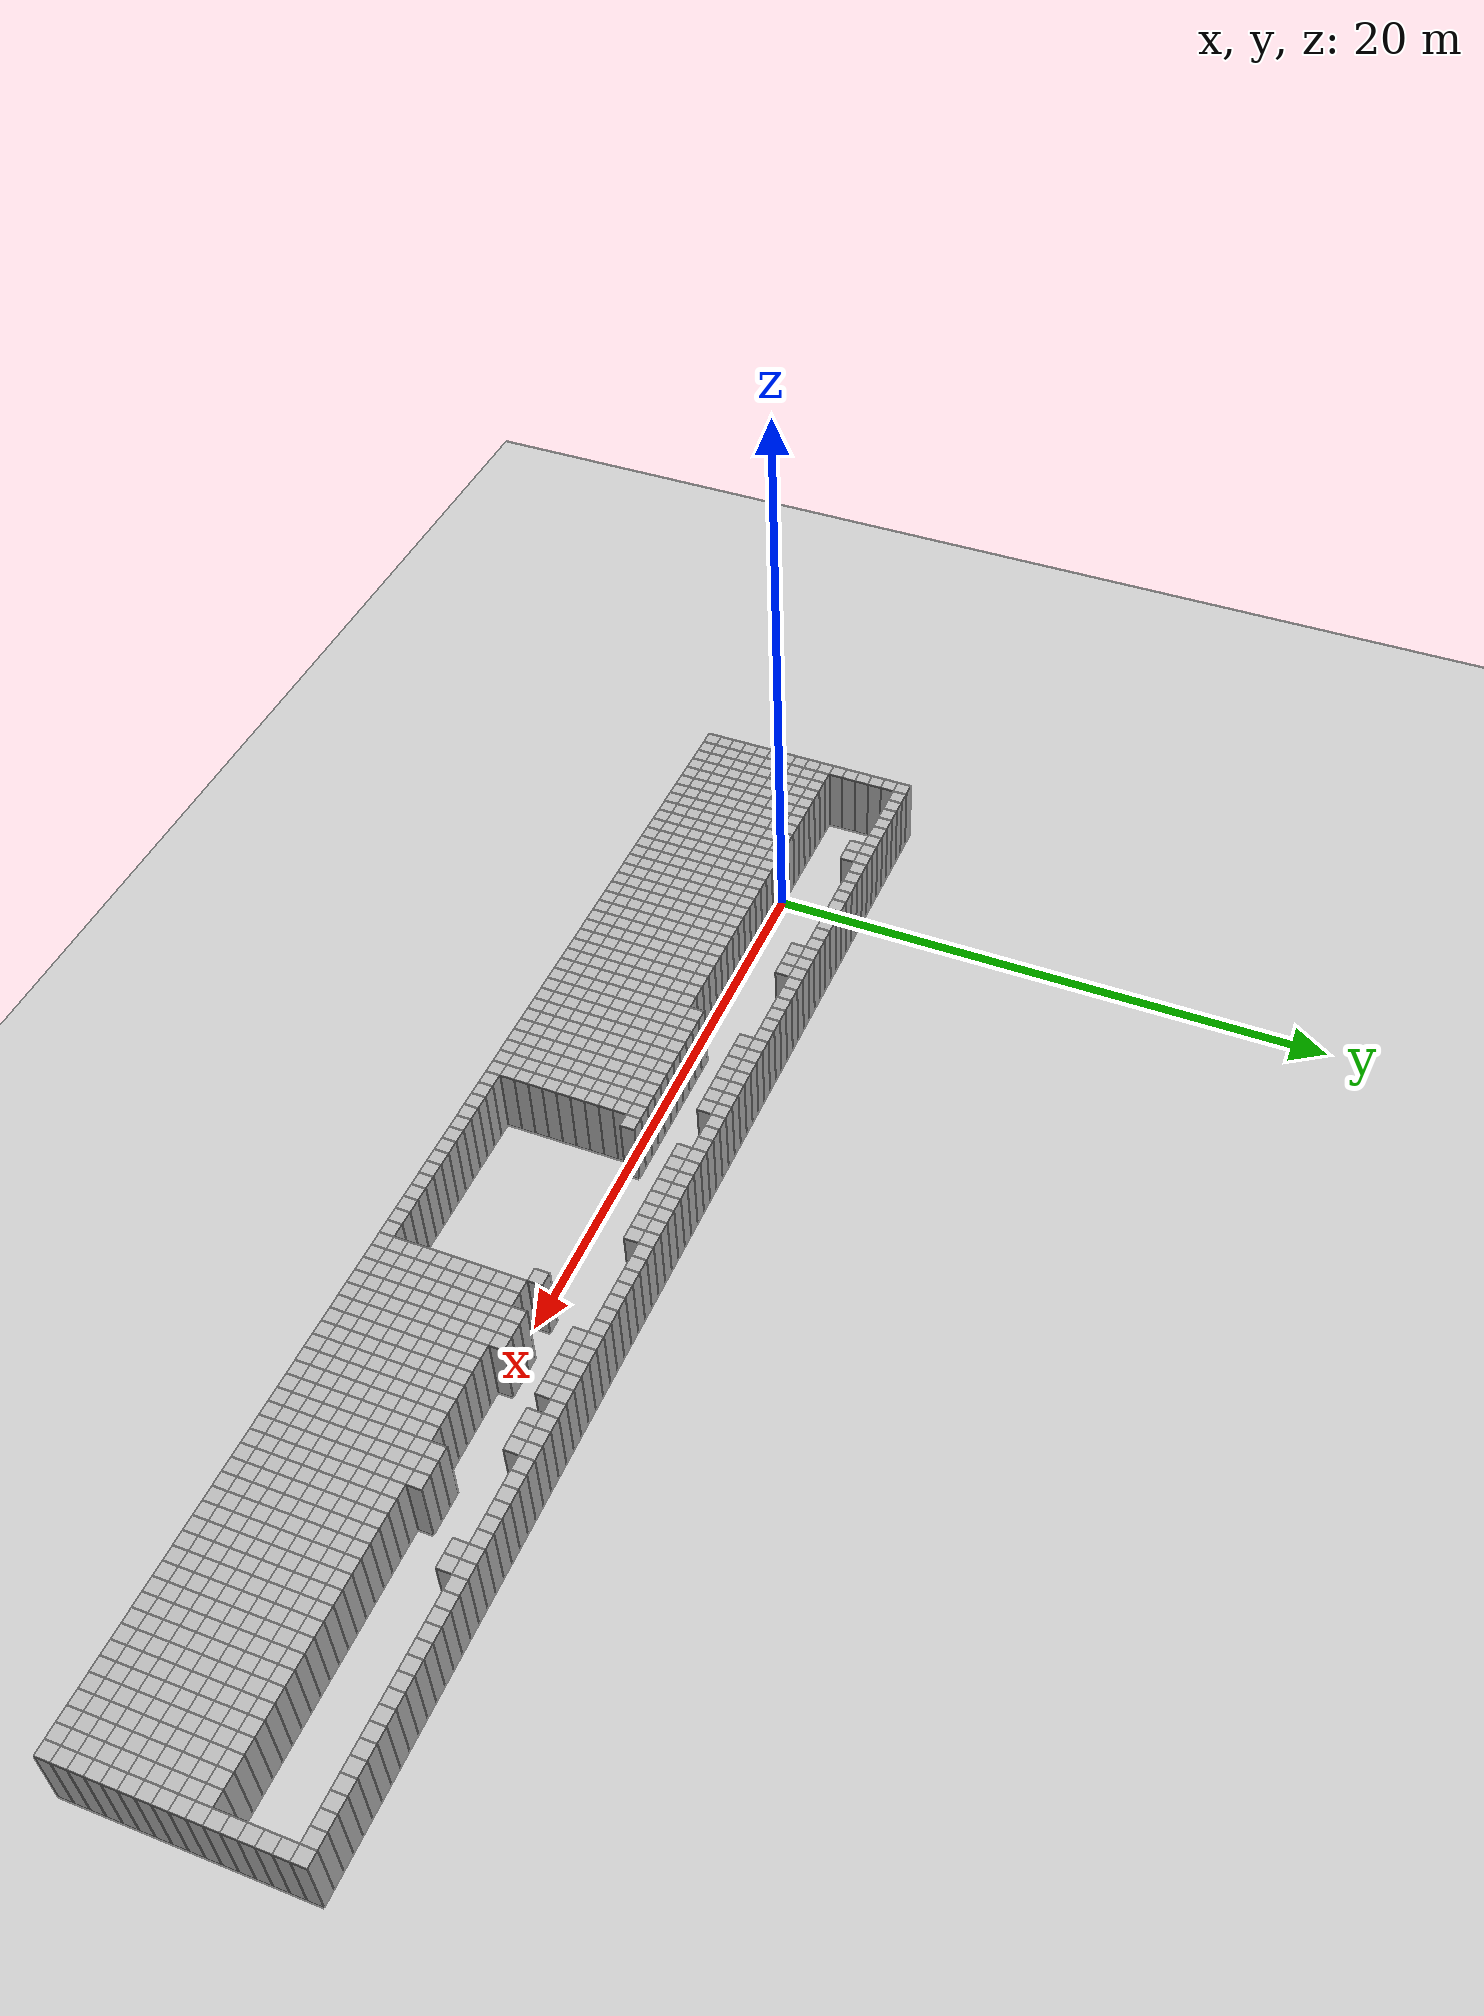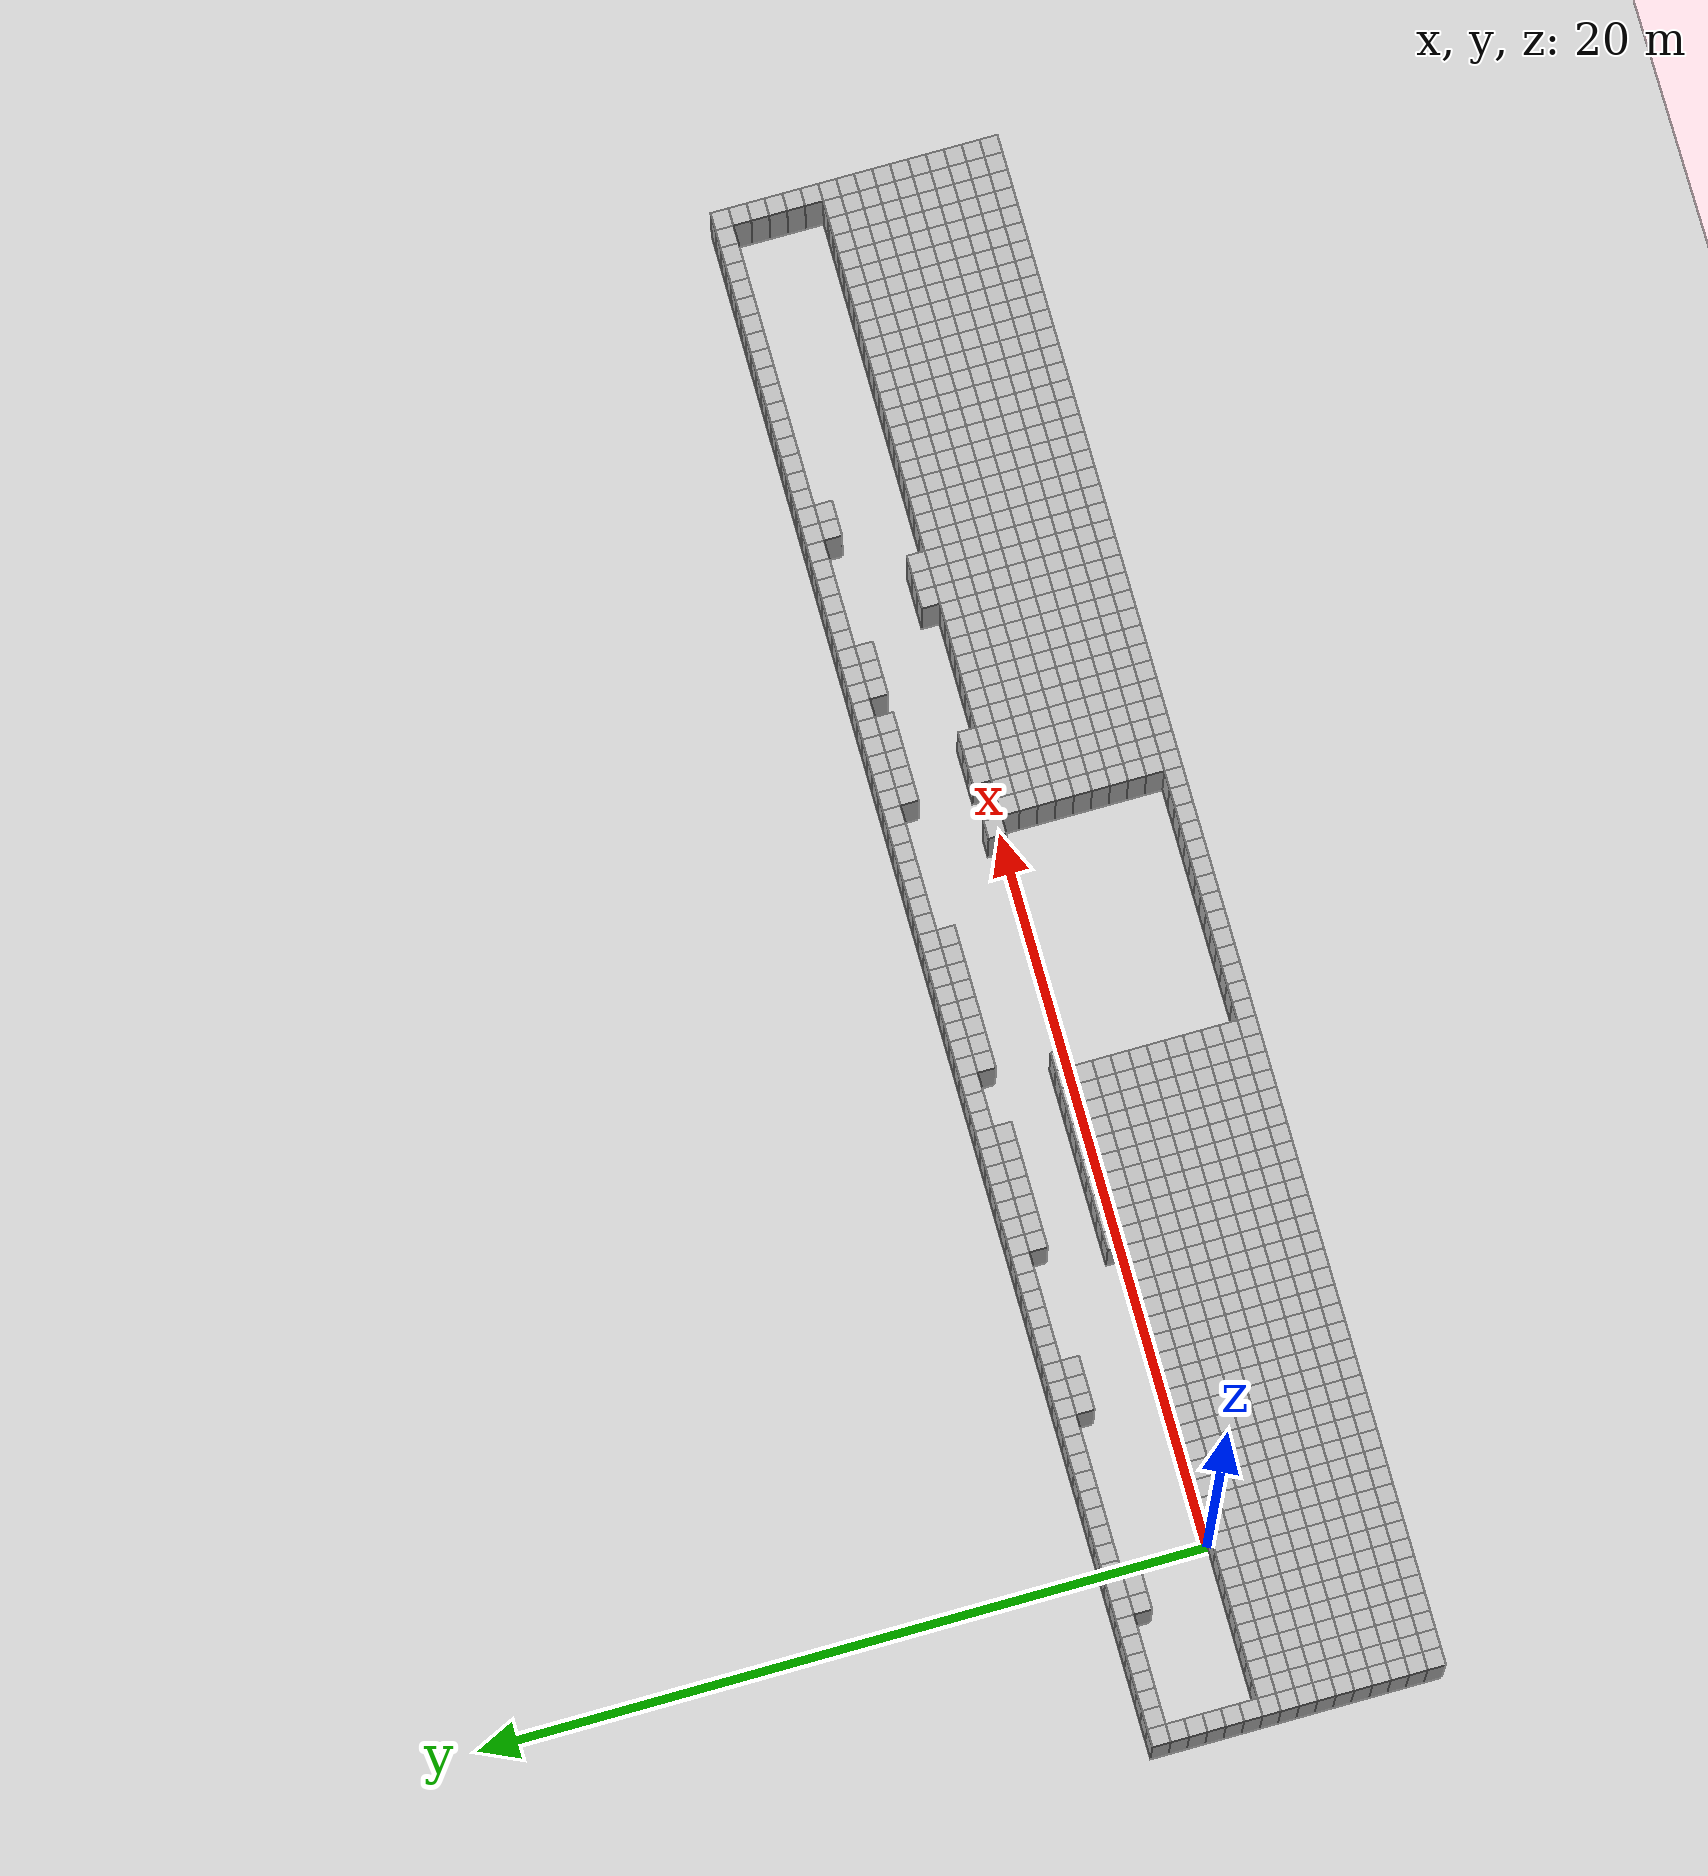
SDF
<?xml version="1.0" ?>
<sdf version="1.6">
  <world name="map_world">
    <include>
      <uri>model://ground_plane</uri>
    </include>
    <include>
      <uri>model://sun</uri>
    </include>

    <model name="wall_0">
      <static>true</static>
      <pose>-4.750 2.750 1.250 0 0 0</pose>
      <link name="link">
        <collision name="collision">
          <geometry>
            <box>
              <size>0.500 0.500 2.500</size>
            </box>
          </geometry>
        </collision>
        <visual name="visual">
          <geometry>
            <box>
              <size>0.500 0.500 2.500</size>
            </box>
          </geometry>
        </visual>
      </link>
    </model>

    <model name="wall_1">
      <static>true</static>
      <pose>-4.250 2.750 1.250 0 0 0</pose>
      <link name="link">
        <collision name="collision">
          <geometry>
            <box>
              <size>0.500 0.500 2.500</size>
            </box>
          </geometry>
        </collision>
        <visual name="visual">
          <geometry>
            <box>
              <size>0.500 0.500 2.500</size>
            </box>
          </geometry>
        </visual>
      </link>
    </model>

    <model name="wall_2">
      <static>true</static>
      <pose>-3.750 2.750 1.250 0 0 0</pose>
      <link name="link">
        <collision name="collision">
          <geometry>
            <box>
              <size>0.500 0.500 2.500</size>
            </box>
          </geometry>
        </collision>
        <visual name="visual">
          <geometry>
            <box>
              <size>0.500 0.500 2.500</size>
            </box>
          </geometry>
        </visual>
      </link>
    </model>

    <model name="wall_3">
      <static>true</static>
      <pose>-3.250 2.750 1.250 0 0 0</pose>
      <link name="link">
        <collision name="collision">
          <geometry>
            <box>
              <size>0.500 0.500 2.500</size>
            </box>
          </geometry>
        </collision>
        <visual name="visual">
          <geometry>
            <box>
              <size>0.500 0.500 2.500</size>
            </box>
          </geometry>
        </visual>
      </link>
    </model>

    <model name="wall_4">
      <static>true</static>
      <pose>-2.750 2.750 1.250 0 0 0</pose>
      <link name="link">
        <collision name="collision">
          <geometry>
            <box>
              <size>0.500 0.500 2.500</size>
            </box>
          </geometry>
        </collision>
        <visual name="visual">
          <geometry>
            <box>
              <size>0.500 0.500 2.500</size>
            </box>
          </geometry>
        </visual>
      </link>
    </model>

    <model name="wall_5">
      <static>true</static>
      <pose>-2.250 2.750 1.250 0 0 0</pose>
      <link name="link">
        <collision name="collision">
          <geometry>
            <box>
              <size>0.500 0.500 2.500</size>
            </box>
          </geometry>
        </collision>
        <visual name="visual">
          <geometry>
            <box>
              <size>0.500 0.500 2.500</size>
            </box>
          </geometry>
        </visual>
      </link>
    </model>

    <model name="wall_6">
      <static>true</static>
      <pose>-1.750 2.750 1.250 0 0 0</pose>
      <link name="link">
        <collision name="collision">
          <geometry>
            <box>
              <size>0.500 0.500 2.500</size>
            </box>
          </geometry>
        </collision>
        <visual name="visual">
          <geometry>
            <box>
              <size>0.500 0.500 2.500</size>
            </box>
          </geometry>
        </visual>
      </link>
    </model>

    <model name="wall_7">
      <static>true</static>
      <pose>-1.250 2.750 1.250 0 0 0</pose>
      <link name="link">
        <collision name="collision">
          <geometry>
            <box>
              <size>0.500 0.500 2.500</size>
            </box>
          </geometry>
        </collision>
        <visual name="visual">
          <geometry>
            <box>
              <size>0.500 0.500 2.500</size>
            </box>
          </geometry>
        </visual>
      </link>
    </model>

    <model name="wall_8">
      <static>true</static>
      <pose>-0.750 2.750 1.250 0 0 0</pose>
      <link name="link">
        <collision name="collision">
          <geometry>
            <box>
              <size>0.500 0.500 2.500</size>
            </box>
          </geometry>
        </collision>
        <visual name="visual">
          <geometry>
            <box>
              <size>0.500 0.500 2.500</size>
            </box>
          </geometry>
        </visual>
      </link>
    </model>

    <model name="wall_9">
      <static>true</static>
      <pose>-0.250 2.750 1.250 0 0 0</pose>
      <link name="link">
        <collision name="collision">
          <geometry>
            <box>
              <size>0.500 0.500 2.500</size>
            </box>
          </geometry>
        </collision>
        <visual name="visual">
          <geometry>
            <box>
              <size>0.500 0.500 2.500</size>
            </box>
          </geometry>
        </visual>
      </link>
    </model>

    <model name="wall_10">
      <static>true</static>
      <pose>0.250 2.750 1.250 0 0 0</pose>
      <link name="link">
        <collision name="collision">
          <geometry>
            <box>
              <size>0.500 0.500 2.500</size>
            </box>
          </geometry>
        </collision>
        <visual name="visual">
          <geometry>
            <box>
              <size>0.500 0.500 2.500</size>
            </box>
          </geometry>
        </visual>
      </link>
    </model>

    <model name="wall_11">
      <static>true</static>
      <pose>0.750 2.750 1.250 0 0 0</pose>
      <link name="link">
        <collision name="collision">
          <geometry>
            <box>
              <size>0.500 0.500 2.500</size>
            </box>
          </geometry>
        </collision>
        <visual name="visual">
          <geometry>
            <box>
              <size>0.500 0.500 2.500</size>
            </box>
          </geometry>
        </visual>
      </link>
    </model>

    <model name="wall_12">
      <static>true</static>
      <pose>1.250 2.750 1.250 0 0 0</pose>
      <link name="link">
        <collision name="collision">
          <geometry>
            <box>
              <size>0.500 0.500 2.500</size>
            </box>
          </geometry>
        </collision>
        <visual name="visual">
          <geometry>
            <box>
              <size>0.500 0.500 2.500</size>
            </box>
          </geometry>
        </visual>
      </link>
    </model>

    <model name="wall_13">
      <static>true</static>
      <pose>1.750 2.750 1.250 0 0 0</pose>
      <link name="link">
        <collision name="collision">
          <geometry>
            <box>
              <size>0.500 0.500 2.500</size>
            </box>
          </geometry>
        </collision>
        <visual name="visual">
          <geometry>
            <box>
              <size>0.500 0.500 2.500</size>
            </box>
          </geometry>
        </visual>
      </link>
    </model>

    <model name="wall_14">
      <static>true</static>
      <pose>2.250 2.750 1.250 0 0 0</pose>
      <link name="link">
        <collision name="collision">
          <geometry>
            <box>
              <size>0.500 0.500 2.500</size>
            </box>
          </geometry>
        </collision>
        <visual name="visual">
          <geometry>
            <box>
              <size>0.500 0.500 2.500</size>
            </box>
          </geometry>
        </visual>
      </link>
    </model>

    <model name="wall_15">
      <static>true</static>
      <pose>2.750 2.750 1.250 0 0 0</pose>
      <link name="link">
        <collision name="collision">
          <geometry>
            <box>
              <size>0.500 0.500 2.500</size>
            </box>
          </geometry>
        </collision>
        <visual name="visual">
          <geometry>
            <box>
              <size>0.500 0.500 2.500</size>
            </box>
          </geometry>
        </visual>
      </link>
    </model>

    <model name="wall_16">
      <static>true</static>
      <pose>3.250 2.750 1.250 0 0 0</pose>
      <link name="link">
        <collision name="collision">
          <geometry>
            <box>
              <size>0.500 0.500 2.500</size>
            </box>
          </geometry>
        </collision>
        <visual name="visual">
          <geometry>
            <box>
              <size>0.500 0.500 2.500</size>
            </box>
          </geometry>
        </visual>
      </link>
    </model>

    <model name="wall_17">
      <static>true</static>
      <pose>3.750 2.750 1.250 0 0 0</pose>
      <link name="link">
        <collision name="collision">
          <geometry>
            <box>
              <size>0.500 0.500 2.500</size>
            </box>
          </geometry>
        </collision>
        <visual name="visual">
          <geometry>
            <box>
              <size>0.500 0.500 2.500</size>
            </box>
          </geometry>
        </visual>
      </link>
    </model>

    <model name="wall_18">
      <static>true</static>
      <pose>4.250 2.750 1.250 0 0 0</pose>
      <link name="link">
        <collision name="collision">
          <geometry>
            <box>
              <size>0.500 0.500 2.500</size>
            </box>
          </geometry>
        </collision>
        <visual name="visual">
          <geometry>
            <box>
              <size>0.500 0.500 2.500</size>
            </box>
          </geometry>
        </visual>
      </link>
    </model>

    <model name="wall_19">
      <static>true</static>
      <pose>4.750 2.750 1.250 0 0 0</pose>
      <link name="link">
        <collision name="collision">
          <geometry>
            <box>
              <size>0.500 0.500 2.500</size>
            </box>
          </geometry>
        </collision>
        <visual name="visual">
          <geometry>
            <box>
              <size>0.500 0.500 2.500</size>
            </box>
          </geometry>
        </visual>
      </link>
    </model>

    <model name="wall_20">
      <static>true</static>
      <pose>5.250 2.750 1.250 0 0 0</pose>
      <link name="link">
        <collision name="collision">
          <geometry>
            <box>
              <size>0.500 0.500 2.500</size>
            </box>
          </geometry>
        </collision>
        <visual name="visual">
          <geometry>
            <box>
              <size>0.500 0.500 2.500</size>
            </box>
          </geometry>
        </visual>
      </link>
    </model>

    <model name="wall_21">
      <static>true</static>
      <pose>5.750 2.750 1.250 0 0 0</pose>
      <link name="link">
        <collision name="collision">
          <geometry>
            <box>
              <size>0.500 0.500 2.500</size>
            </box>
          </geometry>
        </collision>
        <visual name="visual">
          <geometry>
            <box>
              <size>0.500 0.500 2.500</size>
            </box>
          </geometry>
        </visual>
      </link>
    </model>

    <model name="wall_22">
      <static>true</static>
      <pose>6.250 2.750 1.250 0 0 0</pose>
      <link name="link">
        <collision name="collision">
          <geometry>
            <box>
              <size>0.500 0.500 2.500</size>
            </box>
          </geometry>
        </collision>
        <visual name="visual">
          <geometry>
            <box>
              <size>0.500 0.500 2.500</size>
            </box>
          </geometry>
        </visual>
      </link>
    </model>

    <model name="wall_23">
      <static>true</static>
      <pose>6.750 2.750 1.250 0 0 0</pose>
      <link name="link">
        <collision name="collision">
          <geometry>
            <box>
              <size>0.500 0.500 2.500</size>
            </box>
          </geometry>
        </collision>
        <visual name="visual">
          <geometry>
            <box>
              <size>0.500 0.500 2.500</size>
            </box>
          </geometry>
        </visual>
      </link>
    </model>

    <model name="wall_24">
      <static>true</static>
      <pose>7.250 2.750 1.250 0 0 0</pose>
      <link name="link">
        <collision name="collision">
          <geometry>
            <box>
              <size>0.500 0.500 2.500</size>
            </box>
          </geometry>
        </collision>
        <visual name="visual">
          <geometry>
            <box>
              <size>0.500 0.500 2.500</size>
            </box>
          </geometry>
        </visual>
      </link>
    </model>

    <model name="wall_25">
      <static>true</static>
      <pose>7.750 2.750 1.250 0 0 0</pose>
      <link name="link">
        <collision name="collision">
          <geometry>
            <box>
              <size>0.500 0.500 2.500</size>
            </box>
          </geometry>
        </collision>
        <visual name="visual">
          <geometry>
            <box>
              <size>0.500 0.500 2.500</size>
            </box>
          </geometry>
        </visual>
      </link>
    </model>

    <model name="wall_26">
      <static>true</static>
      <pose>8.250 2.750 1.250 0 0 0</pose>
      <link name="link">
        <collision name="collision">
          <geometry>
            <box>
              <size>0.500 0.500 2.500</size>
            </box>
          </geometry>
        </collision>
        <visual name="visual">
          <geometry>
            <box>
              <size>0.500 0.500 2.500</size>
            </box>
          </geometry>
        </visual>
      </link>
    </model>

    <model name="wall_27">
      <static>true</static>
      <pose>8.750 2.750 1.250 0 0 0</pose>
      <link name="link">
        <collision name="collision">
          <geometry>
            <box>
              <size>0.500 0.500 2.500</size>
            </box>
          </geometry>
        </collision>
        <visual name="visual">
          <geometry>
            <box>
              <size>0.500 0.500 2.500</size>
            </box>
          </geometry>
        </visual>
      </link>
    </model>

    <model name="wall_28">
      <static>true</static>
      <pose>9.250 2.750 1.250 0 0 0</pose>
      <link name="link">
        <collision name="collision">
          <geometry>
            <box>
              <size>0.500 0.500 2.500</size>
            </box>
          </geometry>
        </collision>
        <visual name="visual">
          <geometry>
            <box>
              <size>0.500 0.500 2.500</size>
            </box>
          </geometry>
        </visual>
      </link>
    </model>

    <model name="wall_29">
      <static>true</static>
      <pose>9.750 2.750 1.250 0 0 0</pose>
      <link name="link">
        <collision name="collision">
          <geometry>
            <box>
              <size>0.500 0.500 2.500</size>
            </box>
          </geometry>
        </collision>
        <visual name="visual">
          <geometry>
            <box>
              <size>0.500 0.500 2.500</size>
            </box>
          </geometry>
        </visual>
      </link>
    </model>

    <model name="wall_30">
      <static>true</static>
      <pose>10.250 2.750 1.250 0 0 0</pose>
      <link name="link">
        <collision name="collision">
          <geometry>
            <box>
              <size>0.500 0.500 2.500</size>
            </box>
          </geometry>
        </collision>
        <visual name="visual">
          <geometry>
            <box>
              <size>0.500 0.500 2.500</size>
            </box>
          </geometry>
        </visual>
      </link>
    </model>

    <model name="wall_31">
      <static>true</static>
      <pose>10.750 2.750 1.250 0 0 0</pose>
      <link name="link">
        <collision name="collision">
          <geometry>
            <box>
              <size>0.500 0.500 2.500</size>
            </box>
          </geometry>
        </collision>
        <visual name="visual">
          <geometry>
            <box>
              <size>0.500 0.500 2.500</size>
            </box>
          </geometry>
        </visual>
      </link>
    </model>

    <model name="wall_32">
      <static>true</static>
      <pose>11.250 2.750 1.250 0 0 0</pose>
      <link name="link">
        <collision name="collision">
          <geometry>
            <box>
              <size>0.500 0.500 2.500</size>
            </box>
          </geometry>
        </collision>
        <visual name="visual">
          <geometry>
            <box>
              <size>0.500 0.500 2.500</size>
            </box>
          </geometry>
        </visual>
      </link>
    </model>

    <model name="wall_33">
      <static>true</static>
      <pose>11.750 2.750 1.250 0 0 0</pose>
      <link name="link">
        <collision name="collision">
          <geometry>
            <box>
              <size>0.500 0.500 2.500</size>
            </box>
          </geometry>
        </collision>
        <visual name="visual">
          <geometry>
            <box>
              <size>0.500 0.500 2.500</size>
            </box>
          </geometry>
        </visual>
      </link>
    </model>

    <model name="wall_34">
      <static>true</static>
      <pose>12.250 2.750 1.250 0 0 0</pose>
      <link name="link">
        <collision name="collision">
          <geometry>
            <box>
              <size>0.500 0.500 2.500</size>
            </box>
          </geometry>
        </collision>
        <visual name="visual">
          <geometry>
            <box>
              <size>0.500 0.500 2.500</size>
            </box>
          </geometry>
        </visual>
      </link>
    </model>

    <model name="wall_35">
      <static>true</static>
      <pose>12.750 2.750 1.250 0 0 0</pose>
      <link name="link">
        <collision name="collision">
          <geometry>
            <box>
              <size>0.500 0.500 2.500</size>
            </box>
          </geometry>
        </collision>
        <visual name="visual">
          <geometry>
            <box>
              <size>0.500 0.500 2.500</size>
            </box>
          </geometry>
        </visual>
      </link>
    </model>

    <model name="wall_36">
      <static>true</static>
      <pose>13.250 2.750 1.250 0 0 0</pose>
      <link name="link">
        <collision name="collision">
          <geometry>
            <box>
              <size>0.500 0.500 2.500</size>
            </box>
          </geometry>
        </collision>
        <visual name="visual">
          <geometry>
            <box>
              <size>0.500 0.500 2.500</size>
            </box>
          </geometry>
        </visual>
      </link>
    </model>

    <model name="wall_37">
      <static>true</static>
      <pose>13.750 2.750 1.250 0 0 0</pose>
      <link name="link">
        <collision name="collision">
          <geometry>
            <box>
              <size>0.500 0.500 2.500</size>
            </box>
          </geometry>
        </collision>
        <visual name="visual">
          <geometry>
            <box>
              <size>0.500 0.500 2.500</size>
            </box>
          </geometry>
        </visual>
      </link>
    </model>

    <model name="wall_38">
      <static>true</static>
      <pose>14.250 2.750 1.250 0 0 0</pose>
      <link name="link">
        <collision name="collision">
          <geometry>
            <box>
              <size>0.500 0.500 2.500</size>
            </box>
          </geometry>
        </collision>
        <visual name="visual">
          <geometry>
            <box>
              <size>0.500 0.500 2.500</size>
            </box>
          </geometry>
        </visual>
      </link>
    </model>

    <model name="wall_39">
      <static>true</static>
      <pose>14.750 2.750 1.250 0 0 0</pose>
      <link name="link">
        <collision name="collision">
          <geometry>
            <box>
              <size>0.500 0.500 2.500</size>
            </box>
          </geometry>
        </collision>
        <visual name="visual">
          <geometry>
            <box>
              <size>0.500 0.500 2.500</size>
            </box>
          </geometry>
        </visual>
      </link>
    </model>

    <model name="wall_40">
      <static>true</static>
      <pose>15.250 2.750 1.250 0 0 0</pose>
      <link name="link">
        <collision name="collision">
          <geometry>
            <box>
              <size>0.500 0.500 2.500</size>
            </box>
          </geometry>
        </collision>
        <visual name="visual">
          <geometry>
            <box>
              <size>0.500 0.500 2.500</size>
            </box>
          </geometry>
        </visual>
      </link>
    </model>

    <model name="wall_41">
      <static>true</static>
      <pose>15.750 2.750 1.250 0 0 0</pose>
      <link name="link">
        <collision name="collision">
          <geometry>
            <box>
              <size>0.500 0.500 2.500</size>
            </box>
          </geometry>
        </collision>
        <visual name="visual">
          <geometry>
            <box>
              <size>0.500 0.500 2.500</size>
            </box>
          </geometry>
        </visual>
      </link>
    </model>

    <model name="wall_42">
      <static>true</static>
      <pose>16.250 2.750 1.250 0 0 0</pose>
      <link name="link">
        <collision name="collision">
          <geometry>
            <box>
              <size>0.500 0.500 2.500</size>
            </box>
          </geometry>
        </collision>
        <visual name="visual">
          <geometry>
            <box>
              <size>0.500 0.500 2.500</size>
            </box>
          </geometry>
        </visual>
      </link>
    </model>

    <model name="wall_43">
      <static>true</static>
      <pose>16.750 2.750 1.250 0 0 0</pose>
      <link name="link">
        <collision name="collision">
          <geometry>
            <box>
              <size>0.500 0.500 2.500</size>
            </box>
          </geometry>
        </collision>
        <visual name="visual">
          <geometry>
            <box>
              <size>0.500 0.500 2.500</size>
            </box>
          </geometry>
        </visual>
      </link>
    </model>

    <model name="wall_44">
      <static>true</static>
      <pose>17.250 2.750 1.250 0 0 0</pose>
      <link name="link">
        <collision name="collision">
          <geometry>
            <box>
              <size>0.500 0.500 2.500</size>
            </box>
          </geometry>
        </collision>
        <visual name="visual">
          <geometry>
            <box>
              <size>0.500 0.500 2.500</size>
            </box>
          </geometry>
        </visual>
      </link>
    </model>

    <model name="wall_45">
      <static>true</static>
      <pose>17.750 2.750 1.250 0 0 0</pose>
      <link name="link">
        <collision name="collision">
          <geometry>
            <box>
              <size>0.500 0.500 2.500</size>
            </box>
          </geometry>
        </collision>
        <visual name="visual">
          <geometry>
            <box>
              <size>0.500 0.500 2.500</size>
            </box>
          </geometry>
        </visual>
      </link>
    </model>

    <model name="wall_46">
      <static>true</static>
      <pose>18.250 2.750 1.250 0 0 0</pose>
      <link name="link">
        <collision name="collision">
          <geometry>
            <box>
              <size>0.500 0.500 2.500</size>
            </box>
          </geometry>
        </collision>
        <visual name="visual">
          <geometry>
            <box>
              <size>0.500 0.500 2.500</size>
            </box>
          </geometry>
        </visual>
      </link>
    </model>

    <model name="wall_47">
      <static>true</static>
      <pose>18.750 2.750 1.250 0 0 0</pose>
      <link name="link">
        <collision name="collision">
          <geometry>
            <box>
              <size>0.500 0.500 2.500</size>
            </box>
          </geometry>
        </collision>
        <visual name="visual">
          <geometry>
            <box>
              <size>0.500 0.500 2.500</size>
            </box>
          </geometry>
        </visual>
      </link>
    </model>

    <model name="wall_48">
      <static>true</static>
      <pose>19.250 2.750 1.250 0 0 0</pose>
      <link name="link">
        <collision name="collision">
          <geometry>
            <box>
              <size>0.500 0.500 2.500</size>
            </box>
          </geometry>
        </collision>
        <visual name="visual">
          <geometry>
            <box>
              <size>0.500 0.500 2.500</size>
            </box>
          </geometry>
        </visual>
      </link>
    </model>

    <model name="wall_49">
      <static>true</static>
      <pose>19.750 2.750 1.250 0 0 0</pose>
      <link name="link">
        <collision name="collision">
          <geometry>
            <box>
              <size>0.500 0.500 2.500</size>
            </box>
          </geometry>
        </collision>
        <visual name="visual">
          <geometry>
            <box>
              <size>0.500 0.500 2.500</size>
            </box>
          </geometry>
        </visual>
      </link>
    </model>

    <model name="wall_50">
      <static>true</static>
      <pose>20.250 2.750 1.250 0 0 0</pose>
      <link name="link">
        <collision name="collision">
          <geometry>
            <box>
              <size>0.500 0.500 2.500</size>
            </box>
          </geometry>
        </collision>
        <visual name="visual">
          <geometry>
            <box>
              <size>0.500 0.500 2.500</size>
            </box>
          </geometry>
        </visual>
      </link>
    </model>

    <model name="wall_51">
      <static>true</static>
      <pose>20.750 2.750 1.250 0 0 0</pose>
      <link name="link">
        <collision name="collision">
          <geometry>
            <box>
              <size>0.500 0.500 2.500</size>
            </box>
          </geometry>
        </collision>
        <visual name="visual">
          <geometry>
            <box>
              <size>0.500 0.500 2.500</size>
            </box>
          </geometry>
        </visual>
      </link>
    </model>

    <model name="wall_52">
      <static>true</static>
      <pose>21.250 2.750 1.250 0 0 0</pose>
      <link name="link">
        <collision name="collision">
          <geometry>
            <box>
              <size>0.500 0.500 2.500</size>
            </box>
          </geometry>
        </collision>
        <visual name="visual">
          <geometry>
            <box>
              <size>0.500 0.500 2.500</size>
            </box>
          </geometry>
        </visual>
      </link>
    </model>

    <model name="wall_53">
      <static>true</static>
      <pose>21.750 2.750 1.250 0 0 0</pose>
      <link name="link">
        <collision name="collision">
          <geometry>
            <box>
              <size>0.500 0.500 2.500</size>
            </box>
          </geometry>
        </collision>
        <visual name="visual">
          <geometry>
            <box>
              <size>0.500 0.500 2.500</size>
            </box>
          </geometry>
        </visual>
      </link>
    </model>

    <model name="wall_54">
      <static>true</static>
      <pose>22.250 2.750 1.250 0 0 0</pose>
      <link name="link">
        <collision name="collision">
          <geometry>
            <box>
              <size>0.500 0.500 2.500</size>
            </box>
          </geometry>
        </collision>
        <visual name="visual">
          <geometry>
            <box>
              <size>0.500 0.500 2.500</size>
            </box>
          </geometry>
        </visual>
      </link>
    </model>

    <model name="wall_55">
      <static>true</static>
      <pose>22.750 2.750 1.250 0 0 0</pose>
      <link name="link">
        <collision name="collision">
          <geometry>
            <box>
              <size>0.500 0.500 2.500</size>
            </box>
          </geometry>
        </collision>
        <visual name="visual">
          <geometry>
            <box>
              <size>0.500 0.500 2.500</size>
            </box>
          </geometry>
        </visual>
      </link>
    </model>

    <model name="wall_56">
      <static>true</static>
      <pose>23.250 2.750 1.250 0 0 0</pose>
      <link name="link">
        <collision name="collision">
          <geometry>
            <box>
              <size>0.500 0.500 2.500</size>
            </box>
          </geometry>
        </collision>
        <visual name="visual">
          <geometry>
            <box>
              <size>0.500 0.500 2.500</size>
            </box>
          </geometry>
        </visual>
      </link>
    </model>

    <model name="wall_57">
      <static>true</static>
      <pose>23.750 2.750 1.250 0 0 0</pose>
      <link name="link">
        <collision name="collision">
          <geometry>
            <box>
              <size>0.500 0.500 2.500</size>
            </box>
          </geometry>
        </collision>
        <visual name="visual">
          <geometry>
            <box>
              <size>0.500 0.500 2.500</size>
            </box>
          </geometry>
        </visual>
      </link>
    </model>

    <model name="wall_58">
      <static>true</static>
      <pose>24.250 2.750 1.250 0 0 0</pose>
      <link name="link">
        <collision name="collision">
          <geometry>
            <box>
              <size>0.500 0.500 2.500</size>
            </box>
          </geometry>
        </collision>
        <visual name="visual">
          <geometry>
            <box>
              <size>0.500 0.500 2.500</size>
            </box>
          </geometry>
        </visual>
      </link>
    </model>

    <model name="wall_59">
      <static>true</static>
      <pose>24.750 2.750 1.250 0 0 0</pose>
      <link name="link">
        <collision name="collision">
          <geometry>
            <box>
              <size>0.500 0.500 2.500</size>
            </box>
          </geometry>
        </collision>
        <visual name="visual">
          <geometry>
            <box>
              <size>0.500 0.500 2.500</size>
            </box>
          </geometry>
        </visual>
      </link>
    </model>

    <model name="wall_60">
      <static>true</static>
      <pose>25.250 2.750 1.250 0 0 0</pose>
      <link name="link">
        <collision name="collision">
          <geometry>
            <box>
              <size>0.500 0.500 2.500</size>
            </box>
          </geometry>
        </collision>
        <visual name="visual">
          <geometry>
            <box>
              <size>0.500 0.500 2.500</size>
            </box>
          </geometry>
        </visual>
      </link>
    </model>

    <model name="wall_61">
      <static>true</static>
      <pose>25.750 2.750 1.250 0 0 0</pose>
      <link name="link">
        <collision name="collision">
          <geometry>
            <box>
              <size>0.500 0.500 2.500</size>
            </box>
          </geometry>
        </collision>
        <visual name="visual">
          <geometry>
            <box>
              <size>0.500 0.500 2.500</size>
            </box>
          </geometry>
        </visual>
      </link>
    </model>

    <model name="wall_62">
      <static>true</static>
      <pose>26.250 2.750 1.250 0 0 0</pose>
      <link name="link">
        <collision name="collision">
          <geometry>
            <box>
              <size>0.500 0.500 2.500</size>
            </box>
          </geometry>
        </collision>
        <visual name="visual">
          <geometry>
            <box>
              <size>0.500 0.500 2.500</size>
            </box>
          </geometry>
        </visual>
      </link>
    </model>

    <model name="wall_63">
      <static>true</static>
      <pose>26.750 2.750 1.250 0 0 0</pose>
      <link name="link">
        <collision name="collision">
          <geometry>
            <box>
              <size>0.500 0.500 2.500</size>
            </box>
          </geometry>
        </collision>
        <visual name="visual">
          <geometry>
            <box>
              <size>0.500 0.500 2.500</size>
            </box>
          </geometry>
        </visual>
      </link>
    </model>

    <model name="wall_64">
      <static>true</static>
      <pose>27.250 2.750 1.250 0 0 0</pose>
      <link name="link">
        <collision name="collision">
          <geometry>
            <box>
              <size>0.500 0.500 2.500</size>
            </box>
          </geometry>
        </collision>
        <visual name="visual">
          <geometry>
            <box>
              <size>0.500 0.500 2.500</size>
            </box>
          </geometry>
        </visual>
      </link>
    </model>

    <model name="wall_65">
      <static>true</static>
      <pose>27.750 2.750 1.250 0 0 0</pose>
      <link name="link">
        <collision name="collision">
          <geometry>
            <box>
              <size>0.500 0.500 2.500</size>
            </box>
          </geometry>
        </collision>
        <visual name="visual">
          <geometry>
            <box>
              <size>0.500 0.500 2.500</size>
            </box>
          </geometry>
        </visual>
      </link>
    </model>

    <model name="wall_66">
      <static>true</static>
      <pose>28.250 2.750 1.250 0 0 0</pose>
      <link name="link">
        <collision name="collision">
          <geometry>
            <box>
              <size>0.500 0.500 2.500</size>
            </box>
          </geometry>
        </collision>
        <visual name="visual">
          <geometry>
            <box>
              <size>0.500 0.500 2.500</size>
            </box>
          </geometry>
        </visual>
      </link>
    </model>

    <model name="wall_67">
      <static>true</static>
      <pose>28.750 2.750 1.250 0 0 0</pose>
      <link name="link">
        <collision name="collision">
          <geometry>
            <box>
              <size>0.500 0.500 2.500</size>
            </box>
          </geometry>
        </collision>
        <visual name="visual">
          <geometry>
            <box>
              <size>0.500 0.500 2.500</size>
            </box>
          </geometry>
        </visual>
      </link>
    </model>

    <model name="wall_68">
      <static>true</static>
      <pose>29.250 2.750 1.250 0 0 0</pose>
      <link name="link">
        <collision name="collision">
          <geometry>
            <box>
              <size>0.500 0.500 2.500</size>
            </box>
          </geometry>
        </collision>
        <visual name="visual">
          <geometry>
            <box>
              <size>0.500 0.500 2.500</size>
            </box>
          </geometry>
        </visual>
      </link>
    </model>

    <model name="wall_69">
      <static>true</static>
      <pose>29.750 2.750 1.250 0 0 0</pose>
      <link name="link">
        <collision name="collision">
          <geometry>
            <box>
              <size>0.500 0.500 2.500</size>
            </box>
          </geometry>
        </collision>
        <visual name="visual">
          <geometry>
            <box>
              <size>0.500 0.500 2.500</size>
            </box>
          </geometry>
        </visual>
      </link>
    </model>

    <model name="wall_70">
      <static>true</static>
      <pose>30.250 2.750 1.250 0 0 0</pose>
      <link name="link">
        <collision name="collision">
          <geometry>
            <box>
              <size>0.500 0.500 2.500</size>
            </box>
          </geometry>
        </collision>
        <visual name="visual">
          <geometry>
            <box>
              <size>0.500 0.500 2.500</size>
            </box>
          </geometry>
        </visual>
      </link>
    </model>

    <model name="wall_71">
      <static>true</static>
      <pose>30.750 2.750 1.250 0 0 0</pose>
      <link name="link">
        <collision name="collision">
          <geometry>
            <box>
              <size>0.500 0.500 2.500</size>
            </box>
          </geometry>
        </collision>
        <visual name="visual">
          <geometry>
            <box>
              <size>0.500 0.500 2.500</size>
            </box>
          </geometry>
        </visual>
      </link>
    </model>

    <model name="wall_72">
      <static>true</static>
      <pose>31.250 2.750 1.250 0 0 0</pose>
      <link name="link">
        <collision name="collision">
          <geometry>
            <box>
              <size>0.500 0.500 2.500</size>
            </box>
          </geometry>
        </collision>
        <visual name="visual">
          <geometry>
            <box>
              <size>0.500 0.500 2.500</size>
            </box>
          </geometry>
        </visual>
      </link>
    </model>

    <model name="wall_73">
      <static>true</static>
      <pose>31.750 2.750 1.250 0 0 0</pose>
      <link name="link">
        <collision name="collision">
          <geometry>
            <box>
              <size>0.500 0.500 2.500</size>
            </box>
          </geometry>
        </collision>
        <visual name="visual">
          <geometry>
            <box>
              <size>0.500 0.500 2.500</size>
            </box>
          </geometry>
        </visual>
      </link>
    </model>

    <model name="wall_74">
      <static>true</static>
      <pose>32.250 2.750 1.250 0 0 0</pose>
      <link name="link">
        <collision name="collision">
          <geometry>
            <box>
              <size>0.500 0.500 2.500</size>
            </box>
          </geometry>
        </collision>
        <visual name="visual">
          <geometry>
            <box>
              <size>0.500 0.500 2.500</size>
            </box>
          </geometry>
        </visual>
      </link>
    </model>

    <model name="wall_75">
      <static>true</static>
      <pose>32.750 2.750 1.250 0 0 0</pose>
      <link name="link">
        <collision name="collision">
          <geometry>
            <box>
              <size>0.500 0.500 2.500</size>
            </box>
          </geometry>
        </collision>
        <visual name="visual">
          <geometry>
            <box>
              <size>0.500 0.500 2.500</size>
            </box>
          </geometry>
        </visual>
      </link>
    </model>

    <model name="wall_76">
      <static>true</static>
      <pose>33.250 2.750 1.250 0 0 0</pose>
      <link name="link">
        <collision name="collision">
          <geometry>
            <box>
              <size>0.500 0.500 2.500</size>
            </box>
          </geometry>
        </collision>
        <visual name="visual">
          <geometry>
            <box>
              <size>0.500 0.500 2.500</size>
            </box>
          </geometry>
        </visual>
      </link>
    </model>

    <model name="wall_77">
      <static>true</static>
      <pose>33.750 2.750 1.250 0 0 0</pose>
      <link name="link">
        <collision name="collision">
          <geometry>
            <box>
              <size>0.500 0.500 2.500</size>
            </box>
          </geometry>
        </collision>
        <visual name="visual">
          <geometry>
            <box>
              <size>0.500 0.500 2.500</size>
            </box>
          </geometry>
        </visual>
      </link>
    </model>

    <model name="wall_78">
      <static>true</static>
      <pose>34.250 2.750 1.250 0 0 0</pose>
      <link name="link">
        <collision name="collision">
          <geometry>
            <box>
              <size>0.500 0.500 2.500</size>
            </box>
          </geometry>
        </collision>
        <visual name="visual">
          <geometry>
            <box>
              <size>0.500 0.500 2.500</size>
            </box>
          </geometry>
        </visual>
      </link>
    </model>

    <model name="wall_79">
      <static>true</static>
      <pose>34.750 2.750 1.250 0 0 0</pose>
      <link name="link">
        <collision name="collision">
          <geometry>
            <box>
              <size>0.500 0.500 2.500</size>
            </box>
          </geometry>
        </collision>
        <visual name="visual">
          <geometry>
            <box>
              <size>0.500 0.500 2.500</size>
            </box>
          </geometry>
        </visual>
      </link>
    </model>

    <model name="wall_80">
      <static>true</static>
      <pose>35.250 2.750 1.250 0 0 0</pose>
      <link name="link">
        <collision name="collision">
          <geometry>
            <box>
              <size>0.500 0.500 2.500</size>
            </box>
          </geometry>
        </collision>
        <visual name="visual">
          <geometry>
            <box>
              <size>0.500 0.500 2.500</size>
            </box>
          </geometry>
        </visual>
      </link>
    </model>

    <model name="wall_81">
      <static>true</static>
      <pose>35.750 2.750 1.250 0 0 0</pose>
      <link name="link">
        <collision name="collision">
          <geometry>
            <box>
              <size>0.500 0.500 2.500</size>
            </box>
          </geometry>
        </collision>
        <visual name="visual">
          <geometry>
            <box>
              <size>0.500 0.500 2.500</size>
            </box>
          </geometry>
        </visual>
      </link>
    </model>

    <model name="wall_82">
      <static>true</static>
      <pose>36.250 2.750 1.250 0 0 0</pose>
      <link name="link">
        <collision name="collision">
          <geometry>
            <box>
              <size>0.500 0.500 2.500</size>
            </box>
          </geometry>
        </collision>
        <visual name="visual">
          <geometry>
            <box>
              <size>0.500 0.500 2.500</size>
            </box>
          </geometry>
        </visual>
      </link>
    </model>

    <model name="wall_83">
      <static>true</static>
      <pose>36.750 2.750 1.250 0 0 0</pose>
      <link name="link">
        <collision name="collision">
          <geometry>
            <box>
              <size>0.500 0.500 2.500</size>
            </box>
          </geometry>
        </collision>
        <visual name="visual">
          <geometry>
            <box>
              <size>0.500 0.500 2.500</size>
            </box>
          </geometry>
        </visual>
      </link>
    </model>

    <model name="wall_84">
      <static>true</static>
      <pose>37.250 2.750 1.250 0 0 0</pose>
      <link name="link">
        <collision name="collision">
          <geometry>
            <box>
              <size>0.500 0.500 2.500</size>
            </box>
          </geometry>
        </collision>
        <visual name="visual">
          <geometry>
            <box>
              <size>0.500 0.500 2.500</size>
            </box>
          </geometry>
        </visual>
      </link>
    </model>

    <model name="wall_85">
      <static>true</static>
      <pose>37.750 2.750 1.250 0 0 0</pose>
      <link name="link">
        <collision name="collision">
          <geometry>
            <box>
              <size>0.500 0.500 2.500</size>
            </box>
          </geometry>
        </collision>
        <visual name="visual">
          <geometry>
            <box>
              <size>0.500 0.500 2.500</size>
            </box>
          </geometry>
        </visual>
      </link>
    </model>

    <model name="wall_86">
      <static>true</static>
      <pose>-4.750 2.250 1.250 0 0 0</pose>
      <link name="link">
        <collision name="collision">
          <geometry>
            <box>
              <size>0.500 0.500 2.500</size>
            </box>
          </geometry>
        </collision>
        <visual name="visual">
          <geometry>
            <box>
              <size>0.500 0.500 2.500</size>
            </box>
          </geometry>
        </visual>
      </link>
    </model>

    <model name="wall_87">
      <static>true</static>
      <pose>-1.250 2.250 1.250 0 0 0</pose>
      <link name="link">
        <collision name="collision">
          <geometry>
            <box>
              <size>0.500 0.500 2.500</size>
            </box>
          </geometry>
        </collision>
        <visual name="visual">
          <geometry>
            <box>
              <size>0.500 0.500 2.500</size>
            </box>
          </geometry>
        </visual>
      </link>
    </model>

    <model name="wall_88">
      <static>true</static>
      <pose>-0.750 2.250 1.250 0 0 0</pose>
      <link name="link">
        <collision name="collision">
          <geometry>
            <box>
              <size>0.500 0.500 2.500</size>
            </box>
          </geometry>
        </collision>
        <visual name="visual">
          <geometry>
            <box>
              <size>0.500 0.500 2.500</size>
            </box>
          </geometry>
        </visual>
      </link>
    </model>

    <model name="wall_89">
      <static>true</static>
      <pose>4.250 2.250 1.250 0 0 0</pose>
      <link name="link">
        <collision name="collision">
          <geometry>
            <box>
              <size>0.500 0.500 2.500</size>
            </box>
          </geometry>
        </collision>
        <visual name="visual">
          <geometry>
            <box>
              <size>0.500 0.500 2.500</size>
            </box>
          </geometry>
        </visual>
      </link>
    </model>

    <model name="wall_90">
      <static>true</static>
      <pose>4.750 2.250 1.250 0 0 0</pose>
      <link name="link">
        <collision name="collision">
          <geometry>
            <box>
              <size>0.500 0.500 2.500</size>
            </box>
          </geometry>
        </collision>
        <visual name="visual">
          <geometry>
            <box>
              <size>0.500 0.500 2.500</size>
            </box>
          </geometry>
        </visual>
      </link>
    </model>

    <model name="wall_91">
      <static>true</static>
      <pose>5.250 2.250 1.250 0 0 0</pose>
      <link name="link">
        <collision name="collision">
          <geometry>
            <box>
              <size>0.500 0.500 2.500</size>
            </box>
          </geometry>
        </collision>
        <visual name="visual">
          <geometry>
            <box>
              <size>0.500 0.500 2.500</size>
            </box>
          </geometry>
        </visual>
      </link>
    </model>

    <model name="wall_92">
      <static>true</static>
      <pose>8.750 2.250 1.250 0 0 0</pose>
      <link name="link">
        <collision name="collision">
          <geometry>
            <box>
              <size>0.500 0.500 2.500</size>
            </box>
          </geometry>
        </collision>
        <visual name="visual">
          <geometry>
            <box>
              <size>0.500 0.500 2.500</size>
            </box>
          </geometry>
        </visual>
      </link>
    </model>

    <model name="wall_93">
      <static>true</static>
      <pose>9.250 2.250 1.250 0 0 0</pose>
      <link name="link">
        <collision name="collision">
          <geometry>
            <box>
              <size>0.500 0.500 2.500</size>
            </box>
          </geometry>
        </collision>
        <visual name="visual">
          <geometry>
            <box>
              <size>0.500 0.500 2.500</size>
            </box>
          </geometry>
        </visual>
      </link>
    </model>

    <model name="wall_94">
      <static>true</static>
      <pose>9.750 2.250 1.250 0 0 0</pose>
      <link name="link">
        <collision name="collision">
          <geometry>
            <box>
              <size>0.500 0.500 2.500</size>
            </box>
          </geometry>
        </collision>
        <visual name="visual">
          <geometry>
            <box>
              <size>0.500 0.500 2.500</size>
            </box>
          </geometry>
        </visual>
      </link>
    </model>

    <model name="wall_95">
      <static>true</static>
      <pose>10.250 2.250 1.250 0 0 0</pose>
      <link name="link">
        <collision name="collision">
          <geometry>
            <box>
              <size>0.500 0.500 2.500</size>
            </box>
          </geometry>
        </collision>
        <visual name="visual">
          <geometry>
            <box>
              <size>0.500 0.500 2.500</size>
            </box>
          </geometry>
        </visual>
      </link>
    </model>

    <model name="wall_96">
      <static>true</static>
      <pose>10.750 2.250 1.250 0 0 0</pose>
      <link name="link">
        <collision name="collision">
          <geometry>
            <box>
              <size>0.500 0.500 2.500</size>
            </box>
          </geometry>
        </collision>
        <visual name="visual">
          <geometry>
            <box>
              <size>0.500 0.500 2.500</size>
            </box>
          </geometry>
        </visual>
      </link>
    </model>

    <model name="wall_97">
      <static>true</static>
      <pose>11.250 2.250 1.250 0 0 0</pose>
      <link name="link">
        <collision name="collision">
          <geometry>
            <box>
              <size>0.500 0.500 2.500</size>
            </box>
          </geometry>
        </collision>
        <visual name="visual">
          <geometry>
            <box>
              <size>0.500 0.500 2.500</size>
            </box>
          </geometry>
        </visual>
      </link>
    </model>

    <model name="wall_98">
      <static>true</static>
      <pose>11.750 2.250 1.250 0 0 0</pose>
      <link name="link">
        <collision name="collision">
          <geometry>
            <box>
              <size>0.500 0.500 2.500</size>
            </box>
          </geometry>
        </collision>
        <visual name="visual">
          <geometry>
            <box>
              <size>0.500 0.500 2.500</size>
            </box>
          </geometry>
        </visual>
      </link>
    </model>

    <model name="wall_99">
      <static>true</static>
      <pose>13.750 2.250 1.250 0 0 0</pose>
      <link name="link">
        <collision name="collision">
          <geometry>
            <box>
              <size>0.500 0.500 2.500</size>
            </box>
          </geometry>
        </collision>
        <visual name="visual">
          <geometry>
            <box>
              <size>0.500 0.500 2.500</size>
            </box>
          </geometry>
        </visual>
      </link>
    </model>

    <model name="wall_100">
      <static>true</static>
      <pose>14.250 2.250 1.250 0 0 0</pose>
      <link name="link">
        <collision name="collision">
          <geometry>
            <box>
              <size>0.500 0.500 2.500</size>
            </box>
          </geometry>
        </collision>
        <visual name="visual">
          <geometry>
            <box>
              <size>0.500 0.500 2.500</size>
            </box>
          </geometry>
        </visual>
      </link>
    </model>

    <model name="wall_101">
      <static>true</static>
      <pose>14.750 2.250 1.250 0 0 0</pose>
      <link name="link">
        <collision name="collision">
          <geometry>
            <box>
              <size>0.500 0.500 2.500</size>
            </box>
          </geometry>
        </collision>
        <visual name="visual">
          <geometry>
            <box>
              <size>0.500 0.500 2.500</size>
            </box>
          </geometry>
        </visual>
      </link>
    </model>

    <model name="wall_102">
      <static>true</static>
      <pose>15.250 2.250 1.250 0 0 0</pose>
      <link name="link">
        <collision name="collision">
          <geometry>
            <box>
              <size>0.500 0.500 2.500</size>
            </box>
          </geometry>
        </collision>
        <visual name="visual">
          <geometry>
            <box>
              <size>0.500 0.500 2.500</size>
            </box>
          </geometry>
        </visual>
      </link>
    </model>

    <model name="wall_103">
      <static>true</static>
      <pose>15.750 2.250 1.250 0 0 0</pose>
      <link name="link">
        <collision name="collision">
          <geometry>
            <box>
              <size>0.500 0.500 2.500</size>
            </box>
          </geometry>
        </collision>
        <visual name="visual">
          <geometry>
            <box>
              <size>0.500 0.500 2.500</size>
            </box>
          </geometry>
        </visual>
      </link>
    </model>

    <model name="wall_104">
      <static>true</static>
      <pose>16.250 2.250 1.250 0 0 0</pose>
      <link name="link">
        <collision name="collision">
          <geometry>
            <box>
              <size>0.500 0.500 2.500</size>
            </box>
          </geometry>
        </collision>
        <visual name="visual">
          <geometry>
            <box>
              <size>0.500 0.500 2.500</size>
            </box>
          </geometry>
        </visual>
      </link>
    </model>

    <model name="wall_105">
      <static>true</static>
      <pose>16.750 2.250 1.250 0 0 0</pose>
      <link name="link">
        <collision name="collision">
          <geometry>
            <box>
              <size>0.500 0.500 2.500</size>
            </box>
          </geometry>
        </collision>
        <visual name="visual">
          <geometry>
            <box>
              <size>0.500 0.500 2.500</size>
            </box>
          </geometry>
        </visual>
      </link>
    </model>

    <model name="wall_106">
      <static>true</static>
      <pose>17.250 2.250 1.250 0 0 0</pose>
      <link name="link">
        <collision name="collision">
          <geometry>
            <box>
              <size>0.500 0.500 2.500</size>
            </box>
          </geometry>
        </collision>
        <visual name="visual">
          <geometry>
            <box>
              <size>0.500 0.500 2.500</size>
            </box>
          </geometry>
        </visual>
      </link>
    </model>

    <model name="wall_107">
      <static>true</static>
      <pose>21.250 2.250 1.250 0 0 0</pose>
      <link name="link">
        <collision name="collision">
          <geometry>
            <box>
              <size>0.500 0.500 2.500</size>
            </box>
          </geometry>
        </collision>
        <visual name="visual">
          <geometry>
            <box>
              <size>0.500 0.500 2.500</size>
            </box>
          </geometry>
        </visual>
      </link>
    </model>

    <model name="wall_108">
      <static>true</static>
      <pose>21.750 2.250 1.250 0 0 0</pose>
      <link name="link">
        <collision name="collision">
          <geometry>
            <box>
              <size>0.500 0.500 2.500</size>
            </box>
          </geometry>
        </collision>
        <visual name="visual">
          <geometry>
            <box>
              <size>0.500 0.500 2.500</size>
            </box>
          </geometry>
        </visual>
      </link>
    </model>

    <model name="wall_109">
      <static>true</static>
      <pose>22.250 2.250 1.250 0 0 0</pose>
      <link name="link">
        <collision name="collision">
          <geometry>
            <box>
              <size>0.500 0.500 2.500</size>
            </box>
          </geometry>
        </collision>
        <visual name="visual">
          <geometry>
            <box>
              <size>0.500 0.500 2.500</size>
            </box>
          </geometry>
        </visual>
      </link>
    </model>

    <model name="wall_110">
      <static>true</static>
      <pose>22.750 2.250 1.250 0 0 0</pose>
      <link name="link">
        <collision name="collision">
          <geometry>
            <box>
              <size>0.500 0.500 2.500</size>
            </box>
          </geometry>
        </collision>
        <visual name="visual">
          <geometry>
            <box>
              <size>0.500 0.500 2.500</size>
            </box>
          </geometry>
        </visual>
      </link>
    </model>

    <model name="wall_111">
      <static>true</static>
      <pose>23.250 2.250 1.250 0 0 0</pose>
      <link name="link">
        <collision name="collision">
          <geometry>
            <box>
              <size>0.500 0.500 2.500</size>
            </box>
          </geometry>
        </collision>
        <visual name="visual">
          <geometry>
            <box>
              <size>0.500 0.500 2.500</size>
            </box>
          </geometry>
        </visual>
      </link>
    </model>

    <model name="wall_112">
      <static>true</static>
      <pose>24.250 2.250 1.250 0 0 0</pose>
      <link name="link">
        <collision name="collision">
          <geometry>
            <box>
              <size>0.500 0.500 2.500</size>
            </box>
          </geometry>
        </collision>
        <visual name="visual">
          <geometry>
            <box>
              <size>0.500 0.500 2.500</size>
            </box>
          </geometry>
        </visual>
      </link>
    </model>

    <model name="wall_113">
      <static>true</static>
      <pose>24.750 2.250 1.250 0 0 0</pose>
      <link name="link">
        <collision name="collision">
          <geometry>
            <box>
              <size>0.500 0.500 2.500</size>
            </box>
          </geometry>
        </collision>
        <visual name="visual">
          <geometry>
            <box>
              <size>0.500 0.500 2.500</size>
            </box>
          </geometry>
        </visual>
      </link>
    </model>

    <model name="wall_114">
      <static>true</static>
      <pose>25.250 2.250 1.250 0 0 0</pose>
      <link name="link">
        <collision name="collision">
          <geometry>
            <box>
              <size>0.500 0.500 2.500</size>
            </box>
          </geometry>
        </collision>
        <visual name="visual">
          <geometry>
            <box>
              <size>0.500 0.500 2.500</size>
            </box>
          </geometry>
        </visual>
      </link>
    </model>

    <model name="wall_115">
      <static>true</static>
      <pose>28.750 2.250 1.250 0 0 0</pose>
      <link name="link">
        <collision name="collision">
          <geometry>
            <box>
              <size>0.500 0.500 2.500</size>
            </box>
          </geometry>
        </collision>
        <visual name="visual">
          <geometry>
            <box>
              <size>0.500 0.500 2.500</size>
            </box>
          </geometry>
        </visual>
      </link>
    </model>

    <model name="wall_116">
      <static>true</static>
      <pose>29.250 2.250 1.250 0 0 0</pose>
      <link name="link">
        <collision name="collision">
          <geometry>
            <box>
              <size>0.500 0.500 2.500</size>
            </box>
          </geometry>
        </collision>
        <visual name="visual">
          <geometry>
            <box>
              <size>0.500 0.500 2.500</size>
            </box>
          </geometry>
        </visual>
      </link>
    </model>

    <model name="wall_117">
      <static>true</static>
      <pose>37.750 2.250 1.250 0 0 0</pose>
      <link name="link">
        <collision name="collision">
          <geometry>
            <box>
              <size>0.500 0.500 2.500</size>
            </box>
          </geometry>
        </collision>
        <visual name="visual">
          <geometry>
            <box>
              <size>0.500 0.500 2.500</size>
            </box>
          </geometry>
        </visual>
      </link>
    </model>

    <model name="wall_118">
      <static>true</static>
      <pose>-4.750 1.750 1.250 0 0 0</pose>
      <link name="link">
        <collision name="collision">
          <geometry>
            <box>
              <size>0.500 0.500 2.500</size>
            </box>
          </geometry>
        </collision>
        <visual name="visual">
          <geometry>
            <box>
              <size>0.500 0.500 2.500</size>
            </box>
          </geometry>
        </visual>
      </link>
    </model>

    <model name="wall_119">
      <static>true</static>
      <pose>37.750 1.750 1.250 0 0 0</pose>
      <link name="link">
        <collision name="collision">
          <geometry>
            <box>
              <size>0.500 0.500 2.500</size>
            </box>
          </geometry>
        </collision>
        <visual name="visual">
          <geometry>
            <box>
              <size>0.500 0.500 2.500</size>
            </box>
          </geometry>
        </visual>
      </link>
    </model>

    <model name="wall_120">
      <static>true</static>
      <pose>-4.750 1.250 1.250 0 0 0</pose>
      <link name="link">
        <collision name="collision">
          <geometry>
            <box>
              <size>0.500 0.500 2.500</size>
            </box>
          </geometry>
        </collision>
        <visual name="visual">
          <geometry>
            <box>
              <size>0.500 0.500 2.500</size>
            </box>
          </geometry>
        </visual>
      </link>
    </model>

    <model name="wall_121">
      <static>true</static>
      <pose>37.750 1.250 1.250 0 0 0</pose>
      <link name="link">
        <collision name="collision">
          <geometry>
            <box>
              <size>0.500 0.500 2.500</size>
            </box>
          </geometry>
        </collision>
        <visual name="visual">
          <geometry>
            <box>
              <size>0.500 0.500 2.500</size>
            </box>
          </geometry>
        </visual>
      </link>
    </model>

    <model name="wall_122">
      <static>true</static>
      <pose>-4.750 0.750 1.250 0 0 0</pose>
      <link name="link">
        <collision name="collision">
          <geometry>
            <box>
              <size>0.500 0.500 2.500</size>
            </box>
          </geometry>
        </collision>
        <visual name="visual">
          <geometry>
            <box>
              <size>0.500 0.500 2.500</size>
            </box>
          </geometry>
        </visual>
      </link>
    </model>

    <model name="wall_123">
      <static>true</static>
      <pose>37.750 0.750 1.250 0 0 0</pose>
      <link name="link">
        <collision name="collision">
          <geometry>
            <box>
              <size>0.500 0.500 2.500</size>
            </box>
          </geometry>
        </collision>
        <visual name="visual">
          <geometry>
            <box>
              <size>0.500 0.500 2.500</size>
            </box>
          </geometry>
        </visual>
      </link>
    </model>

    <model name="wall_124">
      <static>true</static>
      <pose>-4.750 0.250 1.250 0 0 0</pose>
      <link name="link">
        <collision name="collision">
          <geometry>
            <box>
              <size>0.500 0.500 2.500</size>
            </box>
          </geometry>
        </collision>
        <visual name="visual">
          <geometry>
            <box>
              <size>0.500 0.500 2.500</size>
            </box>
          </geometry>
        </visual>
      </link>
    </model>

    <model name="wall_125">
      <static>true</static>
      <pose>8.250 0.250 1.250 0 0 0</pose>
      <link name="link">
        <collision name="collision">
          <geometry>
            <box>
              <size>0.500 0.500 2.500</size>
            </box>
          </geometry>
        </collision>
        <visual name="visual">
          <geometry>
            <box>
              <size>0.500 0.500 2.500</size>
            </box>
          </geometry>
        </visual>
      </link>
    </model>

    <model name="wall_126">
      <static>true</static>
      <pose>8.750 0.250 1.250 0 0 0</pose>
      <link name="link">
        <collision name="collision">
          <geometry>
            <box>
              <size>0.500 0.500 2.500</size>
            </box>
          </geometry>
        </collision>
        <visual name="visual">
          <geometry>
            <box>
              <size>0.500 0.500 2.500</size>
            </box>
          </geometry>
        </visual>
      </link>
    </model>

    <model name="wall_127">
      <static>true</static>
      <pose>9.250 0.250 1.250 0 0 0</pose>
      <link name="link">
        <collision name="collision">
          <geometry>
            <box>
              <size>0.500 0.500 2.500</size>
            </box>
          </geometry>
        </collision>
        <visual name="visual">
          <geometry>
            <box>
              <size>0.500 0.500 2.500</size>
            </box>
          </geometry>
        </visual>
      </link>
    </model>

    <model name="wall_128">
      <static>true</static>
      <pose>9.750 0.250 1.250 0 0 0</pose>
      <link name="link">
        <collision name="collision">
          <geometry>
            <box>
              <size>0.500 0.500 2.500</size>
            </box>
          </geometry>
        </collision>
        <visual name="visual">
          <geometry>
            <box>
              <size>0.500 0.500 2.500</size>
            </box>
          </geometry>
        </visual>
      </link>
    </model>

    <model name="wall_129">
      <static>true</static>
      <pose>10.250 0.250 1.250 0 0 0</pose>
      <link name="link">
        <collision name="collision">
          <geometry>
            <box>
              <size>0.500 0.500 2.500</size>
            </box>
          </geometry>
        </collision>
        <visual name="visual">
          <geometry>
            <box>
              <size>0.500 0.500 2.500</size>
            </box>
          </geometry>
        </visual>
      </link>
    </model>

    <model name="wall_130">
      <static>true</static>
      <pose>10.750 0.250 1.250 0 0 0</pose>
      <link name="link">
        <collision name="collision">
          <geometry>
            <box>
              <size>0.500 0.500 2.500</size>
            </box>
          </geometry>
        </collision>
        <visual name="visual">
          <geometry>
            <box>
              <size>0.500 0.500 2.500</size>
            </box>
          </geometry>
        </visual>
      </link>
    </model>

    <model name="wall_131">
      <static>true</static>
      <pose>11.250 0.250 1.250 0 0 0</pose>
      <link name="link">
        <collision name="collision">
          <geometry>
            <box>
              <size>0.500 0.500 2.500</size>
            </box>
          </geometry>
        </collision>
        <visual name="visual">
          <geometry>
            <box>
              <size>0.500 0.500 2.500</size>
            </box>
          </geometry>
        </visual>
      </link>
    </model>

    <model name="wall_132">
      <static>true</static>
      <pose>11.750 0.250 1.250 0 0 0</pose>
      <link name="link">
        <collision name="collision">
          <geometry>
            <box>
              <size>0.500 0.500 2.500</size>
            </box>
          </geometry>
        </collision>
        <visual name="visual">
          <geometry>
            <box>
              <size>0.500 0.500 2.500</size>
            </box>
          </geometry>
        </visual>
      </link>
    </model>

    <model name="wall_133">
      <static>true</static>
      <pose>12.250 0.250 1.250 0 0 0</pose>
      <link name="link">
        <collision name="collision">
          <geometry>
            <box>
              <size>0.500 0.500 2.500</size>
            </box>
          </geometry>
        </collision>
        <visual name="visual">
          <geometry>
            <box>
              <size>0.500 0.500 2.500</size>
            </box>
          </geometry>
        </visual>
      </link>
    </model>

    <model name="wall_134">
      <static>true</static>
      <pose>12.750 0.250 1.250 0 0 0</pose>
      <link name="link">
        <collision name="collision">
          <geometry>
            <box>
              <size>0.500 0.500 2.500</size>
            </box>
          </geometry>
        </collision>
        <visual name="visual">
          <geometry>
            <box>
              <size>0.500 0.500 2.500</size>
            </box>
          </geometry>
        </visual>
      </link>
    </model>

    <model name="wall_135">
      <static>true</static>
      <pose>13.250 0.250 1.250 0 0 0</pose>
      <link name="link">
        <collision name="collision">
          <geometry>
            <box>
              <size>0.500 0.500 2.500</size>
            </box>
          </geometry>
        </collision>
        <visual name="visual">
          <geometry>
            <box>
              <size>0.500 0.500 2.500</size>
            </box>
          </geometry>
        </visual>
      </link>
    </model>

    <model name="wall_136">
      <static>true</static>
      <pose>19.750 0.250 1.250 0 0 0</pose>
      <link name="link">
        <collision name="collision">
          <geometry>
            <box>
              <size>0.500 0.500 2.500</size>
            </box>
          </geometry>
        </collision>
        <visual name="visual">
          <geometry>
            <box>
              <size>0.500 0.500 2.500</size>
            </box>
          </geometry>
        </visual>
      </link>
    </model>

    <model name="wall_137">
      <static>true</static>
      <pose>21.250 0.250 1.250 0 0 0</pose>
      <link name="link">
        <collision name="collision">
          <geometry>
            <box>
              <size>0.500 0.500 2.500</size>
            </box>
          </geometry>
        </collision>
        <visual name="visual">
          <geometry>
            <box>
              <size>0.500 0.500 2.500</size>
            </box>
          </geometry>
        </visual>
      </link>
    </model>

    <model name="wall_138">
      <static>true</static>
      <pose>21.750 0.250 1.250 0 0 0</pose>
      <link name="link">
        <collision name="collision">
          <geometry>
            <box>
              <size>0.500 0.500 2.500</size>
            </box>
          </geometry>
        </collision>
        <visual name="visual">
          <geometry>
            <box>
              <size>0.500 0.500 2.500</size>
            </box>
          </geometry>
        </visual>
      </link>
    </model>

    <model name="wall_139">
      <static>true</static>
      <pose>22.250 0.250 1.250 0 0 0</pose>
      <link name="link">
        <collision name="collision">
          <geometry>
            <box>
              <size>0.500 0.500 2.500</size>
            </box>
          </geometry>
        </collision>
        <visual name="visual">
          <geometry>
            <box>
              <size>0.500 0.500 2.500</size>
            </box>
          </geometry>
        </visual>
      </link>
    </model>

    <model name="wall_140">
      <static>true</static>
      <pose>26.250 0.250 1.250 0 0 0</pose>
      <link name="link">
        <collision name="collision">
          <geometry>
            <box>
              <size>0.500 0.500 2.500</size>
            </box>
          </geometry>
        </collision>
        <visual name="visual">
          <geometry>
            <box>
              <size>0.500 0.500 2.500</size>
            </box>
          </geometry>
        </visual>
      </link>
    </model>

    <model name="wall_141">
      <static>true</static>
      <pose>26.750 0.250 1.250 0 0 0</pose>
      <link name="link">
        <collision name="collision">
          <geometry>
            <box>
              <size>0.500 0.500 2.500</size>
            </box>
          </geometry>
        </collision>
        <visual name="visual">
          <geometry>
            <box>
              <size>0.500 0.500 2.500</size>
            </box>
          </geometry>
        </visual>
      </link>
    </model>

    <model name="wall_142">
      <static>true</static>
      <pose>27.250 0.250 1.250 0 0 0</pose>
      <link name="link">
        <collision name="collision">
          <geometry>
            <box>
              <size>0.500 0.500 2.500</size>
            </box>
          </geometry>
        </collision>
        <visual name="visual">
          <geometry>
            <box>
              <size>0.500 0.500 2.500</size>
            </box>
          </geometry>
        </visual>
      </link>
    </model>

    <model name="wall_143">
      <static>true</static>
      <pose>37.750 0.250 1.250 0 0 0</pose>
      <link name="link">
        <collision name="collision">
          <geometry>
            <box>
              <size>0.500 0.500 2.500</size>
            </box>
          </geometry>
        </collision>
        <visual name="visual">
          <geometry>
            <box>
              <size>0.500 0.500 2.500</size>
            </box>
          </geometry>
        </visual>
      </link>
    </model>

    <model name="wall_144">
      <static>true</static>
      <pose>-4.750 -0.250 1.250 0 0 0</pose>
      <link name="link">
        <collision name="collision">
          <geometry>
            <box>
              <size>0.500 0.500 2.500</size>
            </box>
          </geometry>
        </collision>
        <visual name="visual">
          <geometry>
            <box>
              <size>0.500 0.500 2.500</size>
            </box>
          </geometry>
        </visual>
      </link>
    </model>

    <model name="wall_145">
      <static>true</static>
      <pose>-4.250 -0.250 1.250 0 0 0</pose>
      <link name="link">
        <collision name="collision">
          <geometry>
            <box>
              <size>0.500 0.500 2.500</size>
            </box>
          </geometry>
        </collision>
        <visual name="visual">
          <geometry>
            <box>
              <size>0.500 0.500 2.500</size>
            </box>
          </geometry>
        </visual>
      </link>
    </model>

    <model name="wall_146">
      <static>true</static>
      <pose>-3.750 -0.250 1.250 0 0 0</pose>
      <link name="link">
        <collision name="collision">
          <geometry>
            <box>
              <size>0.500 0.500 2.500</size>
            </box>
          </geometry>
        </collision>
        <visual name="visual">
          <geometry>
            <box>
              <size>0.500 0.500 2.500</size>
            </box>
          </geometry>
        </visual>
      </link>
    </model>

    <model name="wall_147">
      <static>true</static>
      <pose>-3.250 -0.250 1.250 0 0 0</pose>
      <link name="link">
        <collision name="collision">
          <geometry>
            <box>
              <size>0.500 0.500 2.500</size>
            </box>
          </geometry>
        </collision>
        <visual name="visual">
          <geometry>
            <box>
              <size>0.500 0.500 2.500</size>
            </box>
          </geometry>
        </visual>
      </link>
    </model>

    <model name="wall_148">
      <static>true</static>
      <pose>-2.750 -0.250 1.250 0 0 0</pose>
      <link name="link">
        <collision name="collision">
          <geometry>
            <box>
              <size>0.500 0.500 2.500</size>
            </box>
          </geometry>
        </collision>
        <visual name="visual">
          <geometry>
            <box>
              <size>0.500 0.500 2.500</size>
            </box>
          </geometry>
        </visual>
      </link>
    </model>

    <model name="wall_149">
      <static>true</static>
      <pose>-2.250 -0.250 1.250 0 0 0</pose>
      <link name="link">
        <collision name="collision">
          <geometry>
            <box>
              <size>0.500 0.500 2.500</size>
            </box>
          </geometry>
        </collision>
        <visual name="visual">
          <geometry>
            <box>
              <size>0.500 0.500 2.500</size>
            </box>
          </geometry>
        </visual>
      </link>
    </model>

    <model name="wall_150">
      <static>true</static>
      <pose>-1.750 -0.250 1.250 0 0 0</pose>
      <link name="link">
        <collision name="collision">
          <geometry>
            <box>
              <size>0.500 0.500 2.500</size>
            </box>
          </geometry>
        </collision>
        <visual name="visual">
          <geometry>
            <box>
              <size>0.500 0.500 2.500</size>
            </box>
          </geometry>
        </visual>
      </link>
    </model>

    <model name="wall_151">
      <static>true</static>
      <pose>-1.250 -0.250 1.250 0 0 0</pose>
      <link name="link">
        <collision name="collision">
          <geometry>
            <box>
              <size>0.500 0.500 2.500</size>
            </box>
          </geometry>
        </collision>
        <visual name="visual">
          <geometry>
            <box>
              <size>0.500 0.500 2.500</size>
            </box>
          </geometry>
        </visual>
      </link>
    </model>

    <model name="wall_152">
      <static>true</static>
      <pose>-0.750 -0.250 1.250 0 0 0</pose>
      <link name="link">
        <collision name="collision">
          <geometry>
            <box>
              <size>0.500 0.500 2.500</size>
            </box>
          </geometry>
        </collision>
        <visual name="visual">
          <geometry>
            <box>
              <size>0.500 0.500 2.500</size>
            </box>
          </geometry>
        </visual>
      </link>
    </model>

    <model name="wall_153">
      <static>true</static>
      <pose>-0.250 -0.250 1.250 0 0 0</pose>
      <link name="link">
        <collision name="collision">
          <geometry>
            <box>
              <size>0.500 0.500 2.500</size>
            </box>
          </geometry>
        </collision>
        <visual name="visual">
          <geometry>
            <box>
              <size>0.500 0.500 2.500</size>
            </box>
          </geometry>
        </visual>
      </link>
    </model>

    <model name="wall_154">
      <static>true</static>
      <pose>0.250 -0.250 1.250 0 0 0</pose>
      <link name="link">
        <collision name="collision">
          <geometry>
            <box>
              <size>0.500 0.500 2.500</size>
            </box>
          </geometry>
        </collision>
        <visual name="visual">
          <geometry>
            <box>
              <size>0.500 0.500 2.500</size>
            </box>
          </geometry>
        </visual>
      </link>
    </model>

    <model name="wall_155">
      <static>true</static>
      <pose>0.750 -0.250 1.250 0 0 0</pose>
      <link name="link">
        <collision name="collision">
          <geometry>
            <box>
              <size>0.500 0.500 2.500</size>
            </box>
          </geometry>
        </collision>
        <visual name="visual">
          <geometry>
            <box>
              <size>0.500 0.500 2.500</size>
            </box>
          </geometry>
        </visual>
      </link>
    </model>

    <model name="wall_156">
      <static>true</static>
      <pose>1.250 -0.250 1.250 0 0 0</pose>
      <link name="link">
        <collision name="collision">
          <geometry>
            <box>
              <size>0.500 0.500 2.500</size>
            </box>
          </geometry>
        </collision>
        <visual name="visual">
          <geometry>
            <box>
              <size>0.500 0.500 2.500</size>
            </box>
          </geometry>
        </visual>
      </link>
    </model>

    <model name="wall_157">
      <static>true</static>
      <pose>1.750 -0.250 1.250 0 0 0</pose>
      <link name="link">
        <collision name="collision">
          <geometry>
            <box>
              <size>0.500 0.500 2.500</size>
            </box>
          </geometry>
        </collision>
        <visual name="visual">
          <geometry>
            <box>
              <size>0.500 0.500 2.500</size>
            </box>
          </geometry>
        </visual>
      </link>
    </model>

    <model name="wall_158">
      <static>true</static>
      <pose>2.250 -0.250 1.250 0 0 0</pose>
      <link name="link">
        <collision name="collision">
          <geometry>
            <box>
              <size>0.500 0.500 2.500</size>
            </box>
          </geometry>
        </collision>
        <visual name="visual">
          <geometry>
            <box>
              <size>0.500 0.500 2.500</size>
            </box>
          </geometry>
        </visual>
      </link>
    </model>

    <model name="wall_159">
      <static>true</static>
      <pose>2.750 -0.250 1.250 0 0 0</pose>
      <link name="link">
        <collision name="collision">
          <geometry>
            <box>
              <size>0.500 0.500 2.500</size>
            </box>
          </geometry>
        </collision>
        <visual name="visual">
          <geometry>
            <box>
              <size>0.500 0.500 2.500</size>
            </box>
          </geometry>
        </visual>
      </link>
    </model>

    <model name="wall_160">
      <static>true</static>
      <pose>3.250 -0.250 1.250 0 0 0</pose>
      <link name="link">
        <collision name="collision">
          <geometry>
            <box>
              <size>0.500 0.500 2.500</size>
            </box>
          </geometry>
        </collision>
        <visual name="visual">
          <geometry>
            <box>
              <size>0.500 0.500 2.500</size>
            </box>
          </geometry>
        </visual>
      </link>
    </model>

    <model name="wall_161">
      <static>true</static>
      <pose>3.750 -0.250 1.250 0 0 0</pose>
      <link name="link">
        <collision name="collision">
          <geometry>
            <box>
              <size>0.500 0.500 2.500</size>
            </box>
          </geometry>
        </collision>
        <visual name="visual">
          <geometry>
            <box>
              <size>0.500 0.500 2.500</size>
            </box>
          </geometry>
        </visual>
      </link>
    </model>

    <model name="wall_162">
      <static>true</static>
      <pose>4.250 -0.250 1.250 0 0 0</pose>
      <link name="link">
        <collision name="collision">
          <geometry>
            <box>
              <size>0.500 0.500 2.500</size>
            </box>
          </geometry>
        </collision>
        <visual name="visual">
          <geometry>
            <box>
              <size>0.500 0.500 2.500</size>
            </box>
          </geometry>
        </visual>
      </link>
    </model>

    <model name="wall_163">
      <static>true</static>
      <pose>4.750 -0.250 1.250 0 0 0</pose>
      <link name="link">
        <collision name="collision">
          <geometry>
            <box>
              <size>0.500 0.500 2.500</size>
            </box>
          </geometry>
        </collision>
        <visual name="visual">
          <geometry>
            <box>
              <size>0.500 0.500 2.500</size>
            </box>
          </geometry>
        </visual>
      </link>
    </model>

    <model name="wall_164">
      <static>true</static>
      <pose>5.250 -0.250 1.250 0 0 0</pose>
      <link name="link">
        <collision name="collision">
          <geometry>
            <box>
              <size>0.500 0.500 2.500</size>
            </box>
          </geometry>
        </collision>
        <visual name="visual">
          <geometry>
            <box>
              <size>0.500 0.500 2.500</size>
            </box>
          </geometry>
        </visual>
      </link>
    </model>

    <model name="wall_165">
      <static>true</static>
      <pose>5.750 -0.250 1.250 0 0 0</pose>
      <link name="link">
        <collision name="collision">
          <geometry>
            <box>
              <size>0.500 0.500 2.500</size>
            </box>
          </geometry>
        </collision>
        <visual name="visual">
          <geometry>
            <box>
              <size>0.500 0.500 2.500</size>
            </box>
          </geometry>
        </visual>
      </link>
    </model>

    <model name="wall_166">
      <static>true</static>
      <pose>6.250 -0.250 1.250 0 0 0</pose>
      <link name="link">
        <collision name="collision">
          <geometry>
            <box>
              <size>0.500 0.500 2.500</size>
            </box>
          </geometry>
        </collision>
        <visual name="visual">
          <geometry>
            <box>
              <size>0.500 0.500 2.500</size>
            </box>
          </geometry>
        </visual>
      </link>
    </model>

    <model name="wall_167">
      <static>true</static>
      <pose>6.750 -0.250 1.250 0 0 0</pose>
      <link name="link">
        <collision name="collision">
          <geometry>
            <box>
              <size>0.500 0.500 2.500</size>
            </box>
          </geometry>
        </collision>
        <visual name="visual">
          <geometry>
            <box>
              <size>0.500 0.500 2.500</size>
            </box>
          </geometry>
        </visual>
      </link>
    </model>

    <model name="wall_168">
      <static>true</static>
      <pose>7.250 -0.250 1.250 0 0 0</pose>
      <link name="link">
        <collision name="collision">
          <geometry>
            <box>
              <size>0.500 0.500 2.500</size>
            </box>
          </geometry>
        </collision>
        <visual name="visual">
          <geometry>
            <box>
              <size>0.500 0.500 2.500</size>
            </box>
          </geometry>
        </visual>
      </link>
    </model>

    <model name="wall_169">
      <static>true</static>
      <pose>7.750 -0.250 1.250 0 0 0</pose>
      <link name="link">
        <collision name="collision">
          <geometry>
            <box>
              <size>0.500 0.500 2.500</size>
            </box>
          </geometry>
        </collision>
        <visual name="visual">
          <geometry>
            <box>
              <size>0.500 0.500 2.500</size>
            </box>
          </geometry>
        </visual>
      </link>
    </model>

    <model name="wall_170">
      <static>true</static>
      <pose>8.250 -0.250 1.250 0 0 0</pose>
      <link name="link">
        <collision name="collision">
          <geometry>
            <box>
              <size>0.500 0.500 2.500</size>
            </box>
          </geometry>
        </collision>
        <visual name="visual">
          <geometry>
            <box>
              <size>0.500 0.500 2.500</size>
            </box>
          </geometry>
        </visual>
      </link>
    </model>

    <model name="wall_171">
      <static>true</static>
      <pose>8.750 -0.250 1.250 0 0 0</pose>
      <link name="link">
        <collision name="collision">
          <geometry>
            <box>
              <size>0.500 0.500 2.500</size>
            </box>
          </geometry>
        </collision>
        <visual name="visual">
          <geometry>
            <box>
              <size>0.500 0.500 2.500</size>
            </box>
          </geometry>
        </visual>
      </link>
    </model>

    <model name="wall_172">
      <static>true</static>
      <pose>9.250 -0.250 1.250 0 0 0</pose>
      <link name="link">
        <collision name="collision">
          <geometry>
            <box>
              <size>0.500 0.500 2.500</size>
            </box>
          </geometry>
        </collision>
        <visual name="visual">
          <geometry>
            <box>
              <size>0.500 0.500 2.500</size>
            </box>
          </geometry>
        </visual>
      </link>
    </model>

    <model name="wall_173">
      <static>true</static>
      <pose>9.750 -0.250 1.250 0 0 0</pose>
      <link name="link">
        <collision name="collision">
          <geometry>
            <box>
              <size>0.500 0.500 2.500</size>
            </box>
          </geometry>
        </collision>
        <visual name="visual">
          <geometry>
            <box>
              <size>0.500 0.500 2.500</size>
            </box>
          </geometry>
        </visual>
      </link>
    </model>

    <model name="wall_174">
      <static>true</static>
      <pose>10.250 -0.250 1.250 0 0 0</pose>
      <link name="link">
        <collision name="collision">
          <geometry>
            <box>
              <size>0.500 0.500 2.500</size>
            </box>
          </geometry>
        </collision>
        <visual name="visual">
          <geometry>
            <box>
              <size>0.500 0.500 2.500</size>
            </box>
          </geometry>
        </visual>
      </link>
    </model>

    <model name="wall_175">
      <static>true</static>
      <pose>10.750 -0.250 1.250 0 0 0</pose>
      <link name="link">
        <collision name="collision">
          <geometry>
            <box>
              <size>0.500 0.500 2.500</size>
            </box>
          </geometry>
        </collision>
        <visual name="visual">
          <geometry>
            <box>
              <size>0.500 0.500 2.500</size>
            </box>
          </geometry>
        </visual>
      </link>
    </model>

    <model name="wall_176">
      <static>true</static>
      <pose>11.250 -0.250 1.250 0 0 0</pose>
      <link name="link">
        <collision name="collision">
          <geometry>
            <box>
              <size>0.500 0.500 2.500</size>
            </box>
          </geometry>
        </collision>
        <visual name="visual">
          <geometry>
            <box>
              <size>0.500 0.500 2.500</size>
            </box>
          </geometry>
        </visual>
      </link>
    </model>

    <model name="wall_177">
      <static>true</static>
      <pose>11.750 -0.250 1.250 0 0 0</pose>
      <link name="link">
        <collision name="collision">
          <geometry>
            <box>
              <size>0.500 0.500 2.500</size>
            </box>
          </geometry>
        </collision>
        <visual name="visual">
          <geometry>
            <box>
              <size>0.500 0.500 2.500</size>
            </box>
          </geometry>
        </visual>
      </link>
    </model>

    <model name="wall_178">
      <static>true</static>
      <pose>12.250 -0.250 1.250 0 0 0</pose>
      <link name="link">
        <collision name="collision">
          <geometry>
            <box>
              <size>0.500 0.500 2.500</size>
            </box>
          </geometry>
        </collision>
        <visual name="visual">
          <geometry>
            <box>
              <size>0.500 0.500 2.500</size>
            </box>
          </geometry>
        </visual>
      </link>
    </model>

    <model name="wall_179">
      <static>true</static>
      <pose>12.750 -0.250 1.250 0 0 0</pose>
      <link name="link">
        <collision name="collision">
          <geometry>
            <box>
              <size>0.500 0.500 2.500</size>
            </box>
          </geometry>
        </collision>
        <visual name="visual">
          <geometry>
            <box>
              <size>0.500 0.500 2.500</size>
            </box>
          </geometry>
        </visual>
      </link>
    </model>

    <model name="wall_180">
      <static>true</static>
      <pose>20.250 -0.250 1.250 0 0 0</pose>
      <link name="link">
        <collision name="collision">
          <geometry>
            <box>
              <size>0.500 0.500 2.500</size>
            </box>
          </geometry>
        </collision>
        <visual name="visual">
          <geometry>
            <box>
              <size>0.500 0.500 2.500</size>
            </box>
          </geometry>
        </visual>
      </link>
    </model>

    <model name="wall_181">
      <static>true</static>
      <pose>20.750 -0.250 1.250 0 0 0</pose>
      <link name="link">
        <collision name="collision">
          <geometry>
            <box>
              <size>0.500 0.500 2.500</size>
            </box>
          </geometry>
        </collision>
        <visual name="visual">
          <geometry>
            <box>
              <size>0.500 0.500 2.500</size>
            </box>
          </geometry>
        </visual>
      </link>
    </model>

    <model name="wall_182">
      <static>true</static>
      <pose>21.250 -0.250 1.250 0 0 0</pose>
      <link name="link">
        <collision name="collision">
          <geometry>
            <box>
              <size>0.500 0.500 2.500</size>
            </box>
          </geometry>
        </collision>
        <visual name="visual">
          <geometry>
            <box>
              <size>0.500 0.500 2.500</size>
            </box>
          </geometry>
        </visual>
      </link>
    </model>

    <model name="wall_183">
      <static>true</static>
      <pose>21.750 -0.250 1.250 0 0 0</pose>
      <link name="link">
        <collision name="collision">
          <geometry>
            <box>
              <size>0.500 0.500 2.500</size>
            </box>
          </geometry>
        </collision>
        <visual name="visual">
          <geometry>
            <box>
              <size>0.500 0.500 2.500</size>
            </box>
          </geometry>
        </visual>
      </link>
    </model>

    <model name="wall_184">
      <static>true</static>
      <pose>22.250 -0.250 1.250 0 0 0</pose>
      <link name="link">
        <collision name="collision">
          <geometry>
            <box>
              <size>0.500 0.500 2.500</size>
            </box>
          </geometry>
        </collision>
        <visual name="visual">
          <geometry>
            <box>
              <size>0.500 0.500 2.500</size>
            </box>
          </geometry>
        </visual>
      </link>
    </model>

    <model name="wall_185">
      <static>true</static>
      <pose>22.750 -0.250 1.250 0 0 0</pose>
      <link name="link">
        <collision name="collision">
          <geometry>
            <box>
              <size>0.500 0.500 2.500</size>
            </box>
          </geometry>
        </collision>
        <visual name="visual">
          <geometry>
            <box>
              <size>0.500 0.500 2.500</size>
            </box>
          </geometry>
        </visual>
      </link>
    </model>

    <model name="wall_186">
      <static>true</static>
      <pose>23.250 -0.250 1.250 0 0 0</pose>
      <link name="link">
        <collision name="collision">
          <geometry>
            <box>
              <size>0.500 0.500 2.500</size>
            </box>
          </geometry>
        </collision>
        <visual name="visual">
          <geometry>
            <box>
              <size>0.500 0.500 2.500</size>
            </box>
          </geometry>
        </visual>
      </link>
    </model>

    <model name="wall_187">
      <static>true</static>
      <pose>23.750 -0.250 1.250 0 0 0</pose>
      <link name="link">
        <collision name="collision">
          <geometry>
            <box>
              <size>0.500 0.500 2.500</size>
            </box>
          </geometry>
        </collision>
        <visual name="visual">
          <geometry>
            <box>
              <size>0.500 0.500 2.500</size>
            </box>
          </geometry>
        </visual>
      </link>
    </model>

    <model name="wall_188">
      <static>true</static>
      <pose>24.250 -0.250 1.250 0 0 0</pose>
      <link name="link">
        <collision name="collision">
          <geometry>
            <box>
              <size>0.500 0.500 2.500</size>
            </box>
          </geometry>
        </collision>
        <visual name="visual">
          <geometry>
            <box>
              <size>0.500 0.500 2.500</size>
            </box>
          </geometry>
        </visual>
      </link>
    </model>

    <model name="wall_189">
      <static>true</static>
      <pose>24.750 -0.250 1.250 0 0 0</pose>
      <link name="link">
        <collision name="collision">
          <geometry>
            <box>
              <size>0.500 0.500 2.500</size>
            </box>
          </geometry>
        </collision>
        <visual name="visual">
          <geometry>
            <box>
              <size>0.500 0.500 2.500</size>
            </box>
          </geometry>
        </visual>
      </link>
    </model>

    <model name="wall_190">
      <static>true</static>
      <pose>25.250 -0.250 1.250 0 0 0</pose>
      <link name="link">
        <collision name="collision">
          <geometry>
            <box>
              <size>0.500 0.500 2.500</size>
            </box>
          </geometry>
        </collision>
        <visual name="visual">
          <geometry>
            <box>
              <size>0.500 0.500 2.500</size>
            </box>
          </geometry>
        </visual>
      </link>
    </model>

    <model name="wall_191">
      <static>true</static>
      <pose>25.750 -0.250 1.250 0 0 0</pose>
      <link name="link">
        <collision name="collision">
          <geometry>
            <box>
              <size>0.500 0.500 2.500</size>
            </box>
          </geometry>
        </collision>
        <visual name="visual">
          <geometry>
            <box>
              <size>0.500 0.500 2.500</size>
            </box>
          </geometry>
        </visual>
      </link>
    </model>

    <model name="wall_192">
      <static>true</static>
      <pose>26.250 -0.250 1.250 0 0 0</pose>
      <link name="link">
        <collision name="collision">
          <geometry>
            <box>
              <size>0.500 0.500 2.500</size>
            </box>
          </geometry>
        </collision>
        <visual name="visual">
          <geometry>
            <box>
              <size>0.500 0.500 2.500</size>
            </box>
          </geometry>
        </visual>
      </link>
    </model>

    <model name="wall_193">
      <static>true</static>
      <pose>26.750 -0.250 1.250 0 0 0</pose>
      <link name="link">
        <collision name="collision">
          <geometry>
            <box>
              <size>0.500 0.500 2.500</size>
            </box>
          </geometry>
        </collision>
        <visual name="visual">
          <geometry>
            <box>
              <size>0.500 0.500 2.500</size>
            </box>
          </geometry>
        </visual>
      </link>
    </model>

    <model name="wall_194">
      <static>true</static>
      <pose>27.250 -0.250 1.250 0 0 0</pose>
      <link name="link">
        <collision name="collision">
          <geometry>
            <box>
              <size>0.500 0.500 2.500</size>
            </box>
          </geometry>
        </collision>
        <visual name="visual">
          <geometry>
            <box>
              <size>0.500 0.500 2.500</size>
            </box>
          </geometry>
        </visual>
      </link>
    </model>

    <model name="wall_195">
      <static>true</static>
      <pose>27.750 -0.250 1.250 0 0 0</pose>
      <link name="link">
        <collision name="collision">
          <geometry>
            <box>
              <size>0.500 0.500 2.500</size>
            </box>
          </geometry>
        </collision>
        <visual name="visual">
          <geometry>
            <box>
              <size>0.500 0.500 2.500</size>
            </box>
          </geometry>
        </visual>
      </link>
    </model>

    <model name="wall_196">
      <static>true</static>
      <pose>28.250 -0.250 1.250 0 0 0</pose>
      <link name="link">
        <collision name="collision">
          <geometry>
            <box>
              <size>0.500 0.500 2.500</size>
            </box>
          </geometry>
        </collision>
        <visual name="visual">
          <geometry>
            <box>
              <size>0.500 0.500 2.500</size>
            </box>
          </geometry>
        </visual>
      </link>
    </model>

    <model name="wall_197">
      <static>true</static>
      <pose>28.750 -0.250 1.250 0 0 0</pose>
      <link name="link">
        <collision name="collision">
          <geometry>
            <box>
              <size>0.500 0.500 2.500</size>
            </box>
          </geometry>
        </collision>
        <visual name="visual">
          <geometry>
            <box>
              <size>0.500 0.500 2.500</size>
            </box>
          </geometry>
        </visual>
      </link>
    </model>

    <model name="wall_198">
      <static>true</static>
      <pose>29.250 -0.250 1.250 0 0 0</pose>
      <link name="link">
        <collision name="collision">
          <geometry>
            <box>
              <size>0.500 0.500 2.500</size>
            </box>
          </geometry>
        </collision>
        <visual name="visual">
          <geometry>
            <box>
              <size>0.500 0.500 2.500</size>
            </box>
          </geometry>
        </visual>
      </link>
    </model>

    <model name="wall_199">
      <static>true</static>
      <pose>29.750 -0.250 1.250 0 0 0</pose>
      <link name="link">
        <collision name="collision">
          <geometry>
            <box>
              <size>0.500 0.500 2.500</size>
            </box>
          </geometry>
        </collision>
        <visual name="visual">
          <geometry>
            <box>
              <size>0.500 0.500 2.500</size>
            </box>
          </geometry>
        </visual>
      </link>
    </model>

    <model name="wall_200">
      <static>true</static>
      <pose>30.250 -0.250 1.250 0 0 0</pose>
      <link name="link">
        <collision name="collision">
          <geometry>
            <box>
              <size>0.500 0.500 2.500</size>
            </box>
          </geometry>
        </collision>
        <visual name="visual">
          <geometry>
            <box>
              <size>0.500 0.500 2.500</size>
            </box>
          </geometry>
        </visual>
      </link>
    </model>

    <model name="wall_201">
      <static>true</static>
      <pose>30.750 -0.250 1.250 0 0 0</pose>
      <link name="link">
        <collision name="collision">
          <geometry>
            <box>
              <size>0.500 0.500 2.500</size>
            </box>
          </geometry>
        </collision>
        <visual name="visual">
          <geometry>
            <box>
              <size>0.500 0.500 2.500</size>
            </box>
          </geometry>
        </visual>
      </link>
    </model>

    <model name="wall_202">
      <static>true</static>
      <pose>31.250 -0.250 1.250 0 0 0</pose>
      <link name="link">
        <collision name="collision">
          <geometry>
            <box>
              <size>0.500 0.500 2.500</size>
            </box>
          </geometry>
        </collision>
        <visual name="visual">
          <geometry>
            <box>
              <size>0.500 0.500 2.500</size>
            </box>
          </geometry>
        </visual>
      </link>
    </model>

    <model name="wall_203">
      <static>true</static>
      <pose>31.750 -0.250 1.250 0 0 0</pose>
      <link name="link">
        <collision name="collision">
          <geometry>
            <box>
              <size>0.500 0.500 2.500</size>
            </box>
          </geometry>
        </collision>
        <visual name="visual">
          <geometry>
            <box>
              <size>0.500 0.500 2.500</size>
            </box>
          </geometry>
        </visual>
      </link>
    </model>

    <model name="wall_204">
      <static>true</static>
      <pose>32.250 -0.250 1.250 0 0 0</pose>
      <link name="link">
        <collision name="collision">
          <geometry>
            <box>
              <size>0.500 0.500 2.500</size>
            </box>
          </geometry>
        </collision>
        <visual name="visual">
          <geometry>
            <box>
              <size>0.500 0.500 2.500</size>
            </box>
          </geometry>
        </visual>
      </link>
    </model>

    <model name="wall_205">
      <static>true</static>
      <pose>32.750 -0.250 1.250 0 0 0</pose>
      <link name="link">
        <collision name="collision">
          <geometry>
            <box>
              <size>0.500 0.500 2.500</size>
            </box>
          </geometry>
        </collision>
        <visual name="visual">
          <geometry>
            <box>
              <size>0.500 0.500 2.500</size>
            </box>
          </geometry>
        </visual>
      </link>
    </model>

    <model name="wall_206">
      <static>true</static>
      <pose>33.250 -0.250 1.250 0 0 0</pose>
      <link name="link">
        <collision name="collision">
          <geometry>
            <box>
              <size>0.500 0.500 2.500</size>
            </box>
          </geometry>
        </collision>
        <visual name="visual">
          <geometry>
            <box>
              <size>0.500 0.500 2.500</size>
            </box>
          </geometry>
        </visual>
      </link>
    </model>

    <model name="wall_207">
      <static>true</static>
      <pose>33.750 -0.250 1.250 0 0 0</pose>
      <link name="link">
        <collision name="collision">
          <geometry>
            <box>
              <size>0.500 0.500 2.500</size>
            </box>
          </geometry>
        </collision>
        <visual name="visual">
          <geometry>
            <box>
              <size>0.500 0.500 2.500</size>
            </box>
          </geometry>
        </visual>
      </link>
    </model>

    <model name="wall_208">
      <static>true</static>
      <pose>34.250 -0.250 1.250 0 0 0</pose>
      <link name="link">
        <collision name="collision">
          <geometry>
            <box>
              <size>0.500 0.500 2.500</size>
            </box>
          </geometry>
        </collision>
        <visual name="visual">
          <geometry>
            <box>
              <size>0.500 0.500 2.500</size>
            </box>
          </geometry>
        </visual>
      </link>
    </model>

    <model name="wall_209">
      <static>true</static>
      <pose>34.750 -0.250 1.250 0 0 0</pose>
      <link name="link">
        <collision name="collision">
          <geometry>
            <box>
              <size>0.500 0.500 2.500</size>
            </box>
          </geometry>
        </collision>
        <visual name="visual">
          <geometry>
            <box>
              <size>0.500 0.500 2.500</size>
            </box>
          </geometry>
        </visual>
      </link>
    </model>

    <model name="wall_210">
      <static>true</static>
      <pose>35.250 -0.250 1.250 0 0 0</pose>
      <link name="link">
        <collision name="collision">
          <geometry>
            <box>
              <size>0.500 0.500 2.500</size>
            </box>
          </geometry>
        </collision>
        <visual name="visual">
          <geometry>
            <box>
              <size>0.500 0.500 2.500</size>
            </box>
          </geometry>
        </visual>
      </link>
    </model>

    <model name="wall_211">
      <static>true</static>
      <pose>35.750 -0.250 1.250 0 0 0</pose>
      <link name="link">
        <collision name="collision">
          <geometry>
            <box>
              <size>0.500 0.500 2.500</size>
            </box>
          </geometry>
        </collision>
        <visual name="visual">
          <geometry>
            <box>
              <size>0.500 0.500 2.500</size>
            </box>
          </geometry>
        </visual>
      </link>
    </model>

    <model name="wall_212">
      <static>true</static>
      <pose>36.250 -0.250 1.250 0 0 0</pose>
      <link name="link">
        <collision name="collision">
          <geometry>
            <box>
              <size>0.500 0.500 2.500</size>
            </box>
          </geometry>
        </collision>
        <visual name="visual">
          <geometry>
            <box>
              <size>0.500 0.500 2.500</size>
            </box>
          </geometry>
        </visual>
      </link>
    </model>

    <model name="wall_213">
      <static>true</static>
      <pose>36.750 -0.250 1.250 0 0 0</pose>
      <link name="link">
        <collision name="collision">
          <geometry>
            <box>
              <size>0.500 0.500 2.500</size>
            </box>
          </geometry>
        </collision>
        <visual name="visual">
          <geometry>
            <box>
              <size>0.500 0.500 2.500</size>
            </box>
          </geometry>
        </visual>
      </link>
    </model>

    <model name="wall_214">
      <static>true</static>
      <pose>37.250 -0.250 1.250 0 0 0</pose>
      <link name="link">
        <collision name="collision">
          <geometry>
            <box>
              <size>0.500 0.500 2.500</size>
            </box>
          </geometry>
        </collision>
        <visual name="visual">
          <geometry>
            <box>
              <size>0.500 0.500 2.500</size>
            </box>
          </geometry>
        </visual>
      </link>
    </model>

    <model name="wall_215">
      <static>true</static>
      <pose>37.750 -0.250 1.250 0 0 0</pose>
      <link name="link">
        <collision name="collision">
          <geometry>
            <box>
              <size>0.500 0.500 2.500</size>
            </box>
          </geometry>
        </collision>
        <visual name="visual">
          <geometry>
            <box>
              <size>0.500 0.500 2.500</size>
            </box>
          </geometry>
        </visual>
      </link>
    </model>

    <model name="wall_216">
      <static>true</static>
      <pose>-4.750 -0.750 1.250 0 0 0</pose>
      <link name="link">
        <collision name="collision">
          <geometry>
            <box>
              <size>0.500 0.500 2.500</size>
            </box>
          </geometry>
        </collision>
        <visual name="visual">
          <geometry>
            <box>
              <size>0.500 0.500 2.500</size>
            </box>
          </geometry>
        </visual>
      </link>
    </model>

    <model name="wall_217">
      <static>true</static>
      <pose>-4.250 -0.750 1.250 0 0 0</pose>
      <link name="link">
        <collision name="collision">
          <geometry>
            <box>
              <size>0.500 0.500 2.500</size>
            </box>
          </geometry>
        </collision>
        <visual name="visual">
          <geometry>
            <box>
              <size>0.500 0.500 2.500</size>
            </box>
          </geometry>
        </visual>
      </link>
    </model>

    <model name="wall_218">
      <static>true</static>
      <pose>-3.750 -0.750 1.250 0 0 0</pose>
      <link name="link">
        <collision name="collision">
          <geometry>
            <box>
              <size>0.500 0.500 2.500</size>
            </box>
          </geometry>
        </collision>
        <visual name="visual">
          <geometry>
            <box>
              <size>0.500 0.500 2.500</size>
            </box>
          </geometry>
        </visual>
      </link>
    </model>

    <model name="wall_219">
      <static>true</static>
      <pose>-3.250 -0.750 1.250 0 0 0</pose>
      <link name="link">
        <collision name="collision">
          <geometry>
            <box>
              <size>0.500 0.500 2.500</size>
            </box>
          </geometry>
        </collision>
        <visual name="visual">
          <geometry>
            <box>
              <size>0.500 0.500 2.500</size>
            </box>
          </geometry>
        </visual>
      </link>
    </model>

    <model name="wall_220">
      <static>true</static>
      <pose>-2.750 -0.750 1.250 0 0 0</pose>
      <link name="link">
        <collision name="collision">
          <geometry>
            <box>
              <size>0.500 0.500 2.500</size>
            </box>
          </geometry>
        </collision>
        <visual name="visual">
          <geometry>
            <box>
              <size>0.500 0.500 2.500</size>
            </box>
          </geometry>
        </visual>
      </link>
    </model>

    <model name="wall_221">
      <static>true</static>
      <pose>-2.250 -0.750 1.250 0 0 0</pose>
      <link name="link">
        <collision name="collision">
          <geometry>
            <box>
              <size>0.500 0.500 2.500</size>
            </box>
          </geometry>
        </collision>
        <visual name="visual">
          <geometry>
            <box>
              <size>0.500 0.500 2.500</size>
            </box>
          </geometry>
        </visual>
      </link>
    </model>

    <model name="wall_222">
      <static>true</static>
      <pose>-1.750 -0.750 1.250 0 0 0</pose>
      <link name="link">
        <collision name="collision">
          <geometry>
            <box>
              <size>0.500 0.500 2.500</size>
            </box>
          </geometry>
        </collision>
        <visual name="visual">
          <geometry>
            <box>
              <size>0.500 0.500 2.500</size>
            </box>
          </geometry>
        </visual>
      </link>
    </model>

    <model name="wall_223">
      <static>true</static>
      <pose>-1.250 -0.750 1.250 0 0 0</pose>
      <link name="link">
        <collision name="collision">
          <geometry>
            <box>
              <size>0.500 0.500 2.500</size>
            </box>
          </geometry>
        </collision>
        <visual name="visual">
          <geometry>
            <box>
              <size>0.500 0.500 2.500</size>
            </box>
          </geometry>
        </visual>
      </link>
    </model>

    <model name="wall_224">
      <static>true</static>
      <pose>-0.750 -0.750 1.250 0 0 0</pose>
      <link name="link">
        <collision name="collision">
          <geometry>
            <box>
              <size>0.500 0.500 2.500</size>
            </box>
          </geometry>
        </collision>
        <visual name="visual">
          <geometry>
            <box>
              <size>0.500 0.500 2.500</size>
            </box>
          </geometry>
        </visual>
      </link>
    </model>

    <model name="wall_225">
      <static>true</static>
      <pose>-0.250 -0.750 1.250 0 0 0</pose>
      <link name="link">
        <collision name="collision">
          <geometry>
            <box>
              <size>0.500 0.500 2.500</size>
            </box>
          </geometry>
        </collision>
        <visual name="visual">
          <geometry>
            <box>
              <size>0.500 0.500 2.500</size>
            </box>
          </geometry>
        </visual>
      </link>
    </model>

    <model name="wall_226">
      <static>true</static>
      <pose>0.250 -0.750 1.250 0 0 0</pose>
      <link name="link">
        <collision name="collision">
          <geometry>
            <box>
              <size>0.500 0.500 2.500</size>
            </box>
          </geometry>
        </collision>
        <visual name="visual">
          <geometry>
            <box>
              <size>0.500 0.500 2.500</size>
            </box>
          </geometry>
        </visual>
      </link>
    </model>

    <model name="wall_227">
      <static>true</static>
      <pose>0.750 -0.750 1.250 0 0 0</pose>
      <link name="link">
        <collision name="collision">
          <geometry>
            <box>
              <size>0.500 0.500 2.500</size>
            </box>
          </geometry>
        </collision>
        <visual name="visual">
          <geometry>
            <box>
              <size>0.500 0.500 2.500</size>
            </box>
          </geometry>
        </visual>
      </link>
    </model>

    <model name="wall_228">
      <static>true</static>
      <pose>1.250 -0.750 1.250 0 0 0</pose>
      <link name="link">
        <collision name="collision">
          <geometry>
            <box>
              <size>0.500 0.500 2.500</size>
            </box>
          </geometry>
        </collision>
        <visual name="visual">
          <geometry>
            <box>
              <size>0.500 0.500 2.500</size>
            </box>
          </geometry>
        </visual>
      </link>
    </model>

    <model name="wall_229">
      <static>true</static>
      <pose>1.750 -0.750 1.250 0 0 0</pose>
      <link name="link">
        <collision name="collision">
          <geometry>
            <box>
              <size>0.500 0.500 2.500</size>
            </box>
          </geometry>
        </collision>
        <visual name="visual">
          <geometry>
            <box>
              <size>0.500 0.500 2.500</size>
            </box>
          </geometry>
        </visual>
      </link>
    </model>

    <model name="wall_230">
      <static>true</static>
      <pose>2.250 -0.750 1.250 0 0 0</pose>
      <link name="link">
        <collision name="collision">
          <geometry>
            <box>
              <size>0.500 0.500 2.500</size>
            </box>
          </geometry>
        </collision>
        <visual name="visual">
          <geometry>
            <box>
              <size>0.500 0.500 2.500</size>
            </box>
          </geometry>
        </visual>
      </link>
    </model>

    <model name="wall_231">
      <static>true</static>
      <pose>2.750 -0.750 1.250 0 0 0</pose>
      <link name="link">
        <collision name="collision">
          <geometry>
            <box>
              <size>0.500 0.500 2.500</size>
            </box>
          </geometry>
        </collision>
        <visual name="visual">
          <geometry>
            <box>
              <size>0.500 0.500 2.500</size>
            </box>
          </geometry>
        </visual>
      </link>
    </model>

    <model name="wall_232">
      <static>true</static>
      <pose>3.250 -0.750 1.250 0 0 0</pose>
      <link name="link">
        <collision name="collision">
          <geometry>
            <box>
              <size>0.500 0.500 2.500</size>
            </box>
          </geometry>
        </collision>
        <visual name="visual">
          <geometry>
            <box>
              <size>0.500 0.500 2.500</size>
            </box>
          </geometry>
        </visual>
      </link>
    </model>

    <model name="wall_233">
      <static>true</static>
      <pose>3.750 -0.750 1.250 0 0 0</pose>
      <link name="link">
        <collision name="collision">
          <geometry>
            <box>
              <size>0.500 0.500 2.500</size>
            </box>
          </geometry>
        </collision>
        <visual name="visual">
          <geometry>
            <box>
              <size>0.500 0.500 2.500</size>
            </box>
          </geometry>
        </visual>
      </link>
    </model>

    <model name="wall_234">
      <static>true</static>
      <pose>4.250 -0.750 1.250 0 0 0</pose>
      <link name="link">
        <collision name="collision">
          <geometry>
            <box>
              <size>0.500 0.500 2.500</size>
            </box>
          </geometry>
        </collision>
        <visual name="visual">
          <geometry>
            <box>
              <size>0.500 0.500 2.500</size>
            </box>
          </geometry>
        </visual>
      </link>
    </model>

    <model name="wall_235">
      <static>true</static>
      <pose>4.750 -0.750 1.250 0 0 0</pose>
      <link name="link">
        <collision name="collision">
          <geometry>
            <box>
              <size>0.500 0.500 2.500</size>
            </box>
          </geometry>
        </collision>
        <visual name="visual">
          <geometry>
            <box>
              <size>0.500 0.500 2.500</size>
            </box>
          </geometry>
        </visual>
      </link>
    </model>

    <model name="wall_236">
      <static>true</static>
      <pose>5.250 -0.750 1.250 0 0 0</pose>
      <link name="link">
        <collision name="collision">
          <geometry>
            <box>
              <size>0.500 0.500 2.500</size>
            </box>
          </geometry>
        </collision>
        <visual name="visual">
          <geometry>
            <box>
              <size>0.500 0.500 2.500</size>
            </box>
          </geometry>
        </visual>
      </link>
    </model>

    <model name="wall_237">
      <static>true</static>
      <pose>5.750 -0.750 1.250 0 0 0</pose>
      <link name="link">
        <collision name="collision">
          <geometry>
            <box>
              <size>0.500 0.500 2.500</size>
            </box>
          </geometry>
        </collision>
        <visual name="visual">
          <geometry>
            <box>
              <size>0.500 0.500 2.500</size>
            </box>
          </geometry>
        </visual>
      </link>
    </model>

    <model name="wall_238">
      <static>true</static>
      <pose>6.250 -0.750 1.250 0 0 0</pose>
      <link name="link">
        <collision name="collision">
          <geometry>
            <box>
              <size>0.500 0.500 2.500</size>
            </box>
          </geometry>
        </collision>
        <visual name="visual">
          <geometry>
            <box>
              <size>0.500 0.500 2.500</size>
            </box>
          </geometry>
        </visual>
      </link>
    </model>

    <model name="wall_239">
      <static>true</static>
      <pose>6.750 -0.750 1.250 0 0 0</pose>
      <link name="link">
        <collision name="collision">
          <geometry>
            <box>
              <size>0.500 0.500 2.500</size>
            </box>
          </geometry>
        </collision>
        <visual name="visual">
          <geometry>
            <box>
              <size>0.500 0.500 2.500</size>
            </box>
          </geometry>
        </visual>
      </link>
    </model>

    <model name="wall_240">
      <static>true</static>
      <pose>7.250 -0.750 1.250 0 0 0</pose>
      <link name="link">
        <collision name="collision">
          <geometry>
            <box>
              <size>0.500 0.500 2.500</size>
            </box>
          </geometry>
        </collision>
        <visual name="visual">
          <geometry>
            <box>
              <size>0.500 0.500 2.500</size>
            </box>
          </geometry>
        </visual>
      </link>
    </model>

    <model name="wall_241">
      <static>true</static>
      <pose>7.750 -0.750 1.250 0 0 0</pose>
      <link name="link">
        <collision name="collision">
          <geometry>
            <box>
              <size>0.500 0.500 2.500</size>
            </box>
          </geometry>
        </collision>
        <visual name="visual">
          <geometry>
            <box>
              <size>0.500 0.500 2.500</size>
            </box>
          </geometry>
        </visual>
      </link>
    </model>

    <model name="wall_242">
      <static>true</static>
      <pose>8.250 -0.750 1.250 0 0 0</pose>
      <link name="link">
        <collision name="collision">
          <geometry>
            <box>
              <size>0.500 0.500 2.500</size>
            </box>
          </geometry>
        </collision>
        <visual name="visual">
          <geometry>
            <box>
              <size>0.500 0.500 2.500</size>
            </box>
          </geometry>
        </visual>
      </link>
    </model>

    <model name="wall_243">
      <static>true</static>
      <pose>8.750 -0.750 1.250 0 0 0</pose>
      <link name="link">
        <collision name="collision">
          <geometry>
            <box>
              <size>0.500 0.500 2.500</size>
            </box>
          </geometry>
        </collision>
        <visual name="visual">
          <geometry>
            <box>
              <size>0.500 0.500 2.500</size>
            </box>
          </geometry>
        </visual>
      </link>
    </model>

    <model name="wall_244">
      <static>true</static>
      <pose>9.250 -0.750 1.250 0 0 0</pose>
      <link name="link">
        <collision name="collision">
          <geometry>
            <box>
              <size>0.500 0.500 2.500</size>
            </box>
          </geometry>
        </collision>
        <visual name="visual">
          <geometry>
            <box>
              <size>0.500 0.500 2.500</size>
            </box>
          </geometry>
        </visual>
      </link>
    </model>

    <model name="wall_245">
      <static>true</static>
      <pose>9.750 -0.750 1.250 0 0 0</pose>
      <link name="link">
        <collision name="collision">
          <geometry>
            <box>
              <size>0.500 0.500 2.500</size>
            </box>
          </geometry>
        </collision>
        <visual name="visual">
          <geometry>
            <box>
              <size>0.500 0.500 2.500</size>
            </box>
          </geometry>
        </visual>
      </link>
    </model>

    <model name="wall_246">
      <static>true</static>
      <pose>10.250 -0.750 1.250 0 0 0</pose>
      <link name="link">
        <collision name="collision">
          <geometry>
            <box>
              <size>0.500 0.500 2.500</size>
            </box>
          </geometry>
        </collision>
        <visual name="visual">
          <geometry>
            <box>
              <size>0.500 0.500 2.500</size>
            </box>
          </geometry>
        </visual>
      </link>
    </model>

    <model name="wall_247">
      <static>true</static>
      <pose>10.750 -0.750 1.250 0 0 0</pose>
      <link name="link">
        <collision name="collision">
          <geometry>
            <box>
              <size>0.500 0.500 2.500</size>
            </box>
          </geometry>
        </collision>
        <visual name="visual">
          <geometry>
            <box>
              <size>0.500 0.500 2.500</size>
            </box>
          </geometry>
        </visual>
      </link>
    </model>

    <model name="wall_248">
      <static>true</static>
      <pose>11.250 -0.750 1.250 0 0 0</pose>
      <link name="link">
        <collision name="collision">
          <geometry>
            <box>
              <size>0.500 0.500 2.500</size>
            </box>
          </geometry>
        </collision>
        <visual name="visual">
          <geometry>
            <box>
              <size>0.500 0.500 2.500</size>
            </box>
          </geometry>
        </visual>
      </link>
    </model>

    <model name="wall_249">
      <static>true</static>
      <pose>11.750 -0.750 1.250 0 0 0</pose>
      <link name="link">
        <collision name="collision">
          <geometry>
            <box>
              <size>0.500 0.500 2.500</size>
            </box>
          </geometry>
        </collision>
        <visual name="visual">
          <geometry>
            <box>
              <size>0.500 0.500 2.500</size>
            </box>
          </geometry>
        </visual>
      </link>
    </model>

    <model name="wall_250">
      <static>true</static>
      <pose>12.250 -0.750 1.250 0 0 0</pose>
      <link name="link">
        <collision name="collision">
          <geometry>
            <box>
              <size>0.500 0.500 2.500</size>
            </box>
          </geometry>
        </collision>
        <visual name="visual">
          <geometry>
            <box>
              <size>0.500 0.500 2.500</size>
            </box>
          </geometry>
        </visual>
      </link>
    </model>

    <model name="wall_251">
      <static>true</static>
      <pose>12.750 -0.750 1.250 0 0 0</pose>
      <link name="link">
        <collision name="collision">
          <geometry>
            <box>
              <size>0.500 0.500 2.500</size>
            </box>
          </geometry>
        </collision>
        <visual name="visual">
          <geometry>
            <box>
              <size>0.500 0.500 2.500</size>
            </box>
          </geometry>
        </visual>
      </link>
    </model>

    <model name="wall_252">
      <static>true</static>
      <pose>20.250 -0.750 1.250 0 0 0</pose>
      <link name="link">
        <collision name="collision">
          <geometry>
            <box>
              <size>0.500 0.500 2.500</size>
            </box>
          </geometry>
        </collision>
        <visual name="visual">
          <geometry>
            <box>
              <size>0.500 0.500 2.500</size>
            </box>
          </geometry>
        </visual>
      </link>
    </model>

    <model name="wall_253">
      <static>true</static>
      <pose>20.750 -0.750 1.250 0 0 0</pose>
      <link name="link">
        <collision name="collision">
          <geometry>
            <box>
              <size>0.500 0.500 2.500</size>
            </box>
          </geometry>
        </collision>
        <visual name="visual">
          <geometry>
            <box>
              <size>0.500 0.500 2.500</size>
            </box>
          </geometry>
        </visual>
      </link>
    </model>

    <model name="wall_254">
      <static>true</static>
      <pose>21.250 -0.750 1.250 0 0 0</pose>
      <link name="link">
        <collision name="collision">
          <geometry>
            <box>
              <size>0.500 0.500 2.500</size>
            </box>
          </geometry>
        </collision>
        <visual name="visual">
          <geometry>
            <box>
              <size>0.500 0.500 2.500</size>
            </box>
          </geometry>
        </visual>
      </link>
    </model>

    <model name="wall_255">
      <static>true</static>
      <pose>21.750 -0.750 1.250 0 0 0</pose>
      <link name="link">
        <collision name="collision">
          <geometry>
            <box>
              <size>0.500 0.500 2.500</size>
            </box>
          </geometry>
        </collision>
        <visual name="visual">
          <geometry>
            <box>
              <size>0.500 0.500 2.500</size>
            </box>
          </geometry>
        </visual>
      </link>
    </model>

    <model name="wall_256">
      <static>true</static>
      <pose>22.250 -0.750 1.250 0 0 0</pose>
      <link name="link">
        <collision name="collision">
          <geometry>
            <box>
              <size>0.500 0.500 2.500</size>
            </box>
          </geometry>
        </collision>
        <visual name="visual">
          <geometry>
            <box>
              <size>0.500 0.500 2.500</size>
            </box>
          </geometry>
        </visual>
      </link>
    </model>

    <model name="wall_257">
      <static>true</static>
      <pose>22.750 -0.750 1.250 0 0 0</pose>
      <link name="link">
        <collision name="collision">
          <geometry>
            <box>
              <size>0.500 0.500 2.500</size>
            </box>
          </geometry>
        </collision>
        <visual name="visual">
          <geometry>
            <box>
              <size>0.500 0.500 2.500</size>
            </box>
          </geometry>
        </visual>
      </link>
    </model>

    <model name="wall_258">
      <static>true</static>
      <pose>23.250 -0.750 1.250 0 0 0</pose>
      <link name="link">
        <collision name="collision">
          <geometry>
            <box>
              <size>0.500 0.500 2.500</size>
            </box>
          </geometry>
        </collision>
        <visual name="visual">
          <geometry>
            <box>
              <size>0.500 0.500 2.500</size>
            </box>
          </geometry>
        </visual>
      </link>
    </model>

    <model name="wall_259">
      <static>true</static>
      <pose>23.750 -0.750 1.250 0 0 0</pose>
      <link name="link">
        <collision name="collision">
          <geometry>
            <box>
              <size>0.500 0.500 2.500</size>
            </box>
          </geometry>
        </collision>
        <visual name="visual">
          <geometry>
            <box>
              <size>0.500 0.500 2.500</size>
            </box>
          </geometry>
        </visual>
      </link>
    </model>

    <model name="wall_260">
      <static>true</static>
      <pose>24.250 -0.750 1.250 0 0 0</pose>
      <link name="link">
        <collision name="collision">
          <geometry>
            <box>
              <size>0.500 0.500 2.500</size>
            </box>
          </geometry>
        </collision>
        <visual name="visual">
          <geometry>
            <box>
              <size>0.500 0.500 2.500</size>
            </box>
          </geometry>
        </visual>
      </link>
    </model>

    <model name="wall_261">
      <static>true</static>
      <pose>24.750 -0.750 1.250 0 0 0</pose>
      <link name="link">
        <collision name="collision">
          <geometry>
            <box>
              <size>0.500 0.500 2.500</size>
            </box>
          </geometry>
        </collision>
        <visual name="visual">
          <geometry>
            <box>
              <size>0.500 0.500 2.500</size>
            </box>
          </geometry>
        </visual>
      </link>
    </model>

    <model name="wall_262">
      <static>true</static>
      <pose>25.250 -0.750 1.250 0 0 0</pose>
      <link name="link">
        <collision name="collision">
          <geometry>
            <box>
              <size>0.500 0.500 2.500</size>
            </box>
          </geometry>
        </collision>
        <visual name="visual">
          <geometry>
            <box>
              <size>0.500 0.500 2.500</size>
            </box>
          </geometry>
        </visual>
      </link>
    </model>

    <model name="wall_263">
      <static>true</static>
      <pose>25.750 -0.750 1.250 0 0 0</pose>
      <link name="link">
        <collision name="collision">
          <geometry>
            <box>
              <size>0.500 0.500 2.500</size>
            </box>
          </geometry>
        </collision>
        <visual name="visual">
          <geometry>
            <box>
              <size>0.500 0.500 2.500</size>
            </box>
          </geometry>
        </visual>
      </link>
    </model>

    <model name="wall_264">
      <static>true</static>
      <pose>26.250 -0.750 1.250 0 0 0</pose>
      <link name="link">
        <collision name="collision">
          <geometry>
            <box>
              <size>0.500 0.500 2.500</size>
            </box>
          </geometry>
        </collision>
        <visual name="visual">
          <geometry>
            <box>
              <size>0.500 0.500 2.500</size>
            </box>
          </geometry>
        </visual>
      </link>
    </model>

    <model name="wall_265">
      <static>true</static>
      <pose>26.750 -0.750 1.250 0 0 0</pose>
      <link name="link">
        <collision name="collision">
          <geometry>
            <box>
              <size>0.500 0.500 2.500</size>
            </box>
          </geometry>
        </collision>
        <visual name="visual">
          <geometry>
            <box>
              <size>0.500 0.500 2.500</size>
            </box>
          </geometry>
        </visual>
      </link>
    </model>

    <model name="wall_266">
      <static>true</static>
      <pose>27.250 -0.750 1.250 0 0 0</pose>
      <link name="link">
        <collision name="collision">
          <geometry>
            <box>
              <size>0.500 0.500 2.500</size>
            </box>
          </geometry>
        </collision>
        <visual name="visual">
          <geometry>
            <box>
              <size>0.500 0.500 2.500</size>
            </box>
          </geometry>
        </visual>
      </link>
    </model>

    <model name="wall_267">
      <static>true</static>
      <pose>27.750 -0.750 1.250 0 0 0</pose>
      <link name="link">
        <collision name="collision">
          <geometry>
            <box>
              <size>0.500 0.500 2.500</size>
            </box>
          </geometry>
        </collision>
        <visual name="visual">
          <geometry>
            <box>
              <size>0.500 0.500 2.500</size>
            </box>
          </geometry>
        </visual>
      </link>
    </model>

    <model name="wall_268">
      <static>true</static>
      <pose>28.250 -0.750 1.250 0 0 0</pose>
      <link name="link">
        <collision name="collision">
          <geometry>
            <box>
              <size>0.500 0.500 2.500</size>
            </box>
          </geometry>
        </collision>
        <visual name="visual">
          <geometry>
            <box>
              <size>0.500 0.500 2.500</size>
            </box>
          </geometry>
        </visual>
      </link>
    </model>

    <model name="wall_269">
      <static>true</static>
      <pose>28.750 -0.750 1.250 0 0 0</pose>
      <link name="link">
        <collision name="collision">
          <geometry>
            <box>
              <size>0.500 0.500 2.500</size>
            </box>
          </geometry>
        </collision>
        <visual name="visual">
          <geometry>
            <box>
              <size>0.500 0.500 2.500</size>
            </box>
          </geometry>
        </visual>
      </link>
    </model>

    <model name="wall_270">
      <static>true</static>
      <pose>29.250 -0.750 1.250 0 0 0</pose>
      <link name="link">
        <collision name="collision">
          <geometry>
            <box>
              <size>0.500 0.500 2.500</size>
            </box>
          </geometry>
        </collision>
        <visual name="visual">
          <geometry>
            <box>
              <size>0.500 0.500 2.500</size>
            </box>
          </geometry>
        </visual>
      </link>
    </model>

    <model name="wall_271">
      <static>true</static>
      <pose>29.750 -0.750 1.250 0 0 0</pose>
      <link name="link">
        <collision name="collision">
          <geometry>
            <box>
              <size>0.500 0.500 2.500</size>
            </box>
          </geometry>
        </collision>
        <visual name="visual">
          <geometry>
            <box>
              <size>0.500 0.500 2.500</size>
            </box>
          </geometry>
        </visual>
      </link>
    </model>

    <model name="wall_272">
      <static>true</static>
      <pose>30.250 -0.750 1.250 0 0 0</pose>
      <link name="link">
        <collision name="collision">
          <geometry>
            <box>
              <size>0.500 0.500 2.500</size>
            </box>
          </geometry>
        </collision>
        <visual name="visual">
          <geometry>
            <box>
              <size>0.500 0.500 2.500</size>
            </box>
          </geometry>
        </visual>
      </link>
    </model>

    <model name="wall_273">
      <static>true</static>
      <pose>30.750 -0.750 1.250 0 0 0</pose>
      <link name="link">
        <collision name="collision">
          <geometry>
            <box>
              <size>0.500 0.500 2.500</size>
            </box>
          </geometry>
        </collision>
        <visual name="visual">
          <geometry>
            <box>
              <size>0.500 0.500 2.500</size>
            </box>
          </geometry>
        </visual>
      </link>
    </model>

    <model name="wall_274">
      <static>true</static>
      <pose>31.250 -0.750 1.250 0 0 0</pose>
      <link name="link">
        <collision name="collision">
          <geometry>
            <box>
              <size>0.500 0.500 2.500</size>
            </box>
          </geometry>
        </collision>
        <visual name="visual">
          <geometry>
            <box>
              <size>0.500 0.500 2.500</size>
            </box>
          </geometry>
        </visual>
      </link>
    </model>

    <model name="wall_275">
      <static>true</static>
      <pose>31.750 -0.750 1.250 0 0 0</pose>
      <link name="link">
        <collision name="collision">
          <geometry>
            <box>
              <size>0.500 0.500 2.500</size>
            </box>
          </geometry>
        </collision>
        <visual name="visual">
          <geometry>
            <box>
              <size>0.500 0.500 2.500</size>
            </box>
          </geometry>
        </visual>
      </link>
    </model>

    <model name="wall_276">
      <static>true</static>
      <pose>32.250 -0.750 1.250 0 0 0</pose>
      <link name="link">
        <collision name="collision">
          <geometry>
            <box>
              <size>0.500 0.500 2.500</size>
            </box>
          </geometry>
        </collision>
        <visual name="visual">
          <geometry>
            <box>
              <size>0.500 0.500 2.500</size>
            </box>
          </geometry>
        </visual>
      </link>
    </model>

    <model name="wall_277">
      <static>true</static>
      <pose>32.750 -0.750 1.250 0 0 0</pose>
      <link name="link">
        <collision name="collision">
          <geometry>
            <box>
              <size>0.500 0.500 2.500</size>
            </box>
          </geometry>
        </collision>
        <visual name="visual">
          <geometry>
            <box>
              <size>0.500 0.500 2.500</size>
            </box>
          </geometry>
        </visual>
      </link>
    </model>

    <model name="wall_278">
      <static>true</static>
      <pose>33.250 -0.750 1.250 0 0 0</pose>
      <link name="link">
        <collision name="collision">
          <geometry>
            <box>
              <size>0.500 0.500 2.500</size>
            </box>
          </geometry>
        </collision>
        <visual name="visual">
          <geometry>
            <box>
              <size>0.500 0.500 2.500</size>
            </box>
          </geometry>
        </visual>
      </link>
    </model>

    <model name="wall_279">
      <static>true</static>
      <pose>33.750 -0.750 1.250 0 0 0</pose>
      <link name="link">
        <collision name="collision">
          <geometry>
            <box>
              <size>0.500 0.500 2.500</size>
            </box>
          </geometry>
        </collision>
        <visual name="visual">
          <geometry>
            <box>
              <size>0.500 0.500 2.500</size>
            </box>
          </geometry>
        </visual>
      </link>
    </model>

    <model name="wall_280">
      <static>true</static>
      <pose>34.250 -0.750 1.250 0 0 0</pose>
      <link name="link">
        <collision name="collision">
          <geometry>
            <box>
              <size>0.500 0.500 2.500</size>
            </box>
          </geometry>
        </collision>
        <visual name="visual">
          <geometry>
            <box>
              <size>0.500 0.500 2.500</size>
            </box>
          </geometry>
        </visual>
      </link>
    </model>

    <model name="wall_281">
      <static>true</static>
      <pose>34.750 -0.750 1.250 0 0 0</pose>
      <link name="link">
        <collision name="collision">
          <geometry>
            <box>
              <size>0.500 0.500 2.500</size>
            </box>
          </geometry>
        </collision>
        <visual name="visual">
          <geometry>
            <box>
              <size>0.500 0.500 2.500</size>
            </box>
          </geometry>
        </visual>
      </link>
    </model>

    <model name="wall_282">
      <static>true</static>
      <pose>35.250 -0.750 1.250 0 0 0</pose>
      <link name="link">
        <collision name="collision">
          <geometry>
            <box>
              <size>0.500 0.500 2.500</size>
            </box>
          </geometry>
        </collision>
        <visual name="visual">
          <geometry>
            <box>
              <size>0.500 0.500 2.500</size>
            </box>
          </geometry>
        </visual>
      </link>
    </model>

    <model name="wall_283">
      <static>true</static>
      <pose>35.750 -0.750 1.250 0 0 0</pose>
      <link name="link">
        <collision name="collision">
          <geometry>
            <box>
              <size>0.500 0.500 2.500</size>
            </box>
          </geometry>
        </collision>
        <visual name="visual">
          <geometry>
            <box>
              <size>0.500 0.500 2.500</size>
            </box>
          </geometry>
        </visual>
      </link>
    </model>

    <model name="wall_284">
      <static>true</static>
      <pose>36.250 -0.750 1.250 0 0 0</pose>
      <link name="link">
        <collision name="collision">
          <geometry>
            <box>
              <size>0.500 0.500 2.500</size>
            </box>
          </geometry>
        </collision>
        <visual name="visual">
          <geometry>
            <box>
              <size>0.500 0.500 2.500</size>
            </box>
          </geometry>
        </visual>
      </link>
    </model>

    <model name="wall_285">
      <static>true</static>
      <pose>36.750 -0.750 1.250 0 0 0</pose>
      <link name="link">
        <collision name="collision">
          <geometry>
            <box>
              <size>0.500 0.500 2.500</size>
            </box>
          </geometry>
        </collision>
        <visual name="visual">
          <geometry>
            <box>
              <size>0.500 0.500 2.500</size>
            </box>
          </geometry>
        </visual>
      </link>
    </model>

    <model name="wall_286">
      <static>true</static>
      <pose>37.250 -0.750 1.250 0 0 0</pose>
      <link name="link">
        <collision name="collision">
          <geometry>
            <box>
              <size>0.500 0.500 2.500</size>
            </box>
          </geometry>
        </collision>
        <visual name="visual">
          <geometry>
            <box>
              <size>0.500 0.500 2.500</size>
            </box>
          </geometry>
        </visual>
      </link>
    </model>

    <model name="wall_287">
      <static>true</static>
      <pose>37.750 -0.750 1.250 0 0 0</pose>
      <link name="link">
        <collision name="collision">
          <geometry>
            <box>
              <size>0.500 0.500 2.500</size>
            </box>
          </geometry>
        </collision>
        <visual name="visual">
          <geometry>
            <box>
              <size>0.500 0.500 2.500</size>
            </box>
          </geometry>
        </visual>
      </link>
    </model>

    <model name="wall_288">
      <static>true</static>
      <pose>-4.750 -1.250 1.250 0 0 0</pose>
      <link name="link">
        <collision name="collision">
          <geometry>
            <box>
              <size>0.500 0.500 2.500</size>
            </box>
          </geometry>
        </collision>
        <visual name="visual">
          <geometry>
            <box>
              <size>0.500 0.500 2.500</size>
            </box>
          </geometry>
        </visual>
      </link>
    </model>

    <model name="wall_289">
      <static>true</static>
      <pose>-4.250 -1.250 1.250 0 0 0</pose>
      <link name="link">
        <collision name="collision">
          <geometry>
            <box>
              <size>0.500 0.500 2.500</size>
            </box>
          </geometry>
        </collision>
        <visual name="visual">
          <geometry>
            <box>
              <size>0.500 0.500 2.500</size>
            </box>
          </geometry>
        </visual>
      </link>
    </model>

    <model name="wall_290">
      <static>true</static>
      <pose>-3.750 -1.250 1.250 0 0 0</pose>
      <link name="link">
        <collision name="collision">
          <geometry>
            <box>
              <size>0.500 0.500 2.500</size>
            </box>
          </geometry>
        </collision>
        <visual name="visual">
          <geometry>
            <box>
              <size>0.500 0.500 2.500</size>
            </box>
          </geometry>
        </visual>
      </link>
    </model>

    <model name="wall_291">
      <static>true</static>
      <pose>-3.250 -1.250 1.250 0 0 0</pose>
      <link name="link">
        <collision name="collision">
          <geometry>
            <box>
              <size>0.500 0.500 2.500</size>
            </box>
          </geometry>
        </collision>
        <visual name="visual">
          <geometry>
            <box>
              <size>0.500 0.500 2.500</size>
            </box>
          </geometry>
        </visual>
      </link>
    </model>

    <model name="wall_292">
      <static>true</static>
      <pose>-2.750 -1.250 1.250 0 0 0</pose>
      <link name="link">
        <collision name="collision">
          <geometry>
            <box>
              <size>0.500 0.500 2.500</size>
            </box>
          </geometry>
        </collision>
        <visual name="visual">
          <geometry>
            <box>
              <size>0.500 0.500 2.500</size>
            </box>
          </geometry>
        </visual>
      </link>
    </model>

    <model name="wall_293">
      <static>true</static>
      <pose>-2.250 -1.250 1.250 0 0 0</pose>
      <link name="link">
        <collision name="collision">
          <geometry>
            <box>
              <size>0.500 0.500 2.500</size>
            </box>
          </geometry>
        </collision>
        <visual name="visual">
          <geometry>
            <box>
              <size>0.500 0.500 2.500</size>
            </box>
          </geometry>
        </visual>
      </link>
    </model>

    <model name="wall_294">
      <static>true</static>
      <pose>-1.750 -1.250 1.250 0 0 0</pose>
      <link name="link">
        <collision name="collision">
          <geometry>
            <box>
              <size>0.500 0.500 2.500</size>
            </box>
          </geometry>
        </collision>
        <visual name="visual">
          <geometry>
            <box>
              <size>0.500 0.500 2.500</size>
            </box>
          </geometry>
        </visual>
      </link>
    </model>

    <model name="wall_295">
      <static>true</static>
      <pose>-1.250 -1.250 1.250 0 0 0</pose>
      <link name="link">
        <collision name="collision">
          <geometry>
            <box>
              <size>0.500 0.500 2.500</size>
            </box>
          </geometry>
        </collision>
        <visual name="visual">
          <geometry>
            <box>
              <size>0.500 0.500 2.500</size>
            </box>
          </geometry>
        </visual>
      </link>
    </model>

    <model name="wall_296">
      <static>true</static>
      <pose>-0.750 -1.250 1.250 0 0 0</pose>
      <link name="link">
        <collision name="collision">
          <geometry>
            <box>
              <size>0.500 0.500 2.500</size>
            </box>
          </geometry>
        </collision>
        <visual name="visual">
          <geometry>
            <box>
              <size>0.500 0.500 2.500</size>
            </box>
          </geometry>
        </visual>
      </link>
    </model>

    <model name="wall_297">
      <static>true</static>
      <pose>-0.250 -1.250 1.250 0 0 0</pose>
      <link name="link">
        <collision name="collision">
          <geometry>
            <box>
              <size>0.500 0.500 2.500</size>
            </box>
          </geometry>
        </collision>
        <visual name="visual">
          <geometry>
            <box>
              <size>0.500 0.500 2.500</size>
            </box>
          </geometry>
        </visual>
      </link>
    </model>

    <model name="wall_298">
      <static>true</static>
      <pose>0.250 -1.250 1.250 0 0 0</pose>
      <link name="link">
        <collision name="collision">
          <geometry>
            <box>
              <size>0.500 0.500 2.500</size>
            </box>
          </geometry>
        </collision>
        <visual name="visual">
          <geometry>
            <box>
              <size>0.500 0.500 2.500</size>
            </box>
          </geometry>
        </visual>
      </link>
    </model>

    <model name="wall_299">
      <static>true</static>
      <pose>0.750 -1.250 1.250 0 0 0</pose>
      <link name="link">
        <collision name="collision">
          <geometry>
            <box>
              <size>0.500 0.500 2.500</size>
            </box>
          </geometry>
        </collision>
        <visual name="visual">
          <geometry>
            <box>
              <size>0.500 0.500 2.500</size>
            </box>
          </geometry>
        </visual>
      </link>
    </model>

    <model name="wall_300">
      <static>true</static>
      <pose>1.250 -1.250 1.250 0 0 0</pose>
      <link name="link">
        <collision name="collision">
          <geometry>
            <box>
              <size>0.500 0.500 2.500</size>
            </box>
          </geometry>
        </collision>
        <visual name="visual">
          <geometry>
            <box>
              <size>0.500 0.500 2.500</size>
            </box>
          </geometry>
        </visual>
      </link>
    </model>

    <model name="wall_301">
      <static>true</static>
      <pose>1.750 -1.250 1.250 0 0 0</pose>
      <link name="link">
        <collision name="collision">
          <geometry>
            <box>
              <size>0.500 0.500 2.500</size>
            </box>
          </geometry>
        </collision>
        <visual name="visual">
          <geometry>
            <box>
              <size>0.500 0.500 2.500</size>
            </box>
          </geometry>
        </visual>
      </link>
    </model>

    <model name="wall_302">
      <static>true</static>
      <pose>2.250 -1.250 1.250 0 0 0</pose>
      <link name="link">
        <collision name="collision">
          <geometry>
            <box>
              <size>0.500 0.500 2.500</size>
            </box>
          </geometry>
        </collision>
        <visual name="visual">
          <geometry>
            <box>
              <size>0.500 0.500 2.500</size>
            </box>
          </geometry>
        </visual>
      </link>
    </model>

    <model name="wall_303">
      <static>true</static>
      <pose>2.750 -1.250 1.250 0 0 0</pose>
      <link name="link">
        <collision name="collision">
          <geometry>
            <box>
              <size>0.500 0.500 2.500</size>
            </box>
          </geometry>
        </collision>
        <visual name="visual">
          <geometry>
            <box>
              <size>0.500 0.500 2.500</size>
            </box>
          </geometry>
        </visual>
      </link>
    </model>

    <model name="wall_304">
      <static>true</static>
      <pose>3.250 -1.250 1.250 0 0 0</pose>
      <link name="link">
        <collision name="collision">
          <geometry>
            <box>
              <size>0.500 0.500 2.500</size>
            </box>
          </geometry>
        </collision>
        <visual name="visual">
          <geometry>
            <box>
              <size>0.500 0.500 2.500</size>
            </box>
          </geometry>
        </visual>
      </link>
    </model>

    <model name="wall_305">
      <static>true</static>
      <pose>3.750 -1.250 1.250 0 0 0</pose>
      <link name="link">
        <collision name="collision">
          <geometry>
            <box>
              <size>0.500 0.500 2.500</size>
            </box>
          </geometry>
        </collision>
        <visual name="visual">
          <geometry>
            <box>
              <size>0.500 0.500 2.500</size>
            </box>
          </geometry>
        </visual>
      </link>
    </model>

    <model name="wall_306">
      <static>true</static>
      <pose>4.250 -1.250 1.250 0 0 0</pose>
      <link name="link">
        <collision name="collision">
          <geometry>
            <box>
              <size>0.500 0.500 2.500</size>
            </box>
          </geometry>
        </collision>
        <visual name="visual">
          <geometry>
            <box>
              <size>0.500 0.500 2.500</size>
            </box>
          </geometry>
        </visual>
      </link>
    </model>

    <model name="wall_307">
      <static>true</static>
      <pose>4.750 -1.250 1.250 0 0 0</pose>
      <link name="link">
        <collision name="collision">
          <geometry>
            <box>
              <size>0.500 0.500 2.500</size>
            </box>
          </geometry>
        </collision>
        <visual name="visual">
          <geometry>
            <box>
              <size>0.500 0.500 2.500</size>
            </box>
          </geometry>
        </visual>
      </link>
    </model>

    <model name="wall_308">
      <static>true</static>
      <pose>5.250 -1.250 1.250 0 0 0</pose>
      <link name="link">
        <collision name="collision">
          <geometry>
            <box>
              <size>0.500 0.500 2.500</size>
            </box>
          </geometry>
        </collision>
        <visual name="visual">
          <geometry>
            <box>
              <size>0.500 0.500 2.500</size>
            </box>
          </geometry>
        </visual>
      </link>
    </model>

    <model name="wall_309">
      <static>true</static>
      <pose>5.750 -1.250 1.250 0 0 0</pose>
      <link name="link">
        <collision name="collision">
          <geometry>
            <box>
              <size>0.500 0.500 2.500</size>
            </box>
          </geometry>
        </collision>
        <visual name="visual">
          <geometry>
            <box>
              <size>0.500 0.500 2.500</size>
            </box>
          </geometry>
        </visual>
      </link>
    </model>

    <model name="wall_310">
      <static>true</static>
      <pose>6.250 -1.250 1.250 0 0 0</pose>
      <link name="link">
        <collision name="collision">
          <geometry>
            <box>
              <size>0.500 0.500 2.500</size>
            </box>
          </geometry>
        </collision>
        <visual name="visual">
          <geometry>
            <box>
              <size>0.500 0.500 2.500</size>
            </box>
          </geometry>
        </visual>
      </link>
    </model>

    <model name="wall_311">
      <static>true</static>
      <pose>6.750 -1.250 1.250 0 0 0</pose>
      <link name="link">
        <collision name="collision">
          <geometry>
            <box>
              <size>0.500 0.500 2.500</size>
            </box>
          </geometry>
        </collision>
        <visual name="visual">
          <geometry>
            <box>
              <size>0.500 0.500 2.500</size>
            </box>
          </geometry>
        </visual>
      </link>
    </model>

    <model name="wall_312">
      <static>true</static>
      <pose>7.250 -1.250 1.250 0 0 0</pose>
      <link name="link">
        <collision name="collision">
          <geometry>
            <box>
              <size>0.500 0.500 2.500</size>
            </box>
          </geometry>
        </collision>
        <visual name="visual">
          <geometry>
            <box>
              <size>0.500 0.500 2.500</size>
            </box>
          </geometry>
        </visual>
      </link>
    </model>

    <model name="wall_313">
      <static>true</static>
      <pose>7.750 -1.250 1.250 0 0 0</pose>
      <link name="link">
        <collision name="collision">
          <geometry>
            <box>
              <size>0.500 0.500 2.500</size>
            </box>
          </geometry>
        </collision>
        <visual name="visual">
          <geometry>
            <box>
              <size>0.500 0.500 2.500</size>
            </box>
          </geometry>
        </visual>
      </link>
    </model>

    <model name="wall_314">
      <static>true</static>
      <pose>8.250 -1.250 1.250 0 0 0</pose>
      <link name="link">
        <collision name="collision">
          <geometry>
            <box>
              <size>0.500 0.500 2.500</size>
            </box>
          </geometry>
        </collision>
        <visual name="visual">
          <geometry>
            <box>
              <size>0.500 0.500 2.500</size>
            </box>
          </geometry>
        </visual>
      </link>
    </model>

    <model name="wall_315">
      <static>true</static>
      <pose>8.750 -1.250 1.250 0 0 0</pose>
      <link name="link">
        <collision name="collision">
          <geometry>
            <box>
              <size>0.500 0.500 2.500</size>
            </box>
          </geometry>
        </collision>
        <visual name="visual">
          <geometry>
            <box>
              <size>0.500 0.500 2.500</size>
            </box>
          </geometry>
        </visual>
      </link>
    </model>

    <model name="wall_316">
      <static>true</static>
      <pose>9.250 -1.250 1.250 0 0 0</pose>
      <link name="link">
        <collision name="collision">
          <geometry>
            <box>
              <size>0.500 0.500 2.500</size>
            </box>
          </geometry>
        </collision>
        <visual name="visual">
          <geometry>
            <box>
              <size>0.500 0.500 2.500</size>
            </box>
          </geometry>
        </visual>
      </link>
    </model>

    <model name="wall_317">
      <static>true</static>
      <pose>9.750 -1.250 1.250 0 0 0</pose>
      <link name="link">
        <collision name="collision">
          <geometry>
            <box>
              <size>0.500 0.500 2.500</size>
            </box>
          </geometry>
        </collision>
        <visual name="visual">
          <geometry>
            <box>
              <size>0.500 0.500 2.500</size>
            </box>
          </geometry>
        </visual>
      </link>
    </model>

    <model name="wall_318">
      <static>true</static>
      <pose>10.250 -1.250 1.250 0 0 0</pose>
      <link name="link">
        <collision name="collision">
          <geometry>
            <box>
              <size>0.500 0.500 2.500</size>
            </box>
          </geometry>
        </collision>
        <visual name="visual">
          <geometry>
            <box>
              <size>0.500 0.500 2.500</size>
            </box>
          </geometry>
        </visual>
      </link>
    </model>

    <model name="wall_319">
      <static>true</static>
      <pose>10.750 -1.250 1.250 0 0 0</pose>
      <link name="link">
        <collision name="collision">
          <geometry>
            <box>
              <size>0.500 0.500 2.500</size>
            </box>
          </geometry>
        </collision>
        <visual name="visual">
          <geometry>
            <box>
              <size>0.500 0.500 2.500</size>
            </box>
          </geometry>
        </visual>
      </link>
    </model>

    <model name="wall_320">
      <static>true</static>
      <pose>11.250 -1.250 1.250 0 0 0</pose>
      <link name="link">
        <collision name="collision">
          <geometry>
            <box>
              <size>0.500 0.500 2.500</size>
            </box>
          </geometry>
        </collision>
        <visual name="visual">
          <geometry>
            <box>
              <size>0.500 0.500 2.500</size>
            </box>
          </geometry>
        </visual>
      </link>
    </model>

    <model name="wall_321">
      <static>true</static>
      <pose>11.750 -1.250 1.250 0 0 0</pose>
      <link name="link">
        <collision name="collision">
          <geometry>
            <box>
              <size>0.500 0.500 2.500</size>
            </box>
          </geometry>
        </collision>
        <visual name="visual">
          <geometry>
            <box>
              <size>0.500 0.500 2.500</size>
            </box>
          </geometry>
        </visual>
      </link>
    </model>

    <model name="wall_322">
      <static>true</static>
      <pose>12.250 -1.250 1.250 0 0 0</pose>
      <link name="link">
        <collision name="collision">
          <geometry>
            <box>
              <size>0.500 0.500 2.500</size>
            </box>
          </geometry>
        </collision>
        <visual name="visual">
          <geometry>
            <box>
              <size>0.500 0.500 2.500</size>
            </box>
          </geometry>
        </visual>
      </link>
    </model>

    <model name="wall_323">
      <static>true</static>
      <pose>12.750 -1.250 1.250 0 0 0</pose>
      <link name="link">
        <collision name="collision">
          <geometry>
            <box>
              <size>0.500 0.500 2.500</size>
            </box>
          </geometry>
        </collision>
        <visual name="visual">
          <geometry>
            <box>
              <size>0.500 0.500 2.500</size>
            </box>
          </geometry>
        </visual>
      </link>
    </model>

    <model name="wall_324">
      <static>true</static>
      <pose>20.250 -1.250 1.250 0 0 0</pose>
      <link name="link">
        <collision name="collision">
          <geometry>
            <box>
              <size>0.500 0.500 2.500</size>
            </box>
          </geometry>
        </collision>
        <visual name="visual">
          <geometry>
            <box>
              <size>0.500 0.500 2.500</size>
            </box>
          </geometry>
        </visual>
      </link>
    </model>

    <model name="wall_325">
      <static>true</static>
      <pose>20.750 -1.250 1.250 0 0 0</pose>
      <link name="link">
        <collision name="collision">
          <geometry>
            <box>
              <size>0.500 0.500 2.500</size>
            </box>
          </geometry>
        </collision>
        <visual name="visual">
          <geometry>
            <box>
              <size>0.500 0.500 2.500</size>
            </box>
          </geometry>
        </visual>
      </link>
    </model>

    <model name="wall_326">
      <static>true</static>
      <pose>21.250 -1.250 1.250 0 0 0</pose>
      <link name="link">
        <collision name="collision">
          <geometry>
            <box>
              <size>0.500 0.500 2.500</size>
            </box>
          </geometry>
        </collision>
        <visual name="visual">
          <geometry>
            <box>
              <size>0.500 0.500 2.500</size>
            </box>
          </geometry>
        </visual>
      </link>
    </model>

    <model name="wall_327">
      <static>true</static>
      <pose>21.750 -1.250 1.250 0 0 0</pose>
      <link name="link">
        <collision name="collision">
          <geometry>
            <box>
              <size>0.500 0.500 2.500</size>
            </box>
          </geometry>
        </collision>
        <visual name="visual">
          <geometry>
            <box>
              <size>0.500 0.500 2.500</size>
            </box>
          </geometry>
        </visual>
      </link>
    </model>

    <model name="wall_328">
      <static>true</static>
      <pose>22.250 -1.250 1.250 0 0 0</pose>
      <link name="link">
        <collision name="collision">
          <geometry>
            <box>
              <size>0.500 0.500 2.500</size>
            </box>
          </geometry>
        </collision>
        <visual name="visual">
          <geometry>
            <box>
              <size>0.500 0.500 2.500</size>
            </box>
          </geometry>
        </visual>
      </link>
    </model>

    <model name="wall_329">
      <static>true</static>
      <pose>22.750 -1.250 1.250 0 0 0</pose>
      <link name="link">
        <collision name="collision">
          <geometry>
            <box>
              <size>0.500 0.500 2.500</size>
            </box>
          </geometry>
        </collision>
        <visual name="visual">
          <geometry>
            <box>
              <size>0.500 0.500 2.500</size>
            </box>
          </geometry>
        </visual>
      </link>
    </model>

    <model name="wall_330">
      <static>true</static>
      <pose>23.250 -1.250 1.250 0 0 0</pose>
      <link name="link">
        <collision name="collision">
          <geometry>
            <box>
              <size>0.500 0.500 2.500</size>
            </box>
          </geometry>
        </collision>
        <visual name="visual">
          <geometry>
            <box>
              <size>0.500 0.500 2.500</size>
            </box>
          </geometry>
        </visual>
      </link>
    </model>

    <model name="wall_331">
      <static>true</static>
      <pose>23.750 -1.250 1.250 0 0 0</pose>
      <link name="link">
        <collision name="collision">
          <geometry>
            <box>
              <size>0.500 0.500 2.500</size>
            </box>
          </geometry>
        </collision>
        <visual name="visual">
          <geometry>
            <box>
              <size>0.500 0.500 2.500</size>
            </box>
          </geometry>
        </visual>
      </link>
    </model>

    <model name="wall_332">
      <static>true</static>
      <pose>24.250 -1.250 1.250 0 0 0</pose>
      <link name="link">
        <collision name="collision">
          <geometry>
            <box>
              <size>0.500 0.500 2.500</size>
            </box>
          </geometry>
        </collision>
        <visual name="visual">
          <geometry>
            <box>
              <size>0.500 0.500 2.500</size>
            </box>
          </geometry>
        </visual>
      </link>
    </model>

    <model name="wall_333">
      <static>true</static>
      <pose>24.750 -1.250 1.250 0 0 0</pose>
      <link name="link">
        <collision name="collision">
          <geometry>
            <box>
              <size>0.500 0.500 2.500</size>
            </box>
          </geometry>
        </collision>
        <visual name="visual">
          <geometry>
            <box>
              <size>0.500 0.500 2.500</size>
            </box>
          </geometry>
        </visual>
      </link>
    </model>

    <model name="wall_334">
      <static>true</static>
      <pose>25.250 -1.250 1.250 0 0 0</pose>
      <link name="link">
        <collision name="collision">
          <geometry>
            <box>
              <size>0.500 0.500 2.500</size>
            </box>
          </geometry>
        </collision>
        <visual name="visual">
          <geometry>
            <box>
              <size>0.500 0.500 2.500</size>
            </box>
          </geometry>
        </visual>
      </link>
    </model>

    <model name="wall_335">
      <static>true</static>
      <pose>25.750 -1.250 1.250 0 0 0</pose>
      <link name="link">
        <collision name="collision">
          <geometry>
            <box>
              <size>0.500 0.500 2.500</size>
            </box>
          </geometry>
        </collision>
        <visual name="visual">
          <geometry>
            <box>
              <size>0.500 0.500 2.500</size>
            </box>
          </geometry>
        </visual>
      </link>
    </model>

    <model name="wall_336">
      <static>true</static>
      <pose>26.250 -1.250 1.250 0 0 0</pose>
      <link name="link">
        <collision name="collision">
          <geometry>
            <box>
              <size>0.500 0.500 2.500</size>
            </box>
          </geometry>
        </collision>
        <visual name="visual">
          <geometry>
            <box>
              <size>0.500 0.500 2.500</size>
            </box>
          </geometry>
        </visual>
      </link>
    </model>

    <model name="wall_337">
      <static>true</static>
      <pose>26.750 -1.250 1.250 0 0 0</pose>
      <link name="link">
        <collision name="collision">
          <geometry>
            <box>
              <size>0.500 0.500 2.500</size>
            </box>
          </geometry>
        </collision>
        <visual name="visual">
          <geometry>
            <box>
              <size>0.500 0.500 2.500</size>
            </box>
          </geometry>
        </visual>
      </link>
    </model>

    <model name="wall_338">
      <static>true</static>
      <pose>27.250 -1.250 1.250 0 0 0</pose>
      <link name="link">
        <collision name="collision">
          <geometry>
            <box>
              <size>0.500 0.500 2.500</size>
            </box>
          </geometry>
        </collision>
        <visual name="visual">
          <geometry>
            <box>
              <size>0.500 0.500 2.500</size>
            </box>
          </geometry>
        </visual>
      </link>
    </model>

    <model name="wall_339">
      <static>true</static>
      <pose>27.750 -1.250 1.250 0 0 0</pose>
      <link name="link">
        <collision name="collision">
          <geometry>
            <box>
              <size>0.500 0.500 2.500</size>
            </box>
          </geometry>
        </collision>
        <visual name="visual">
          <geometry>
            <box>
              <size>0.500 0.500 2.500</size>
            </box>
          </geometry>
        </visual>
      </link>
    </model>

    <model name="wall_340">
      <static>true</static>
      <pose>28.250 -1.250 1.250 0 0 0</pose>
      <link name="link">
        <collision name="collision">
          <geometry>
            <box>
              <size>0.500 0.500 2.500</size>
            </box>
          </geometry>
        </collision>
        <visual name="visual">
          <geometry>
            <box>
              <size>0.500 0.500 2.500</size>
            </box>
          </geometry>
        </visual>
      </link>
    </model>

    <model name="wall_341">
      <static>true</static>
      <pose>28.750 -1.250 1.250 0 0 0</pose>
      <link name="link">
        <collision name="collision">
          <geometry>
            <box>
              <size>0.500 0.500 2.500</size>
            </box>
          </geometry>
        </collision>
        <visual name="visual">
          <geometry>
            <box>
              <size>0.500 0.500 2.500</size>
            </box>
          </geometry>
        </visual>
      </link>
    </model>

    <model name="wall_342">
      <static>true</static>
      <pose>29.250 -1.250 1.250 0 0 0</pose>
      <link name="link">
        <collision name="collision">
          <geometry>
            <box>
              <size>0.500 0.500 2.500</size>
            </box>
          </geometry>
        </collision>
        <visual name="visual">
          <geometry>
            <box>
              <size>0.500 0.500 2.500</size>
            </box>
          </geometry>
        </visual>
      </link>
    </model>

    <model name="wall_343">
      <static>true</static>
      <pose>29.750 -1.250 1.250 0 0 0</pose>
      <link name="link">
        <collision name="collision">
          <geometry>
            <box>
              <size>0.500 0.500 2.500</size>
            </box>
          </geometry>
        </collision>
        <visual name="visual">
          <geometry>
            <box>
              <size>0.500 0.500 2.500</size>
            </box>
          </geometry>
        </visual>
      </link>
    </model>

    <model name="wall_344">
      <static>true</static>
      <pose>30.250 -1.250 1.250 0 0 0</pose>
      <link name="link">
        <collision name="collision">
          <geometry>
            <box>
              <size>0.500 0.500 2.500</size>
            </box>
          </geometry>
        </collision>
        <visual name="visual">
          <geometry>
            <box>
              <size>0.500 0.500 2.500</size>
            </box>
          </geometry>
        </visual>
      </link>
    </model>

    <model name="wall_345">
      <static>true</static>
      <pose>30.750 -1.250 1.250 0 0 0</pose>
      <link name="link">
        <collision name="collision">
          <geometry>
            <box>
              <size>0.500 0.500 2.500</size>
            </box>
          </geometry>
        </collision>
        <visual name="visual">
          <geometry>
            <box>
              <size>0.500 0.500 2.500</size>
            </box>
          </geometry>
        </visual>
      </link>
    </model>

    <model name="wall_346">
      <static>true</static>
      <pose>31.250 -1.250 1.250 0 0 0</pose>
      <link name="link">
        <collision name="collision">
          <geometry>
            <box>
              <size>0.500 0.500 2.500</size>
            </box>
          </geometry>
        </collision>
        <visual name="visual">
          <geometry>
            <box>
              <size>0.500 0.500 2.500</size>
            </box>
          </geometry>
        </visual>
      </link>
    </model>

    <model name="wall_347">
      <static>true</static>
      <pose>31.750 -1.250 1.250 0 0 0</pose>
      <link name="link">
        <collision name="collision">
          <geometry>
            <box>
              <size>0.500 0.500 2.500</size>
            </box>
          </geometry>
        </collision>
        <visual name="visual">
          <geometry>
            <box>
              <size>0.500 0.500 2.500</size>
            </box>
          </geometry>
        </visual>
      </link>
    </model>

    <model name="wall_348">
      <static>true</static>
      <pose>32.250 -1.250 1.250 0 0 0</pose>
      <link name="link">
        <collision name="collision">
          <geometry>
            <box>
              <size>0.500 0.500 2.500</size>
            </box>
          </geometry>
        </collision>
        <visual name="visual">
          <geometry>
            <box>
              <size>0.500 0.500 2.500</size>
            </box>
          </geometry>
        </visual>
      </link>
    </model>

    <model name="wall_349">
      <static>true</static>
      <pose>32.750 -1.250 1.250 0 0 0</pose>
      <link name="link">
        <collision name="collision">
          <geometry>
            <box>
              <size>0.500 0.500 2.500</size>
            </box>
          </geometry>
        </collision>
        <visual name="visual">
          <geometry>
            <box>
              <size>0.500 0.500 2.500</size>
            </box>
          </geometry>
        </visual>
      </link>
    </model>

    <model name="wall_350">
      <static>true</static>
      <pose>33.250 -1.250 1.250 0 0 0</pose>
      <link name="link">
        <collision name="collision">
          <geometry>
            <box>
              <size>0.500 0.500 2.500</size>
            </box>
          </geometry>
        </collision>
        <visual name="visual">
          <geometry>
            <box>
              <size>0.500 0.500 2.500</size>
            </box>
          </geometry>
        </visual>
      </link>
    </model>

    <model name="wall_351">
      <static>true</static>
      <pose>33.750 -1.250 1.250 0 0 0</pose>
      <link name="link">
        <collision name="collision">
          <geometry>
            <box>
              <size>0.500 0.500 2.500</size>
            </box>
          </geometry>
        </collision>
        <visual name="visual">
          <geometry>
            <box>
              <size>0.500 0.500 2.500</size>
            </box>
          </geometry>
        </visual>
      </link>
    </model>

    <model name="wall_352">
      <static>true</static>
      <pose>34.250 -1.250 1.250 0 0 0</pose>
      <link name="link">
        <collision name="collision">
          <geometry>
            <box>
              <size>0.500 0.500 2.500</size>
            </box>
          </geometry>
        </collision>
        <visual name="visual">
          <geometry>
            <box>
              <size>0.500 0.500 2.500</size>
            </box>
          </geometry>
        </visual>
      </link>
    </model>

    <model name="wall_353">
      <static>true</static>
      <pose>34.750 -1.250 1.250 0 0 0</pose>
      <link name="link">
        <collision name="collision">
          <geometry>
            <box>
              <size>0.500 0.500 2.500</size>
            </box>
          </geometry>
        </collision>
        <visual name="visual">
          <geometry>
            <box>
              <size>0.500 0.500 2.500</size>
            </box>
          </geometry>
        </visual>
      </link>
    </model>

    <model name="wall_354">
      <static>true</static>
      <pose>35.250 -1.250 1.250 0 0 0</pose>
      <link name="link">
        <collision name="collision">
          <geometry>
            <box>
              <size>0.500 0.500 2.500</size>
            </box>
          </geometry>
        </collision>
        <visual name="visual">
          <geometry>
            <box>
              <size>0.500 0.500 2.500</size>
            </box>
          </geometry>
        </visual>
      </link>
    </model>

    <model name="wall_355">
      <static>true</static>
      <pose>35.750 -1.250 1.250 0 0 0</pose>
      <link name="link">
        <collision name="collision">
          <geometry>
            <box>
              <size>0.500 0.500 2.500</size>
            </box>
          </geometry>
        </collision>
        <visual name="visual">
          <geometry>
            <box>
              <size>0.500 0.500 2.500</size>
            </box>
          </geometry>
        </visual>
      </link>
    </model>

    <model name="wall_356">
      <static>true</static>
      <pose>36.250 -1.250 1.250 0 0 0</pose>
      <link name="link">
        <collision name="collision">
          <geometry>
            <box>
              <size>0.500 0.500 2.500</size>
            </box>
          </geometry>
        </collision>
        <visual name="visual">
          <geometry>
            <box>
              <size>0.500 0.500 2.500</size>
            </box>
          </geometry>
        </visual>
      </link>
    </model>

    <model name="wall_357">
      <static>true</static>
      <pose>36.750 -1.250 1.250 0 0 0</pose>
      <link name="link">
        <collision name="collision">
          <geometry>
            <box>
              <size>0.500 0.500 2.500</size>
            </box>
          </geometry>
        </collision>
        <visual name="visual">
          <geometry>
            <box>
              <size>0.500 0.500 2.500</size>
            </box>
          </geometry>
        </visual>
      </link>
    </model>

    <model name="wall_358">
      <static>true</static>
      <pose>37.250 -1.250 1.250 0 0 0</pose>
      <link name="link">
        <collision name="collision">
          <geometry>
            <box>
              <size>0.500 0.500 2.500</size>
            </box>
          </geometry>
        </collision>
        <visual name="visual">
          <geometry>
            <box>
              <size>0.500 0.500 2.500</size>
            </box>
          </geometry>
        </visual>
      </link>
    </model>

    <model name="wall_359">
      <static>true</static>
      <pose>37.750 -1.250 1.250 0 0 0</pose>
      <link name="link">
        <collision name="collision">
          <geometry>
            <box>
              <size>0.500 0.500 2.500</size>
            </box>
          </geometry>
        </collision>
        <visual name="visual">
          <geometry>
            <box>
              <size>0.500 0.500 2.500</size>
            </box>
          </geometry>
        </visual>
      </link>
    </model>

    <model name="wall_360">
      <static>true</static>
      <pose>-4.750 -1.750 1.250 0 0 0</pose>
      <link name="link">
        <collision name="collision">
          <geometry>
            <box>
              <size>0.500 0.500 2.500</size>
            </box>
          </geometry>
        </collision>
        <visual name="visual">
          <geometry>
            <box>
              <size>0.500 0.500 2.500</size>
            </box>
          </geometry>
        </visual>
      </link>
    </model>

    <model name="wall_361">
      <static>true</static>
      <pose>-4.250 -1.750 1.250 0 0 0</pose>
      <link name="link">
        <collision name="collision">
          <geometry>
            <box>
              <size>0.500 0.500 2.500</size>
            </box>
          </geometry>
        </collision>
        <visual name="visual">
          <geometry>
            <box>
              <size>0.500 0.500 2.500</size>
            </box>
          </geometry>
        </visual>
      </link>
    </model>

    <model name="wall_362">
      <static>true</static>
      <pose>-3.750 -1.750 1.250 0 0 0</pose>
      <link name="link">
        <collision name="collision">
          <geometry>
            <box>
              <size>0.500 0.500 2.500</size>
            </box>
          </geometry>
        </collision>
        <visual name="visual">
          <geometry>
            <box>
              <size>0.500 0.500 2.500</size>
            </box>
          </geometry>
        </visual>
      </link>
    </model>

    <model name="wall_363">
      <static>true</static>
      <pose>-3.250 -1.750 1.250 0 0 0</pose>
      <link name="link">
        <collision name="collision">
          <geometry>
            <box>
              <size>0.500 0.500 2.500</size>
            </box>
          </geometry>
        </collision>
        <visual name="visual">
          <geometry>
            <box>
              <size>0.500 0.500 2.500</size>
            </box>
          </geometry>
        </visual>
      </link>
    </model>

    <model name="wall_364">
      <static>true</static>
      <pose>-2.750 -1.750 1.250 0 0 0</pose>
      <link name="link">
        <collision name="collision">
          <geometry>
            <box>
              <size>0.500 0.500 2.500</size>
            </box>
          </geometry>
        </collision>
        <visual name="visual">
          <geometry>
            <box>
              <size>0.500 0.500 2.500</size>
            </box>
          </geometry>
        </visual>
      </link>
    </model>

    <model name="wall_365">
      <static>true</static>
      <pose>-2.250 -1.750 1.250 0 0 0</pose>
      <link name="link">
        <collision name="collision">
          <geometry>
            <box>
              <size>0.500 0.500 2.500</size>
            </box>
          </geometry>
        </collision>
        <visual name="visual">
          <geometry>
            <box>
              <size>0.500 0.500 2.500</size>
            </box>
          </geometry>
        </visual>
      </link>
    </model>

    <model name="wall_366">
      <static>true</static>
      <pose>-1.750 -1.750 1.250 0 0 0</pose>
      <link name="link">
        <collision name="collision">
          <geometry>
            <box>
              <size>0.500 0.500 2.500</size>
            </box>
          </geometry>
        </collision>
        <visual name="visual">
          <geometry>
            <box>
              <size>0.500 0.500 2.500</size>
            </box>
          </geometry>
        </visual>
      </link>
    </model>

    <model name="wall_367">
      <static>true</static>
      <pose>-1.250 -1.750 1.250 0 0 0</pose>
      <link name="link">
        <collision name="collision">
          <geometry>
            <box>
              <size>0.500 0.500 2.500</size>
            </box>
          </geometry>
        </collision>
        <visual name="visual">
          <geometry>
            <box>
              <size>0.500 0.500 2.500</size>
            </box>
          </geometry>
        </visual>
      </link>
    </model>

    <model name="wall_368">
      <static>true</static>
      <pose>-0.750 -1.750 1.250 0 0 0</pose>
      <link name="link">
        <collision name="collision">
          <geometry>
            <box>
              <size>0.500 0.500 2.500</size>
            </box>
          </geometry>
        </collision>
        <visual name="visual">
          <geometry>
            <box>
              <size>0.500 0.500 2.500</size>
            </box>
          </geometry>
        </visual>
      </link>
    </model>

    <model name="wall_369">
      <static>true</static>
      <pose>-0.250 -1.750 1.250 0 0 0</pose>
      <link name="link">
        <collision name="collision">
          <geometry>
            <box>
              <size>0.500 0.500 2.500</size>
            </box>
          </geometry>
        </collision>
        <visual name="visual">
          <geometry>
            <box>
              <size>0.500 0.500 2.500</size>
            </box>
          </geometry>
        </visual>
      </link>
    </model>

    <model name="wall_370">
      <static>true</static>
      <pose>0.250 -1.750 1.250 0 0 0</pose>
      <link name="link">
        <collision name="collision">
          <geometry>
            <box>
              <size>0.500 0.500 2.500</size>
            </box>
          </geometry>
        </collision>
        <visual name="visual">
          <geometry>
            <box>
              <size>0.500 0.500 2.500</size>
            </box>
          </geometry>
        </visual>
      </link>
    </model>

    <model name="wall_371">
      <static>true</static>
      <pose>0.750 -1.750 1.250 0 0 0</pose>
      <link name="link">
        <collision name="collision">
          <geometry>
            <box>
              <size>0.500 0.500 2.500</size>
            </box>
          </geometry>
        </collision>
        <visual name="visual">
          <geometry>
            <box>
              <size>0.500 0.500 2.500</size>
            </box>
          </geometry>
        </visual>
      </link>
    </model>

    <model name="wall_372">
      <static>true</static>
      <pose>1.250 -1.750 1.250 0 0 0</pose>
      <link name="link">
        <collision name="collision">
          <geometry>
            <box>
              <size>0.500 0.500 2.500</size>
            </box>
          </geometry>
        </collision>
        <visual name="visual">
          <geometry>
            <box>
              <size>0.500 0.500 2.500</size>
            </box>
          </geometry>
        </visual>
      </link>
    </model>

    <model name="wall_373">
      <static>true</static>
      <pose>1.750 -1.750 1.250 0 0 0</pose>
      <link name="link">
        <collision name="collision">
          <geometry>
            <box>
              <size>0.500 0.500 2.500</size>
            </box>
          </geometry>
        </collision>
        <visual name="visual">
          <geometry>
            <box>
              <size>0.500 0.500 2.500</size>
            </box>
          </geometry>
        </visual>
      </link>
    </model>

    <model name="wall_374">
      <static>true</static>
      <pose>2.250 -1.750 1.250 0 0 0</pose>
      <link name="link">
        <collision name="collision">
          <geometry>
            <box>
              <size>0.500 0.500 2.500</size>
            </box>
          </geometry>
        </collision>
        <visual name="visual">
          <geometry>
            <box>
              <size>0.500 0.500 2.500</size>
            </box>
          </geometry>
        </visual>
      </link>
    </model>

    <model name="wall_375">
      <static>true</static>
      <pose>2.750 -1.750 1.250 0 0 0</pose>
      <link name="link">
        <collision name="collision">
          <geometry>
            <box>
              <size>0.500 0.500 2.500</size>
            </box>
          </geometry>
        </collision>
        <visual name="visual">
          <geometry>
            <box>
              <size>0.500 0.500 2.500</size>
            </box>
          </geometry>
        </visual>
      </link>
    </model>

    <model name="wall_376">
      <static>true</static>
      <pose>3.250 -1.750 1.250 0 0 0</pose>
      <link name="link">
        <collision name="collision">
          <geometry>
            <box>
              <size>0.500 0.500 2.500</size>
            </box>
          </geometry>
        </collision>
        <visual name="visual">
          <geometry>
            <box>
              <size>0.500 0.500 2.500</size>
            </box>
          </geometry>
        </visual>
      </link>
    </model>

    <model name="wall_377">
      <static>true</static>
      <pose>3.750 -1.750 1.250 0 0 0</pose>
      <link name="link">
        <collision name="collision">
          <geometry>
            <box>
              <size>0.500 0.500 2.500</size>
            </box>
          </geometry>
        </collision>
        <visual name="visual">
          <geometry>
            <box>
              <size>0.500 0.500 2.500</size>
            </box>
          </geometry>
        </visual>
      </link>
    </model>

    <model name="wall_378">
      <static>true</static>
      <pose>4.250 -1.750 1.250 0 0 0</pose>
      <link name="link">
        <collision name="collision">
          <geometry>
            <box>
              <size>0.500 0.500 2.500</size>
            </box>
          </geometry>
        </collision>
        <visual name="visual">
          <geometry>
            <box>
              <size>0.500 0.500 2.500</size>
            </box>
          </geometry>
        </visual>
      </link>
    </model>

    <model name="wall_379">
      <static>true</static>
      <pose>4.750 -1.750 1.250 0 0 0</pose>
      <link name="link">
        <collision name="collision">
          <geometry>
            <box>
              <size>0.500 0.500 2.500</size>
            </box>
          </geometry>
        </collision>
        <visual name="visual">
          <geometry>
            <box>
              <size>0.500 0.500 2.500</size>
            </box>
          </geometry>
        </visual>
      </link>
    </model>

    <model name="wall_380">
      <static>true</static>
      <pose>5.250 -1.750 1.250 0 0 0</pose>
      <link name="link">
        <collision name="collision">
          <geometry>
            <box>
              <size>0.500 0.500 2.500</size>
            </box>
          </geometry>
        </collision>
        <visual name="visual">
          <geometry>
            <box>
              <size>0.500 0.500 2.500</size>
            </box>
          </geometry>
        </visual>
      </link>
    </model>

    <model name="wall_381">
      <static>true</static>
      <pose>5.750 -1.750 1.250 0 0 0</pose>
      <link name="link">
        <collision name="collision">
          <geometry>
            <box>
              <size>0.500 0.500 2.500</size>
            </box>
          </geometry>
        </collision>
        <visual name="visual">
          <geometry>
            <box>
              <size>0.500 0.500 2.500</size>
            </box>
          </geometry>
        </visual>
      </link>
    </model>

    <model name="wall_382">
      <static>true</static>
      <pose>6.250 -1.750 1.250 0 0 0</pose>
      <link name="link">
        <collision name="collision">
          <geometry>
            <box>
              <size>0.500 0.500 2.500</size>
            </box>
          </geometry>
        </collision>
        <visual name="visual">
          <geometry>
            <box>
              <size>0.500 0.500 2.500</size>
            </box>
          </geometry>
        </visual>
      </link>
    </model>

    <model name="wall_383">
      <static>true</static>
      <pose>6.750 -1.750 1.250 0 0 0</pose>
      <link name="link">
        <collision name="collision">
          <geometry>
            <box>
              <size>0.500 0.500 2.500</size>
            </box>
          </geometry>
        </collision>
        <visual name="visual">
          <geometry>
            <box>
              <size>0.500 0.500 2.500</size>
            </box>
          </geometry>
        </visual>
      </link>
    </model>

    <model name="wall_384">
      <static>true</static>
      <pose>7.250 -1.750 1.250 0 0 0</pose>
      <link name="link">
        <collision name="collision">
          <geometry>
            <box>
              <size>0.500 0.500 2.500</size>
            </box>
          </geometry>
        </collision>
        <visual name="visual">
          <geometry>
            <box>
              <size>0.500 0.500 2.500</size>
            </box>
          </geometry>
        </visual>
      </link>
    </model>

    <model name="wall_385">
      <static>true</static>
      <pose>7.750 -1.750 1.250 0 0 0</pose>
      <link name="link">
        <collision name="collision">
          <geometry>
            <box>
              <size>0.500 0.500 2.500</size>
            </box>
          </geometry>
        </collision>
        <visual name="visual">
          <geometry>
            <box>
              <size>0.500 0.500 2.500</size>
            </box>
          </geometry>
        </visual>
      </link>
    </model>

    <model name="wall_386">
      <static>true</static>
      <pose>8.250 -1.750 1.250 0 0 0</pose>
      <link name="link">
        <collision name="collision">
          <geometry>
            <box>
              <size>0.500 0.500 2.500</size>
            </box>
          </geometry>
        </collision>
        <visual name="visual">
          <geometry>
            <box>
              <size>0.500 0.500 2.500</size>
            </box>
          </geometry>
        </visual>
      </link>
    </model>

    <model name="wall_387">
      <static>true</static>
      <pose>8.750 -1.750 1.250 0 0 0</pose>
      <link name="link">
        <collision name="collision">
          <geometry>
            <box>
              <size>0.500 0.500 2.500</size>
            </box>
          </geometry>
        </collision>
        <visual name="visual">
          <geometry>
            <box>
              <size>0.500 0.500 2.500</size>
            </box>
          </geometry>
        </visual>
      </link>
    </model>

    <model name="wall_388">
      <static>true</static>
      <pose>9.250 -1.750 1.250 0 0 0</pose>
      <link name="link">
        <collision name="collision">
          <geometry>
            <box>
              <size>0.500 0.500 2.500</size>
            </box>
          </geometry>
        </collision>
        <visual name="visual">
          <geometry>
            <box>
              <size>0.500 0.500 2.500</size>
            </box>
          </geometry>
        </visual>
      </link>
    </model>

    <model name="wall_389">
      <static>true</static>
      <pose>9.750 -1.750 1.250 0 0 0</pose>
      <link name="link">
        <collision name="collision">
          <geometry>
            <box>
              <size>0.500 0.500 2.500</size>
            </box>
          </geometry>
        </collision>
        <visual name="visual">
          <geometry>
            <box>
              <size>0.500 0.500 2.500</size>
            </box>
          </geometry>
        </visual>
      </link>
    </model>

    <model name="wall_390">
      <static>true</static>
      <pose>10.250 -1.750 1.250 0 0 0</pose>
      <link name="link">
        <collision name="collision">
          <geometry>
            <box>
              <size>0.500 0.500 2.500</size>
            </box>
          </geometry>
        </collision>
        <visual name="visual">
          <geometry>
            <box>
              <size>0.500 0.500 2.500</size>
            </box>
          </geometry>
        </visual>
      </link>
    </model>

    <model name="wall_391">
      <static>true</static>
      <pose>10.750 -1.750 1.250 0 0 0</pose>
      <link name="link">
        <collision name="collision">
          <geometry>
            <box>
              <size>0.500 0.500 2.500</size>
            </box>
          </geometry>
        </collision>
        <visual name="visual">
          <geometry>
            <box>
              <size>0.500 0.500 2.500</size>
            </box>
          </geometry>
        </visual>
      </link>
    </model>

    <model name="wall_392">
      <static>true</static>
      <pose>11.250 -1.750 1.250 0 0 0</pose>
      <link name="link">
        <collision name="collision">
          <geometry>
            <box>
              <size>0.500 0.500 2.500</size>
            </box>
          </geometry>
        </collision>
        <visual name="visual">
          <geometry>
            <box>
              <size>0.500 0.500 2.500</size>
            </box>
          </geometry>
        </visual>
      </link>
    </model>

    <model name="wall_393">
      <static>true</static>
      <pose>11.750 -1.750 1.250 0 0 0</pose>
      <link name="link">
        <collision name="collision">
          <geometry>
            <box>
              <size>0.500 0.500 2.500</size>
            </box>
          </geometry>
        </collision>
        <visual name="visual">
          <geometry>
            <box>
              <size>0.500 0.500 2.500</size>
            </box>
          </geometry>
        </visual>
      </link>
    </model>

    <model name="wall_394">
      <static>true</static>
      <pose>12.250 -1.750 1.250 0 0 0</pose>
      <link name="link">
        <collision name="collision">
          <geometry>
            <box>
              <size>0.500 0.500 2.500</size>
            </box>
          </geometry>
        </collision>
        <visual name="visual">
          <geometry>
            <box>
              <size>0.500 0.500 2.500</size>
            </box>
          </geometry>
        </visual>
      </link>
    </model>

    <model name="wall_395">
      <static>true</static>
      <pose>12.750 -1.750 1.250 0 0 0</pose>
      <link name="link">
        <collision name="collision">
          <geometry>
            <box>
              <size>0.500 0.500 2.500</size>
            </box>
          </geometry>
        </collision>
        <visual name="visual">
          <geometry>
            <box>
              <size>0.500 0.500 2.500</size>
            </box>
          </geometry>
        </visual>
      </link>
    </model>

    <model name="wall_396">
      <static>true</static>
      <pose>20.250 -1.750 1.250 0 0 0</pose>
      <link name="link">
        <collision name="collision">
          <geometry>
            <box>
              <size>0.500 0.500 2.500</size>
            </box>
          </geometry>
        </collision>
        <visual name="visual">
          <geometry>
            <box>
              <size>0.500 0.500 2.500</size>
            </box>
          </geometry>
        </visual>
      </link>
    </model>

    <model name="wall_397">
      <static>true</static>
      <pose>20.750 -1.750 1.250 0 0 0</pose>
      <link name="link">
        <collision name="collision">
          <geometry>
            <box>
              <size>0.500 0.500 2.500</size>
            </box>
          </geometry>
        </collision>
        <visual name="visual">
          <geometry>
            <box>
              <size>0.500 0.500 2.500</size>
            </box>
          </geometry>
        </visual>
      </link>
    </model>

    <model name="wall_398">
      <static>true</static>
      <pose>21.250 -1.750 1.250 0 0 0</pose>
      <link name="link">
        <collision name="collision">
          <geometry>
            <box>
              <size>0.500 0.500 2.500</size>
            </box>
          </geometry>
        </collision>
        <visual name="visual">
          <geometry>
            <box>
              <size>0.500 0.500 2.500</size>
            </box>
          </geometry>
        </visual>
      </link>
    </model>

    <model name="wall_399">
      <static>true</static>
      <pose>21.750 -1.750 1.250 0 0 0</pose>
      <link name="link">
        <collision name="collision">
          <geometry>
            <box>
              <size>0.500 0.500 2.500</size>
            </box>
          </geometry>
        </collision>
        <visual name="visual">
          <geometry>
            <box>
              <size>0.500 0.500 2.500</size>
            </box>
          </geometry>
        </visual>
      </link>
    </model>

    <model name="wall_400">
      <static>true</static>
      <pose>22.250 -1.750 1.250 0 0 0</pose>
      <link name="link">
        <collision name="collision">
          <geometry>
            <box>
              <size>0.500 0.500 2.500</size>
            </box>
          </geometry>
        </collision>
        <visual name="visual">
          <geometry>
            <box>
              <size>0.500 0.500 2.500</size>
            </box>
          </geometry>
        </visual>
      </link>
    </model>

    <model name="wall_401">
      <static>true</static>
      <pose>22.750 -1.750 1.250 0 0 0</pose>
      <link name="link">
        <collision name="collision">
          <geometry>
            <box>
              <size>0.500 0.500 2.500</size>
            </box>
          </geometry>
        </collision>
        <visual name="visual">
          <geometry>
            <box>
              <size>0.500 0.500 2.500</size>
            </box>
          </geometry>
        </visual>
      </link>
    </model>

    <model name="wall_402">
      <static>true</static>
      <pose>23.250 -1.750 1.250 0 0 0</pose>
      <link name="link">
        <collision name="collision">
          <geometry>
            <box>
              <size>0.500 0.500 2.500</size>
            </box>
          </geometry>
        </collision>
        <visual name="visual">
          <geometry>
            <box>
              <size>0.500 0.500 2.500</size>
            </box>
          </geometry>
        </visual>
      </link>
    </model>

    <model name="wall_403">
      <static>true</static>
      <pose>23.750 -1.750 1.250 0 0 0</pose>
      <link name="link">
        <collision name="collision">
          <geometry>
            <box>
              <size>0.500 0.500 2.500</size>
            </box>
          </geometry>
        </collision>
        <visual name="visual">
          <geometry>
            <box>
              <size>0.500 0.500 2.500</size>
            </box>
          </geometry>
        </visual>
      </link>
    </model>

    <model name="wall_404">
      <static>true</static>
      <pose>24.250 -1.750 1.250 0 0 0</pose>
      <link name="link">
        <collision name="collision">
          <geometry>
            <box>
              <size>0.500 0.500 2.500</size>
            </box>
          </geometry>
        </collision>
        <visual name="visual">
          <geometry>
            <box>
              <size>0.500 0.500 2.500</size>
            </box>
          </geometry>
        </visual>
      </link>
    </model>

    <model name="wall_405">
      <static>true</static>
      <pose>24.750 -1.750 1.250 0 0 0</pose>
      <link name="link">
        <collision name="collision">
          <geometry>
            <box>
              <size>0.500 0.500 2.500</size>
            </box>
          </geometry>
        </collision>
        <visual name="visual">
          <geometry>
            <box>
              <size>0.500 0.500 2.500</size>
            </box>
          </geometry>
        </visual>
      </link>
    </model>

    <model name="wall_406">
      <static>true</static>
      <pose>25.250 -1.750 1.250 0 0 0</pose>
      <link name="link">
        <collision name="collision">
          <geometry>
            <box>
              <size>0.500 0.500 2.500</size>
            </box>
          </geometry>
        </collision>
        <visual name="visual">
          <geometry>
            <box>
              <size>0.500 0.500 2.500</size>
            </box>
          </geometry>
        </visual>
      </link>
    </model>

    <model name="wall_407">
      <static>true</static>
      <pose>25.750 -1.750 1.250 0 0 0</pose>
      <link name="link">
        <collision name="collision">
          <geometry>
            <box>
              <size>0.500 0.500 2.500</size>
            </box>
          </geometry>
        </collision>
        <visual name="visual">
          <geometry>
            <box>
              <size>0.500 0.500 2.500</size>
            </box>
          </geometry>
        </visual>
      </link>
    </model>

    <model name="wall_408">
      <static>true</static>
      <pose>26.250 -1.750 1.250 0 0 0</pose>
      <link name="link">
        <collision name="collision">
          <geometry>
            <box>
              <size>0.500 0.500 2.500</size>
            </box>
          </geometry>
        </collision>
        <visual name="visual">
          <geometry>
            <box>
              <size>0.500 0.500 2.500</size>
            </box>
          </geometry>
        </visual>
      </link>
    </model>

    <model name="wall_409">
      <static>true</static>
      <pose>26.750 -1.750 1.250 0 0 0</pose>
      <link name="link">
        <collision name="collision">
          <geometry>
            <box>
              <size>0.500 0.500 2.500</size>
            </box>
          </geometry>
        </collision>
        <visual name="visual">
          <geometry>
            <box>
              <size>0.500 0.500 2.500</size>
            </box>
          </geometry>
        </visual>
      </link>
    </model>

    <model name="wall_410">
      <static>true</static>
      <pose>27.250 -1.750 1.250 0 0 0</pose>
      <link name="link">
        <collision name="collision">
          <geometry>
            <box>
              <size>0.500 0.500 2.500</size>
            </box>
          </geometry>
        </collision>
        <visual name="visual">
          <geometry>
            <box>
              <size>0.500 0.500 2.500</size>
            </box>
          </geometry>
        </visual>
      </link>
    </model>

    <model name="wall_411">
      <static>true</static>
      <pose>27.750 -1.750 1.250 0 0 0</pose>
      <link name="link">
        <collision name="collision">
          <geometry>
            <box>
              <size>0.500 0.500 2.500</size>
            </box>
          </geometry>
        </collision>
        <visual name="visual">
          <geometry>
            <box>
              <size>0.500 0.500 2.500</size>
            </box>
          </geometry>
        </visual>
      </link>
    </model>

    <model name="wall_412">
      <static>true</static>
      <pose>28.250 -1.750 1.250 0 0 0</pose>
      <link name="link">
        <collision name="collision">
          <geometry>
            <box>
              <size>0.500 0.500 2.500</size>
            </box>
          </geometry>
        </collision>
        <visual name="visual">
          <geometry>
            <box>
              <size>0.500 0.500 2.500</size>
            </box>
          </geometry>
        </visual>
      </link>
    </model>

    <model name="wall_413">
      <static>true</static>
      <pose>28.750 -1.750 1.250 0 0 0</pose>
      <link name="link">
        <collision name="collision">
          <geometry>
            <box>
              <size>0.500 0.500 2.500</size>
            </box>
          </geometry>
        </collision>
        <visual name="visual">
          <geometry>
            <box>
              <size>0.500 0.500 2.500</size>
            </box>
          </geometry>
        </visual>
      </link>
    </model>

    <model name="wall_414">
      <static>true</static>
      <pose>29.250 -1.750 1.250 0 0 0</pose>
      <link name="link">
        <collision name="collision">
          <geometry>
            <box>
              <size>0.500 0.500 2.500</size>
            </box>
          </geometry>
        </collision>
        <visual name="visual">
          <geometry>
            <box>
              <size>0.500 0.500 2.500</size>
            </box>
          </geometry>
        </visual>
      </link>
    </model>

    <model name="wall_415">
      <static>true</static>
      <pose>29.750 -1.750 1.250 0 0 0</pose>
      <link name="link">
        <collision name="collision">
          <geometry>
            <box>
              <size>0.500 0.500 2.500</size>
            </box>
          </geometry>
        </collision>
        <visual name="visual">
          <geometry>
            <box>
              <size>0.500 0.500 2.500</size>
            </box>
          </geometry>
        </visual>
      </link>
    </model>

    <model name="wall_416">
      <static>true</static>
      <pose>30.250 -1.750 1.250 0 0 0</pose>
      <link name="link">
        <collision name="collision">
          <geometry>
            <box>
              <size>0.500 0.500 2.500</size>
            </box>
          </geometry>
        </collision>
        <visual name="visual">
          <geometry>
            <box>
              <size>0.500 0.500 2.500</size>
            </box>
          </geometry>
        </visual>
      </link>
    </model>

    <model name="wall_417">
      <static>true</static>
      <pose>30.750 -1.750 1.250 0 0 0</pose>
      <link name="link">
        <collision name="collision">
          <geometry>
            <box>
              <size>0.500 0.500 2.500</size>
            </box>
          </geometry>
        </collision>
        <visual name="visual">
          <geometry>
            <box>
              <size>0.500 0.500 2.500</size>
            </box>
          </geometry>
        </visual>
      </link>
    </model>

    <model name="wall_418">
      <static>true</static>
      <pose>31.250 -1.750 1.250 0 0 0</pose>
      <link name="link">
        <collision name="collision">
          <geometry>
            <box>
              <size>0.500 0.500 2.500</size>
            </box>
          </geometry>
        </collision>
        <visual name="visual">
          <geometry>
            <box>
              <size>0.500 0.500 2.500</size>
            </box>
          </geometry>
        </visual>
      </link>
    </model>

    <model name="wall_419">
      <static>true</static>
      <pose>31.750 -1.750 1.250 0 0 0</pose>
      <link name="link">
        <collision name="collision">
          <geometry>
            <box>
              <size>0.500 0.500 2.500</size>
            </box>
          </geometry>
        </collision>
        <visual name="visual">
          <geometry>
            <box>
              <size>0.500 0.500 2.500</size>
            </box>
          </geometry>
        </visual>
      </link>
    </model>

    <model name="wall_420">
      <static>true</static>
      <pose>32.250 -1.750 1.250 0 0 0</pose>
      <link name="link">
        <collision name="collision">
          <geometry>
            <box>
              <size>0.500 0.500 2.500</size>
            </box>
          </geometry>
        </collision>
        <visual name="visual">
          <geometry>
            <box>
              <size>0.500 0.500 2.500</size>
            </box>
          </geometry>
        </visual>
      </link>
    </model>

    <model name="wall_421">
      <static>true</static>
      <pose>32.750 -1.750 1.250 0 0 0</pose>
      <link name="link">
        <collision name="collision">
          <geometry>
            <box>
              <size>0.500 0.500 2.500</size>
            </box>
          </geometry>
        </collision>
        <visual name="visual">
          <geometry>
            <box>
              <size>0.500 0.500 2.500</size>
            </box>
          </geometry>
        </visual>
      </link>
    </model>

    <model name="wall_422">
      <static>true</static>
      <pose>33.250 -1.750 1.250 0 0 0</pose>
      <link name="link">
        <collision name="collision">
          <geometry>
            <box>
              <size>0.500 0.500 2.500</size>
            </box>
          </geometry>
        </collision>
        <visual name="visual">
          <geometry>
            <box>
              <size>0.500 0.500 2.500</size>
            </box>
          </geometry>
        </visual>
      </link>
    </model>

    <model name="wall_423">
      <static>true</static>
      <pose>33.750 -1.750 1.250 0 0 0</pose>
      <link name="link">
        <collision name="collision">
          <geometry>
            <box>
              <size>0.500 0.500 2.500</size>
            </box>
          </geometry>
        </collision>
        <visual name="visual">
          <geometry>
            <box>
              <size>0.500 0.500 2.500</size>
            </box>
          </geometry>
        </visual>
      </link>
    </model>

    <model name="wall_424">
      <static>true</static>
      <pose>34.250 -1.750 1.250 0 0 0</pose>
      <link name="link">
        <collision name="collision">
          <geometry>
            <box>
              <size>0.500 0.500 2.500</size>
            </box>
          </geometry>
        </collision>
        <visual name="visual">
          <geometry>
            <box>
              <size>0.500 0.500 2.500</size>
            </box>
          </geometry>
        </visual>
      </link>
    </model>

    <model name="wall_425">
      <static>true</static>
      <pose>34.750 -1.750 1.250 0 0 0</pose>
      <link name="link">
        <collision name="collision">
          <geometry>
            <box>
              <size>0.500 0.500 2.500</size>
            </box>
          </geometry>
        </collision>
        <visual name="visual">
          <geometry>
            <box>
              <size>0.500 0.500 2.500</size>
            </box>
          </geometry>
        </visual>
      </link>
    </model>

    <model name="wall_426">
      <static>true</static>
      <pose>35.250 -1.750 1.250 0 0 0</pose>
      <link name="link">
        <collision name="collision">
          <geometry>
            <box>
              <size>0.500 0.500 2.500</size>
            </box>
          </geometry>
        </collision>
        <visual name="visual">
          <geometry>
            <box>
              <size>0.500 0.500 2.500</size>
            </box>
          </geometry>
        </visual>
      </link>
    </model>

    <model name="wall_427">
      <static>true</static>
      <pose>35.750 -1.750 1.250 0 0 0</pose>
      <link name="link">
        <collision name="collision">
          <geometry>
            <box>
              <size>0.500 0.500 2.500</size>
            </box>
          </geometry>
        </collision>
        <visual name="visual">
          <geometry>
            <box>
              <size>0.500 0.500 2.500</size>
            </box>
          </geometry>
        </visual>
      </link>
    </model>

    <model name="wall_428">
      <static>true</static>
      <pose>36.250 -1.750 1.250 0 0 0</pose>
      <link name="link">
        <collision name="collision">
          <geometry>
            <box>
              <size>0.500 0.500 2.500</size>
            </box>
          </geometry>
        </collision>
        <visual name="visual">
          <geometry>
            <box>
              <size>0.500 0.500 2.500</size>
            </box>
          </geometry>
        </visual>
      </link>
    </model>

    <model name="wall_429">
      <static>true</static>
      <pose>36.750 -1.750 1.250 0 0 0</pose>
      <link name="link">
        <collision name="collision">
          <geometry>
            <box>
              <size>0.500 0.500 2.500</size>
            </box>
          </geometry>
        </collision>
        <visual name="visual">
          <geometry>
            <box>
              <size>0.500 0.500 2.500</size>
            </box>
          </geometry>
        </visual>
      </link>
    </model>

    <model name="wall_430">
      <static>true</static>
      <pose>37.250 -1.750 1.250 0 0 0</pose>
      <link name="link">
        <collision name="collision">
          <geometry>
            <box>
              <size>0.500 0.500 2.500</size>
            </box>
          </geometry>
        </collision>
        <visual name="visual">
          <geometry>
            <box>
              <size>0.500 0.500 2.500</size>
            </box>
          </geometry>
        </visual>
      </link>
    </model>

    <model name="wall_431">
      <static>true</static>
      <pose>37.750 -1.750 1.250 0 0 0</pose>
      <link name="link">
        <collision name="collision">
          <geometry>
            <box>
              <size>0.500 0.500 2.500</size>
            </box>
          </geometry>
        </collision>
        <visual name="visual">
          <geometry>
            <box>
              <size>0.500 0.500 2.500</size>
            </box>
          </geometry>
        </visual>
      </link>
    </model>

    <model name="wall_432">
      <static>true</static>
      <pose>-4.750 -2.250 1.250 0 0 0</pose>
      <link name="link">
        <collision name="collision">
          <geometry>
            <box>
              <size>0.500 0.500 2.500</size>
            </box>
          </geometry>
        </collision>
        <visual name="visual">
          <geometry>
            <box>
              <size>0.500 0.500 2.500</size>
            </box>
          </geometry>
        </visual>
      </link>
    </model>

    <model name="wall_433">
      <static>true</static>
      <pose>-4.250 -2.250 1.250 0 0 0</pose>
      <link name="link">
        <collision name="collision">
          <geometry>
            <box>
              <size>0.500 0.500 2.500</size>
            </box>
          </geometry>
        </collision>
        <visual name="visual">
          <geometry>
            <box>
              <size>0.500 0.500 2.500</size>
            </box>
          </geometry>
        </visual>
      </link>
    </model>

    <model name="wall_434">
      <static>true</static>
      <pose>-3.750 -2.250 1.250 0 0 0</pose>
      <link name="link">
        <collision name="collision">
          <geometry>
            <box>
              <size>0.500 0.500 2.500</size>
            </box>
          </geometry>
        </collision>
        <visual name="visual">
          <geometry>
            <box>
              <size>0.500 0.500 2.500</size>
            </box>
          </geometry>
        </visual>
      </link>
    </model>

    <model name="wall_435">
      <static>true</static>
      <pose>-3.250 -2.250 1.250 0 0 0</pose>
      <link name="link">
        <collision name="collision">
          <geometry>
            <box>
              <size>0.500 0.500 2.500</size>
            </box>
          </geometry>
        </collision>
        <visual name="visual">
          <geometry>
            <box>
              <size>0.500 0.500 2.500</size>
            </box>
          </geometry>
        </visual>
      </link>
    </model>

    <model name="wall_436">
      <static>true</static>
      <pose>-2.750 -2.250 1.250 0 0 0</pose>
      <link name="link">
        <collision name="collision">
          <geometry>
            <box>
              <size>0.500 0.500 2.500</size>
            </box>
          </geometry>
        </collision>
        <visual name="visual">
          <geometry>
            <box>
              <size>0.500 0.500 2.500</size>
            </box>
          </geometry>
        </visual>
      </link>
    </model>

    <model name="wall_437">
      <static>true</static>
      <pose>-2.250 -2.250 1.250 0 0 0</pose>
      <link name="link">
        <collision name="collision">
          <geometry>
            <box>
              <size>0.500 0.500 2.500</size>
            </box>
          </geometry>
        </collision>
        <visual name="visual">
          <geometry>
            <box>
              <size>0.500 0.500 2.500</size>
            </box>
          </geometry>
        </visual>
      </link>
    </model>

    <model name="wall_438">
      <static>true</static>
      <pose>-1.750 -2.250 1.250 0 0 0</pose>
      <link name="link">
        <collision name="collision">
          <geometry>
            <box>
              <size>0.500 0.500 2.500</size>
            </box>
          </geometry>
        </collision>
        <visual name="visual">
          <geometry>
            <box>
              <size>0.500 0.500 2.500</size>
            </box>
          </geometry>
        </visual>
      </link>
    </model>

    <model name="wall_439">
      <static>true</static>
      <pose>-1.250 -2.250 1.250 0 0 0</pose>
      <link name="link">
        <collision name="collision">
          <geometry>
            <box>
              <size>0.500 0.500 2.500</size>
            </box>
          </geometry>
        </collision>
        <visual name="visual">
          <geometry>
            <box>
              <size>0.500 0.500 2.500</size>
            </box>
          </geometry>
        </visual>
      </link>
    </model>

    <model name="wall_440">
      <static>true</static>
      <pose>-0.750 -2.250 1.250 0 0 0</pose>
      <link name="link">
        <collision name="collision">
          <geometry>
            <box>
              <size>0.500 0.500 2.500</size>
            </box>
          </geometry>
        </collision>
        <visual name="visual">
          <geometry>
            <box>
              <size>0.500 0.500 2.500</size>
            </box>
          </geometry>
        </visual>
      </link>
    </model>

    <model name="wall_441">
      <static>true</static>
      <pose>-0.250 -2.250 1.250 0 0 0</pose>
      <link name="link">
        <collision name="collision">
          <geometry>
            <box>
              <size>0.500 0.500 2.500</size>
            </box>
          </geometry>
        </collision>
        <visual name="visual">
          <geometry>
            <box>
              <size>0.500 0.500 2.500</size>
            </box>
          </geometry>
        </visual>
      </link>
    </model>

    <model name="wall_442">
      <static>true</static>
      <pose>0.250 -2.250 1.250 0 0 0</pose>
      <link name="link">
        <collision name="collision">
          <geometry>
            <box>
              <size>0.500 0.500 2.500</size>
            </box>
          </geometry>
        </collision>
        <visual name="visual">
          <geometry>
            <box>
              <size>0.500 0.500 2.500</size>
            </box>
          </geometry>
        </visual>
      </link>
    </model>

    <model name="wall_443">
      <static>true</static>
      <pose>0.750 -2.250 1.250 0 0 0</pose>
      <link name="link">
        <collision name="collision">
          <geometry>
            <box>
              <size>0.500 0.500 2.500</size>
            </box>
          </geometry>
        </collision>
        <visual name="visual">
          <geometry>
            <box>
              <size>0.500 0.500 2.500</size>
            </box>
          </geometry>
        </visual>
      </link>
    </model>

    <model name="wall_444">
      <static>true</static>
      <pose>1.250 -2.250 1.250 0 0 0</pose>
      <link name="link">
        <collision name="collision">
          <geometry>
            <box>
              <size>0.500 0.500 2.500</size>
            </box>
          </geometry>
        </collision>
        <visual name="visual">
          <geometry>
            <box>
              <size>0.500 0.500 2.500</size>
            </box>
          </geometry>
        </visual>
      </link>
    </model>

    <model name="wall_445">
      <static>true</static>
      <pose>1.750 -2.250 1.250 0 0 0</pose>
      <link name="link">
        <collision name="collision">
          <geometry>
            <box>
              <size>0.500 0.500 2.500</size>
            </box>
          </geometry>
        </collision>
        <visual name="visual">
          <geometry>
            <box>
              <size>0.500 0.500 2.500</size>
            </box>
          </geometry>
        </visual>
      </link>
    </model>

    <model name="wall_446">
      <static>true</static>
      <pose>2.250 -2.250 1.250 0 0 0</pose>
      <link name="link">
        <collision name="collision">
          <geometry>
            <box>
              <size>0.500 0.500 2.500</size>
            </box>
          </geometry>
        </collision>
        <visual name="visual">
          <geometry>
            <box>
              <size>0.500 0.500 2.500</size>
            </box>
          </geometry>
        </visual>
      </link>
    </model>

    <model name="wall_447">
      <static>true</static>
      <pose>2.750 -2.250 1.250 0 0 0</pose>
      <link name="link">
        <collision name="collision">
          <geometry>
            <box>
              <size>0.500 0.500 2.500</size>
            </box>
          </geometry>
        </collision>
        <visual name="visual">
          <geometry>
            <box>
              <size>0.500 0.500 2.500</size>
            </box>
          </geometry>
        </visual>
      </link>
    </model>

    <model name="wall_448">
      <static>true</static>
      <pose>3.250 -2.250 1.250 0 0 0</pose>
      <link name="link">
        <collision name="collision">
          <geometry>
            <box>
              <size>0.500 0.500 2.500</size>
            </box>
          </geometry>
        </collision>
        <visual name="visual">
          <geometry>
            <box>
              <size>0.500 0.500 2.500</size>
            </box>
          </geometry>
        </visual>
      </link>
    </model>

    <model name="wall_449">
      <static>true</static>
      <pose>3.750 -2.250 1.250 0 0 0</pose>
      <link name="link">
        <collision name="collision">
          <geometry>
            <box>
              <size>0.500 0.500 2.500</size>
            </box>
          </geometry>
        </collision>
        <visual name="visual">
          <geometry>
            <box>
              <size>0.500 0.500 2.500</size>
            </box>
          </geometry>
        </visual>
      </link>
    </model>

    <model name="wall_450">
      <static>true</static>
      <pose>4.250 -2.250 1.250 0 0 0</pose>
      <link name="link">
        <collision name="collision">
          <geometry>
            <box>
              <size>0.500 0.500 2.500</size>
            </box>
          </geometry>
        </collision>
        <visual name="visual">
          <geometry>
            <box>
              <size>0.500 0.500 2.500</size>
            </box>
          </geometry>
        </visual>
      </link>
    </model>

    <model name="wall_451">
      <static>true</static>
      <pose>4.750 -2.250 1.250 0 0 0</pose>
      <link name="link">
        <collision name="collision">
          <geometry>
            <box>
              <size>0.500 0.500 2.500</size>
            </box>
          </geometry>
        </collision>
        <visual name="visual">
          <geometry>
            <box>
              <size>0.500 0.500 2.500</size>
            </box>
          </geometry>
        </visual>
      </link>
    </model>

    <model name="wall_452">
      <static>true</static>
      <pose>5.250 -2.250 1.250 0 0 0</pose>
      <link name="link">
        <collision name="collision">
          <geometry>
            <box>
              <size>0.500 0.500 2.500</size>
            </box>
          </geometry>
        </collision>
        <visual name="visual">
          <geometry>
            <box>
              <size>0.500 0.500 2.500</size>
            </box>
          </geometry>
        </visual>
      </link>
    </model>

    <model name="wall_453">
      <static>true</static>
      <pose>5.750 -2.250 1.250 0 0 0</pose>
      <link name="link">
        <collision name="collision">
          <geometry>
            <box>
              <size>0.500 0.500 2.500</size>
            </box>
          </geometry>
        </collision>
        <visual name="visual">
          <geometry>
            <box>
              <size>0.500 0.500 2.500</size>
            </box>
          </geometry>
        </visual>
      </link>
    </model>

    <model name="wall_454">
      <static>true</static>
      <pose>6.250 -2.250 1.250 0 0 0</pose>
      <link name="link">
        <collision name="collision">
          <geometry>
            <box>
              <size>0.500 0.500 2.500</size>
            </box>
          </geometry>
        </collision>
        <visual name="visual">
          <geometry>
            <box>
              <size>0.500 0.500 2.500</size>
            </box>
          </geometry>
        </visual>
      </link>
    </model>

    <model name="wall_455">
      <static>true</static>
      <pose>6.750 -2.250 1.250 0 0 0</pose>
      <link name="link">
        <collision name="collision">
          <geometry>
            <box>
              <size>0.500 0.500 2.500</size>
            </box>
          </geometry>
        </collision>
        <visual name="visual">
          <geometry>
            <box>
              <size>0.500 0.500 2.500</size>
            </box>
          </geometry>
        </visual>
      </link>
    </model>

    <model name="wall_456">
      <static>true</static>
      <pose>7.250 -2.250 1.250 0 0 0</pose>
      <link name="link">
        <collision name="collision">
          <geometry>
            <box>
              <size>0.500 0.500 2.500</size>
            </box>
          </geometry>
        </collision>
        <visual name="visual">
          <geometry>
            <box>
              <size>0.500 0.500 2.500</size>
            </box>
          </geometry>
        </visual>
      </link>
    </model>

    <model name="wall_457">
      <static>true</static>
      <pose>7.750 -2.250 1.250 0 0 0</pose>
      <link name="link">
        <collision name="collision">
          <geometry>
            <box>
              <size>0.500 0.500 2.500</size>
            </box>
          </geometry>
        </collision>
        <visual name="visual">
          <geometry>
            <box>
              <size>0.500 0.500 2.500</size>
            </box>
          </geometry>
        </visual>
      </link>
    </model>

    <model name="wall_458">
      <static>true</static>
      <pose>8.250 -2.250 1.250 0 0 0</pose>
      <link name="link">
        <collision name="collision">
          <geometry>
            <box>
              <size>0.500 0.500 2.500</size>
            </box>
          </geometry>
        </collision>
        <visual name="visual">
          <geometry>
            <box>
              <size>0.500 0.500 2.500</size>
            </box>
          </geometry>
        </visual>
      </link>
    </model>

    <model name="wall_459">
      <static>true</static>
      <pose>8.750 -2.250 1.250 0 0 0</pose>
      <link name="link">
        <collision name="collision">
          <geometry>
            <box>
              <size>0.500 0.500 2.500</size>
            </box>
          </geometry>
        </collision>
        <visual name="visual">
          <geometry>
            <box>
              <size>0.500 0.500 2.500</size>
            </box>
          </geometry>
        </visual>
      </link>
    </model>

    <model name="wall_460">
      <static>true</static>
      <pose>9.250 -2.250 1.250 0 0 0</pose>
      <link name="link">
        <collision name="collision">
          <geometry>
            <box>
              <size>0.500 0.500 2.500</size>
            </box>
          </geometry>
        </collision>
        <visual name="visual">
          <geometry>
            <box>
              <size>0.500 0.500 2.500</size>
            </box>
          </geometry>
        </visual>
      </link>
    </model>

    <model name="wall_461">
      <static>true</static>
      <pose>9.750 -2.250 1.250 0 0 0</pose>
      <link name="link">
        <collision name="collision">
          <geometry>
            <box>
              <size>0.500 0.500 2.500</size>
            </box>
          </geometry>
        </collision>
        <visual name="visual">
          <geometry>
            <box>
              <size>0.500 0.500 2.500</size>
            </box>
          </geometry>
        </visual>
      </link>
    </model>

    <model name="wall_462">
      <static>true</static>
      <pose>10.250 -2.250 1.250 0 0 0</pose>
      <link name="link">
        <collision name="collision">
          <geometry>
            <box>
              <size>0.500 0.500 2.500</size>
            </box>
          </geometry>
        </collision>
        <visual name="visual">
          <geometry>
            <box>
              <size>0.500 0.500 2.500</size>
            </box>
          </geometry>
        </visual>
      </link>
    </model>

    <model name="wall_463">
      <static>true</static>
      <pose>10.750 -2.250 1.250 0 0 0</pose>
      <link name="link">
        <collision name="collision">
          <geometry>
            <box>
              <size>0.500 0.500 2.500</size>
            </box>
          </geometry>
        </collision>
        <visual name="visual">
          <geometry>
            <box>
              <size>0.500 0.500 2.500</size>
            </box>
          </geometry>
        </visual>
      </link>
    </model>

    <model name="wall_464">
      <static>true</static>
      <pose>11.250 -2.250 1.250 0 0 0</pose>
      <link name="link">
        <collision name="collision">
          <geometry>
            <box>
              <size>0.500 0.500 2.500</size>
            </box>
          </geometry>
        </collision>
        <visual name="visual">
          <geometry>
            <box>
              <size>0.500 0.500 2.500</size>
            </box>
          </geometry>
        </visual>
      </link>
    </model>

    <model name="wall_465">
      <static>true</static>
      <pose>11.750 -2.250 1.250 0 0 0</pose>
      <link name="link">
        <collision name="collision">
          <geometry>
            <box>
              <size>0.500 0.500 2.500</size>
            </box>
          </geometry>
        </collision>
        <visual name="visual">
          <geometry>
            <box>
              <size>0.500 0.500 2.500</size>
            </box>
          </geometry>
        </visual>
      </link>
    </model>

    <model name="wall_466">
      <static>true</static>
      <pose>12.250 -2.250 1.250 0 0 0</pose>
      <link name="link">
        <collision name="collision">
          <geometry>
            <box>
              <size>0.500 0.500 2.500</size>
            </box>
          </geometry>
        </collision>
        <visual name="visual">
          <geometry>
            <box>
              <size>0.500 0.500 2.500</size>
            </box>
          </geometry>
        </visual>
      </link>
    </model>

    <model name="wall_467">
      <static>true</static>
      <pose>12.750 -2.250 1.250 0 0 0</pose>
      <link name="link">
        <collision name="collision">
          <geometry>
            <box>
              <size>0.500 0.500 2.500</size>
            </box>
          </geometry>
        </collision>
        <visual name="visual">
          <geometry>
            <box>
              <size>0.500 0.500 2.500</size>
            </box>
          </geometry>
        </visual>
      </link>
    </model>

    <model name="wall_468">
      <static>true</static>
      <pose>20.250 -2.250 1.250 0 0 0</pose>
      <link name="link">
        <collision name="collision">
          <geometry>
            <box>
              <size>0.500 0.500 2.500</size>
            </box>
          </geometry>
        </collision>
        <visual name="visual">
          <geometry>
            <box>
              <size>0.500 0.500 2.500</size>
            </box>
          </geometry>
        </visual>
      </link>
    </model>

    <model name="wall_469">
      <static>true</static>
      <pose>20.750 -2.250 1.250 0 0 0</pose>
      <link name="link">
        <collision name="collision">
          <geometry>
            <box>
              <size>0.500 0.500 2.500</size>
            </box>
          </geometry>
        </collision>
        <visual name="visual">
          <geometry>
            <box>
              <size>0.500 0.500 2.500</size>
            </box>
          </geometry>
        </visual>
      </link>
    </model>

    <model name="wall_470">
      <static>true</static>
      <pose>21.250 -2.250 1.250 0 0 0</pose>
      <link name="link">
        <collision name="collision">
          <geometry>
            <box>
              <size>0.500 0.500 2.500</size>
            </box>
          </geometry>
        </collision>
        <visual name="visual">
          <geometry>
            <box>
              <size>0.500 0.500 2.500</size>
            </box>
          </geometry>
        </visual>
      </link>
    </model>

    <model name="wall_471">
      <static>true</static>
      <pose>21.750 -2.250 1.250 0 0 0</pose>
      <link name="link">
        <collision name="collision">
          <geometry>
            <box>
              <size>0.500 0.500 2.500</size>
            </box>
          </geometry>
        </collision>
        <visual name="visual">
          <geometry>
            <box>
              <size>0.500 0.500 2.500</size>
            </box>
          </geometry>
        </visual>
      </link>
    </model>

    <model name="wall_472">
      <static>true</static>
      <pose>22.250 -2.250 1.250 0 0 0</pose>
      <link name="link">
        <collision name="collision">
          <geometry>
            <box>
              <size>0.500 0.500 2.500</size>
            </box>
          </geometry>
        </collision>
        <visual name="visual">
          <geometry>
            <box>
              <size>0.500 0.500 2.500</size>
            </box>
          </geometry>
        </visual>
      </link>
    </model>

    <model name="wall_473">
      <static>true</static>
      <pose>22.750 -2.250 1.250 0 0 0</pose>
      <link name="link">
        <collision name="collision">
          <geometry>
            <box>
              <size>0.500 0.500 2.500</size>
            </box>
          </geometry>
        </collision>
        <visual name="visual">
          <geometry>
            <box>
              <size>0.500 0.500 2.500</size>
            </box>
          </geometry>
        </visual>
      </link>
    </model>

    <model name="wall_474">
      <static>true</static>
      <pose>23.250 -2.250 1.250 0 0 0</pose>
      <link name="link">
        <collision name="collision">
          <geometry>
            <box>
              <size>0.500 0.500 2.500</size>
            </box>
          </geometry>
        </collision>
        <visual name="visual">
          <geometry>
            <box>
              <size>0.500 0.500 2.500</size>
            </box>
          </geometry>
        </visual>
      </link>
    </model>

    <model name="wall_475">
      <static>true</static>
      <pose>23.750 -2.250 1.250 0 0 0</pose>
      <link name="link">
        <collision name="collision">
          <geometry>
            <box>
              <size>0.500 0.500 2.500</size>
            </box>
          </geometry>
        </collision>
        <visual name="visual">
          <geometry>
            <box>
              <size>0.500 0.500 2.500</size>
            </box>
          </geometry>
        </visual>
      </link>
    </model>

    <model name="wall_476">
      <static>true</static>
      <pose>24.250 -2.250 1.250 0 0 0</pose>
      <link name="link">
        <collision name="collision">
          <geometry>
            <box>
              <size>0.500 0.500 2.500</size>
            </box>
          </geometry>
        </collision>
        <visual name="visual">
          <geometry>
            <box>
              <size>0.500 0.500 2.500</size>
            </box>
          </geometry>
        </visual>
      </link>
    </model>

    <model name="wall_477">
      <static>true</static>
      <pose>24.750 -2.250 1.250 0 0 0</pose>
      <link name="link">
        <collision name="collision">
          <geometry>
            <box>
              <size>0.500 0.500 2.500</size>
            </box>
          </geometry>
        </collision>
        <visual name="visual">
          <geometry>
            <box>
              <size>0.500 0.500 2.500</size>
            </box>
          </geometry>
        </visual>
      </link>
    </model>

    <model name="wall_478">
      <static>true</static>
      <pose>25.250 -2.250 1.250 0 0 0</pose>
      <link name="link">
        <collision name="collision">
          <geometry>
            <box>
              <size>0.500 0.500 2.500</size>
            </box>
          </geometry>
        </collision>
        <visual name="visual">
          <geometry>
            <box>
              <size>0.500 0.500 2.500</size>
            </box>
          </geometry>
        </visual>
      </link>
    </model>

    <model name="wall_479">
      <static>true</static>
      <pose>25.750 -2.250 1.250 0 0 0</pose>
      <link name="link">
        <collision name="collision">
          <geometry>
            <box>
              <size>0.500 0.500 2.500</size>
            </box>
          </geometry>
        </collision>
        <visual name="visual">
          <geometry>
            <box>
              <size>0.500 0.500 2.500</size>
            </box>
          </geometry>
        </visual>
      </link>
    </model>

    <model name="wall_480">
      <static>true</static>
      <pose>26.250 -2.250 1.250 0 0 0</pose>
      <link name="link">
        <collision name="collision">
          <geometry>
            <box>
              <size>0.500 0.500 2.500</size>
            </box>
          </geometry>
        </collision>
        <visual name="visual">
          <geometry>
            <box>
              <size>0.500 0.500 2.500</size>
            </box>
          </geometry>
        </visual>
      </link>
    </model>

    <model name="wall_481">
      <static>true</static>
      <pose>26.750 -2.250 1.250 0 0 0</pose>
      <link name="link">
        <collision name="collision">
          <geometry>
            <box>
              <size>0.500 0.500 2.500</size>
            </box>
          </geometry>
        </collision>
        <visual name="visual">
          <geometry>
            <box>
              <size>0.500 0.500 2.500</size>
            </box>
          </geometry>
        </visual>
      </link>
    </model>

    <model name="wall_482">
      <static>true</static>
      <pose>27.250 -2.250 1.250 0 0 0</pose>
      <link name="link">
        <collision name="collision">
          <geometry>
            <box>
              <size>0.500 0.500 2.500</size>
            </box>
          </geometry>
        </collision>
        <visual name="visual">
          <geometry>
            <box>
              <size>0.500 0.500 2.500</size>
            </box>
          </geometry>
        </visual>
      </link>
    </model>

    <model name="wall_483">
      <static>true</static>
      <pose>27.750 -2.250 1.250 0 0 0</pose>
      <link name="link">
        <collision name="collision">
          <geometry>
            <box>
              <size>0.500 0.500 2.500</size>
            </box>
          </geometry>
        </collision>
        <visual name="visual">
          <geometry>
            <box>
              <size>0.500 0.500 2.500</size>
            </box>
          </geometry>
        </visual>
      </link>
    </model>

    <model name="wall_484">
      <static>true</static>
      <pose>28.250 -2.250 1.250 0 0 0</pose>
      <link name="link">
        <collision name="collision">
          <geometry>
            <box>
              <size>0.500 0.500 2.500</size>
            </box>
          </geometry>
        </collision>
        <visual name="visual">
          <geometry>
            <box>
              <size>0.500 0.500 2.500</size>
            </box>
          </geometry>
        </visual>
      </link>
    </model>

    <model name="wall_485">
      <static>true</static>
      <pose>28.750 -2.250 1.250 0 0 0</pose>
      <link name="link">
        <collision name="collision">
          <geometry>
            <box>
              <size>0.500 0.500 2.500</size>
            </box>
          </geometry>
        </collision>
        <visual name="visual">
          <geometry>
            <box>
              <size>0.500 0.500 2.500</size>
            </box>
          </geometry>
        </visual>
      </link>
    </model>

    <model name="wall_486">
      <static>true</static>
      <pose>29.250 -2.250 1.250 0 0 0</pose>
      <link name="link">
        <collision name="collision">
          <geometry>
            <box>
              <size>0.500 0.500 2.500</size>
            </box>
          </geometry>
        </collision>
        <visual name="visual">
          <geometry>
            <box>
              <size>0.500 0.500 2.500</size>
            </box>
          </geometry>
        </visual>
      </link>
    </model>

    <model name="wall_487">
      <static>true</static>
      <pose>29.750 -2.250 1.250 0 0 0</pose>
      <link name="link">
        <collision name="collision">
          <geometry>
            <box>
              <size>0.500 0.500 2.500</size>
            </box>
          </geometry>
        </collision>
        <visual name="visual">
          <geometry>
            <box>
              <size>0.500 0.500 2.500</size>
            </box>
          </geometry>
        </visual>
      </link>
    </model>

    <model name="wall_488">
      <static>true</static>
      <pose>30.250 -2.250 1.250 0 0 0</pose>
      <link name="link">
        <collision name="collision">
          <geometry>
            <box>
              <size>0.500 0.500 2.500</size>
            </box>
          </geometry>
        </collision>
        <visual name="visual">
          <geometry>
            <box>
              <size>0.500 0.500 2.500</size>
            </box>
          </geometry>
        </visual>
      </link>
    </model>

    <model name="wall_489">
      <static>true</static>
      <pose>30.750 -2.250 1.250 0 0 0</pose>
      <link name="link">
        <collision name="collision">
          <geometry>
            <box>
              <size>0.500 0.500 2.500</size>
            </box>
          </geometry>
        </collision>
        <visual name="visual">
          <geometry>
            <box>
              <size>0.500 0.500 2.500</size>
            </box>
          </geometry>
        </visual>
      </link>
    </model>

    <model name="wall_490">
      <static>true</static>
      <pose>31.250 -2.250 1.250 0 0 0</pose>
      <link name="link">
        <collision name="collision">
          <geometry>
            <box>
              <size>0.500 0.500 2.500</size>
            </box>
          </geometry>
        </collision>
        <visual name="visual">
          <geometry>
            <box>
              <size>0.500 0.500 2.500</size>
            </box>
          </geometry>
        </visual>
      </link>
    </model>

    <model name="wall_491">
      <static>true</static>
      <pose>31.750 -2.250 1.250 0 0 0</pose>
      <link name="link">
        <collision name="collision">
          <geometry>
            <box>
              <size>0.500 0.500 2.500</size>
            </box>
          </geometry>
        </collision>
        <visual name="visual">
          <geometry>
            <box>
              <size>0.500 0.500 2.500</size>
            </box>
          </geometry>
        </visual>
      </link>
    </model>

    <model name="wall_492">
      <static>true</static>
      <pose>32.250 -2.250 1.250 0 0 0</pose>
      <link name="link">
        <collision name="collision">
          <geometry>
            <box>
              <size>0.500 0.500 2.500</size>
            </box>
          </geometry>
        </collision>
        <visual name="visual">
          <geometry>
            <box>
              <size>0.500 0.500 2.500</size>
            </box>
          </geometry>
        </visual>
      </link>
    </model>

    <model name="wall_493">
      <static>true</static>
      <pose>32.750 -2.250 1.250 0 0 0</pose>
      <link name="link">
        <collision name="collision">
          <geometry>
            <box>
              <size>0.500 0.500 2.500</size>
            </box>
          </geometry>
        </collision>
        <visual name="visual">
          <geometry>
            <box>
              <size>0.500 0.500 2.500</size>
            </box>
          </geometry>
        </visual>
      </link>
    </model>

    <model name="wall_494">
      <static>true</static>
      <pose>33.250 -2.250 1.250 0 0 0</pose>
      <link name="link">
        <collision name="collision">
          <geometry>
            <box>
              <size>0.500 0.500 2.500</size>
            </box>
          </geometry>
        </collision>
        <visual name="visual">
          <geometry>
            <box>
              <size>0.500 0.500 2.500</size>
            </box>
          </geometry>
        </visual>
      </link>
    </model>

    <model name="wall_495">
      <static>true</static>
      <pose>33.750 -2.250 1.250 0 0 0</pose>
      <link name="link">
        <collision name="collision">
          <geometry>
            <box>
              <size>0.500 0.500 2.500</size>
            </box>
          </geometry>
        </collision>
        <visual name="visual">
          <geometry>
            <box>
              <size>0.500 0.500 2.500</size>
            </box>
          </geometry>
        </visual>
      </link>
    </model>

    <model name="wall_496">
      <static>true</static>
      <pose>34.250 -2.250 1.250 0 0 0</pose>
      <link name="link">
        <collision name="collision">
          <geometry>
            <box>
              <size>0.500 0.500 2.500</size>
            </box>
          </geometry>
        </collision>
        <visual name="visual">
          <geometry>
            <box>
              <size>0.500 0.500 2.500</size>
            </box>
          </geometry>
        </visual>
      </link>
    </model>

    <model name="wall_497">
      <static>true</static>
      <pose>34.750 -2.250 1.250 0 0 0</pose>
      <link name="link">
        <collision name="collision">
          <geometry>
            <box>
              <size>0.500 0.500 2.500</size>
            </box>
          </geometry>
        </collision>
        <visual name="visual">
          <geometry>
            <box>
              <size>0.500 0.500 2.500</size>
            </box>
          </geometry>
        </visual>
      </link>
    </model>

    <model name="wall_498">
      <static>true</static>
      <pose>35.250 -2.250 1.250 0 0 0</pose>
      <link name="link">
        <collision name="collision">
          <geometry>
            <box>
              <size>0.500 0.500 2.500</size>
            </box>
          </geometry>
        </collision>
        <visual name="visual">
          <geometry>
            <box>
              <size>0.500 0.500 2.500</size>
            </box>
          </geometry>
        </visual>
      </link>
    </model>

    <model name="wall_499">
      <static>true</static>
      <pose>35.750 -2.250 1.250 0 0 0</pose>
      <link name="link">
        <collision name="collision">
          <geometry>
            <box>
              <size>0.500 0.500 2.500</size>
            </box>
          </geometry>
        </collision>
        <visual name="visual">
          <geometry>
            <box>
              <size>0.500 0.500 2.500</size>
            </box>
          </geometry>
        </visual>
      </link>
    </model>

    <model name="wall_500">
      <static>true</static>
      <pose>36.250 -2.250 1.250 0 0 0</pose>
      <link name="link">
        <collision name="collision">
          <geometry>
            <box>
              <size>0.500 0.500 2.500</size>
            </box>
          </geometry>
        </collision>
        <visual name="visual">
          <geometry>
            <box>
              <size>0.500 0.500 2.500</size>
            </box>
          </geometry>
        </visual>
      </link>
    </model>

    <model name="wall_501">
      <static>true</static>
      <pose>36.750 -2.250 1.250 0 0 0</pose>
      <link name="link">
        <collision name="collision">
          <geometry>
            <box>
              <size>0.500 0.500 2.500</size>
            </box>
          </geometry>
        </collision>
        <visual name="visual">
          <geometry>
            <box>
              <size>0.500 0.500 2.500</size>
            </box>
          </geometry>
        </visual>
      </link>
    </model>

    <model name="wall_502">
      <static>true</static>
      <pose>37.250 -2.250 1.250 0 0 0</pose>
      <link name="link">
        <collision name="collision">
          <geometry>
            <box>
              <size>0.500 0.500 2.500</size>
            </box>
          </geometry>
        </collision>
        <visual name="visual">
          <geometry>
            <box>
              <size>0.500 0.500 2.500</size>
            </box>
          </geometry>
        </visual>
      </link>
    </model>

    <model name="wall_503">
      <static>true</static>
      <pose>37.750 -2.250 1.250 0 0 0</pose>
      <link name="link">
        <collision name="collision">
          <geometry>
            <box>
              <size>0.500 0.500 2.500</size>
            </box>
          </geometry>
        </collision>
        <visual name="visual">
          <geometry>
            <box>
              <size>0.500 0.500 2.500</size>
            </box>
          </geometry>
        </visual>
      </link>
    </model>

    <model name="wall_504">
      <static>true</static>
      <pose>-4.750 -2.750 1.250 0 0 0</pose>
      <link name="link">
        <collision name="collision">
          <geometry>
            <box>
              <size>0.500 0.500 2.500</size>
            </box>
          </geometry>
        </collision>
        <visual name="visual">
          <geometry>
            <box>
              <size>0.500 0.500 2.500</size>
            </box>
          </geometry>
        </visual>
      </link>
    </model>

    <model name="wall_505">
      <static>true</static>
      <pose>-4.250 -2.750 1.250 0 0 0</pose>
      <link name="link">
        <collision name="collision">
          <geometry>
            <box>
              <size>0.500 0.500 2.500</size>
            </box>
          </geometry>
        </collision>
        <visual name="visual">
          <geometry>
            <box>
              <size>0.500 0.500 2.500</size>
            </box>
          </geometry>
        </visual>
      </link>
    </model>

    <model name="wall_506">
      <static>true</static>
      <pose>-3.750 -2.750 1.250 0 0 0</pose>
      <link name="link">
        <collision name="collision">
          <geometry>
            <box>
              <size>0.500 0.500 2.500</size>
            </box>
          </geometry>
        </collision>
        <visual name="visual">
          <geometry>
            <box>
              <size>0.500 0.500 2.500</size>
            </box>
          </geometry>
        </visual>
      </link>
    </model>

    <model name="wall_507">
      <static>true</static>
      <pose>-3.250 -2.750 1.250 0 0 0</pose>
      <link name="link">
        <collision name="collision">
          <geometry>
            <box>
              <size>0.500 0.500 2.500</size>
            </box>
          </geometry>
        </collision>
        <visual name="visual">
          <geometry>
            <box>
              <size>0.500 0.500 2.500</size>
            </box>
          </geometry>
        </visual>
      </link>
    </model>

    <model name="wall_508">
      <static>true</static>
      <pose>-2.750 -2.750 1.250 0 0 0</pose>
      <link name="link">
        <collision name="collision">
          <geometry>
            <box>
              <size>0.500 0.500 2.500</size>
            </box>
          </geometry>
        </collision>
        <visual name="visual">
          <geometry>
            <box>
              <size>0.500 0.500 2.500</size>
            </box>
          </geometry>
        </visual>
      </link>
    </model>

    <model name="wall_509">
      <static>true</static>
      <pose>-2.250 -2.750 1.250 0 0 0</pose>
      <link name="link">
        <collision name="collision">
          <geometry>
            <box>
              <size>0.500 0.500 2.500</size>
            </box>
          </geometry>
        </collision>
        <visual name="visual">
          <geometry>
            <box>
              <size>0.500 0.500 2.500</size>
            </box>
          </geometry>
        </visual>
      </link>
    </model>

    <model name="wall_510">
      <static>true</static>
      <pose>-1.750 -2.750 1.250 0 0 0</pose>
      <link name="link">
        <collision name="collision">
          <geometry>
            <box>
              <size>0.500 0.500 2.500</size>
            </box>
          </geometry>
        </collision>
        <visual name="visual">
          <geometry>
            <box>
              <size>0.500 0.500 2.500</size>
            </box>
          </geometry>
        </visual>
      </link>
    </model>

    <model name="wall_511">
      <static>true</static>
      <pose>-1.250 -2.750 1.250 0 0 0</pose>
      <link name="link">
        <collision name="collision">
          <geometry>
            <box>
              <size>0.500 0.500 2.500</size>
            </box>
          </geometry>
        </collision>
        <visual name="visual">
          <geometry>
            <box>
              <size>0.500 0.500 2.500</size>
            </box>
          </geometry>
        </visual>
      </link>
    </model>

    <model name="wall_512">
      <static>true</static>
      <pose>-0.750 -2.750 1.250 0 0 0</pose>
      <link name="link">
        <collision name="collision">
          <geometry>
            <box>
              <size>0.500 0.500 2.500</size>
            </box>
          </geometry>
        </collision>
        <visual name="visual">
          <geometry>
            <box>
              <size>0.500 0.500 2.500</size>
            </box>
          </geometry>
        </visual>
      </link>
    </model>

    <model name="wall_513">
      <static>true</static>
      <pose>-0.250 -2.750 1.250 0 0 0</pose>
      <link name="link">
        <collision name="collision">
          <geometry>
            <box>
              <size>0.500 0.500 2.500</size>
            </box>
          </geometry>
        </collision>
        <visual name="visual">
          <geometry>
            <box>
              <size>0.500 0.500 2.500</size>
            </box>
          </geometry>
        </visual>
      </link>
    </model>

    <model name="wall_514">
      <static>true</static>
      <pose>0.250 -2.750 1.250 0 0 0</pose>
      <link name="link">
        <collision name="collision">
          <geometry>
            <box>
              <size>0.500 0.500 2.500</size>
            </box>
          </geometry>
        </collision>
        <visual name="visual">
          <geometry>
            <box>
              <size>0.500 0.500 2.500</size>
            </box>
          </geometry>
        </visual>
      </link>
    </model>

    <model name="wall_515">
      <static>true</static>
      <pose>0.750 -2.750 1.250 0 0 0</pose>
      <link name="link">
        <collision name="collision">
          <geometry>
            <box>
              <size>0.500 0.500 2.500</size>
            </box>
          </geometry>
        </collision>
        <visual name="visual">
          <geometry>
            <box>
              <size>0.500 0.500 2.500</size>
            </box>
          </geometry>
        </visual>
      </link>
    </model>

    <model name="wall_516">
      <static>true</static>
      <pose>1.250 -2.750 1.250 0 0 0</pose>
      <link name="link">
        <collision name="collision">
          <geometry>
            <box>
              <size>0.500 0.500 2.500</size>
            </box>
          </geometry>
        </collision>
        <visual name="visual">
          <geometry>
            <box>
              <size>0.500 0.500 2.500</size>
            </box>
          </geometry>
        </visual>
      </link>
    </model>

    <model name="wall_517">
      <static>true</static>
      <pose>1.750 -2.750 1.250 0 0 0</pose>
      <link name="link">
        <collision name="collision">
          <geometry>
            <box>
              <size>0.500 0.500 2.500</size>
            </box>
          </geometry>
        </collision>
        <visual name="visual">
          <geometry>
            <box>
              <size>0.500 0.500 2.500</size>
            </box>
          </geometry>
        </visual>
      </link>
    </model>

    <model name="wall_518">
      <static>true</static>
      <pose>2.250 -2.750 1.250 0 0 0</pose>
      <link name="link">
        <collision name="collision">
          <geometry>
            <box>
              <size>0.500 0.500 2.500</size>
            </box>
          </geometry>
        </collision>
        <visual name="visual">
          <geometry>
            <box>
              <size>0.500 0.500 2.500</size>
            </box>
          </geometry>
        </visual>
      </link>
    </model>

    <model name="wall_519">
      <static>true</static>
      <pose>2.750 -2.750 1.250 0 0 0</pose>
      <link name="link">
        <collision name="collision">
          <geometry>
            <box>
              <size>0.500 0.500 2.500</size>
            </box>
          </geometry>
        </collision>
        <visual name="visual">
          <geometry>
            <box>
              <size>0.500 0.500 2.500</size>
            </box>
          </geometry>
        </visual>
      </link>
    </model>

    <model name="wall_520">
      <static>true</static>
      <pose>3.250 -2.750 1.250 0 0 0</pose>
      <link name="link">
        <collision name="collision">
          <geometry>
            <box>
              <size>0.500 0.500 2.500</size>
            </box>
          </geometry>
        </collision>
        <visual name="visual">
          <geometry>
            <box>
              <size>0.500 0.500 2.500</size>
            </box>
          </geometry>
        </visual>
      </link>
    </model>

    <model name="wall_521">
      <static>true</static>
      <pose>3.750 -2.750 1.250 0 0 0</pose>
      <link name="link">
        <collision name="collision">
          <geometry>
            <box>
              <size>0.500 0.500 2.500</size>
            </box>
          </geometry>
        </collision>
        <visual name="visual">
          <geometry>
            <box>
              <size>0.500 0.500 2.500</size>
            </box>
          </geometry>
        </visual>
      </link>
    </model>

    <model name="wall_522">
      <static>true</static>
      <pose>4.250 -2.750 1.250 0 0 0</pose>
      <link name="link">
        <collision name="collision">
          <geometry>
            <box>
              <size>0.500 0.500 2.500</size>
            </box>
          </geometry>
        </collision>
        <visual name="visual">
          <geometry>
            <box>
              <size>0.500 0.500 2.500</size>
            </box>
          </geometry>
        </visual>
      </link>
    </model>

    <model name="wall_523">
      <static>true</static>
      <pose>4.750 -2.750 1.250 0 0 0</pose>
      <link name="link">
        <collision name="collision">
          <geometry>
            <box>
              <size>0.500 0.500 2.500</size>
            </box>
          </geometry>
        </collision>
        <visual name="visual">
          <geometry>
            <box>
              <size>0.500 0.500 2.500</size>
            </box>
          </geometry>
        </visual>
      </link>
    </model>

    <model name="wall_524">
      <static>true</static>
      <pose>5.250 -2.750 1.250 0 0 0</pose>
      <link name="link">
        <collision name="collision">
          <geometry>
            <box>
              <size>0.500 0.500 2.500</size>
            </box>
          </geometry>
        </collision>
        <visual name="visual">
          <geometry>
            <box>
              <size>0.500 0.500 2.500</size>
            </box>
          </geometry>
        </visual>
      </link>
    </model>

    <model name="wall_525">
      <static>true</static>
      <pose>5.750 -2.750 1.250 0 0 0</pose>
      <link name="link">
        <collision name="collision">
          <geometry>
            <box>
              <size>0.500 0.500 2.500</size>
            </box>
          </geometry>
        </collision>
        <visual name="visual">
          <geometry>
            <box>
              <size>0.500 0.500 2.500</size>
            </box>
          </geometry>
        </visual>
      </link>
    </model>

    <model name="wall_526">
      <static>true</static>
      <pose>6.250 -2.750 1.250 0 0 0</pose>
      <link name="link">
        <collision name="collision">
          <geometry>
            <box>
              <size>0.500 0.500 2.500</size>
            </box>
          </geometry>
        </collision>
        <visual name="visual">
          <geometry>
            <box>
              <size>0.500 0.500 2.500</size>
            </box>
          </geometry>
        </visual>
      </link>
    </model>

    <model name="wall_527">
      <static>true</static>
      <pose>6.750 -2.750 1.250 0 0 0</pose>
      <link name="link">
        <collision name="collision">
          <geometry>
            <box>
              <size>0.500 0.500 2.500</size>
            </box>
          </geometry>
        </collision>
        <visual name="visual">
          <geometry>
            <box>
              <size>0.500 0.500 2.500</size>
            </box>
          </geometry>
        </visual>
      </link>
    </model>

    <model name="wall_528">
      <static>true</static>
      <pose>7.250 -2.750 1.250 0 0 0</pose>
      <link name="link">
        <collision name="collision">
          <geometry>
            <box>
              <size>0.500 0.500 2.500</size>
            </box>
          </geometry>
        </collision>
        <visual name="visual">
          <geometry>
            <box>
              <size>0.500 0.500 2.500</size>
            </box>
          </geometry>
        </visual>
      </link>
    </model>

    <model name="wall_529">
      <static>true</static>
      <pose>7.750 -2.750 1.250 0 0 0</pose>
      <link name="link">
        <collision name="collision">
          <geometry>
            <box>
              <size>0.500 0.500 2.500</size>
            </box>
          </geometry>
        </collision>
        <visual name="visual">
          <geometry>
            <box>
              <size>0.500 0.500 2.500</size>
            </box>
          </geometry>
        </visual>
      </link>
    </model>

    <model name="wall_530">
      <static>true</static>
      <pose>8.250 -2.750 1.250 0 0 0</pose>
      <link name="link">
        <collision name="collision">
          <geometry>
            <box>
              <size>0.500 0.500 2.500</size>
            </box>
          </geometry>
        </collision>
        <visual name="visual">
          <geometry>
            <box>
              <size>0.500 0.500 2.500</size>
            </box>
          </geometry>
        </visual>
      </link>
    </model>

    <model name="wall_531">
      <static>true</static>
      <pose>8.750 -2.750 1.250 0 0 0</pose>
      <link name="link">
        <collision name="collision">
          <geometry>
            <box>
              <size>0.500 0.500 2.500</size>
            </box>
          </geometry>
        </collision>
        <visual name="visual">
          <geometry>
            <box>
              <size>0.500 0.500 2.500</size>
            </box>
          </geometry>
        </visual>
      </link>
    </model>

    <model name="wall_532">
      <static>true</static>
      <pose>9.250 -2.750 1.250 0 0 0</pose>
      <link name="link">
        <collision name="collision">
          <geometry>
            <box>
              <size>0.500 0.500 2.500</size>
            </box>
          </geometry>
        </collision>
        <visual name="visual">
          <geometry>
            <box>
              <size>0.500 0.500 2.500</size>
            </box>
          </geometry>
        </visual>
      </link>
    </model>

    <model name="wall_533">
      <static>true</static>
      <pose>9.750 -2.750 1.250 0 0 0</pose>
      <link name="link">
        <collision name="collision">
          <geometry>
            <box>
              <size>0.500 0.500 2.500</size>
            </box>
          </geometry>
        </collision>
        <visual name="visual">
          <geometry>
            <box>
              <size>0.500 0.500 2.500</size>
            </box>
          </geometry>
        </visual>
      </link>
    </model>

    <model name="wall_534">
      <static>true</static>
      <pose>10.250 -2.750 1.250 0 0 0</pose>
      <link name="link">
        <collision name="collision">
          <geometry>
            <box>
              <size>0.500 0.500 2.500</size>
            </box>
          </geometry>
        </collision>
        <visual name="visual">
          <geometry>
            <box>
              <size>0.500 0.500 2.500</size>
            </box>
          </geometry>
        </visual>
      </link>
    </model>

    <model name="wall_535">
      <static>true</static>
      <pose>10.750 -2.750 1.250 0 0 0</pose>
      <link name="link">
        <collision name="collision">
          <geometry>
            <box>
              <size>0.500 0.500 2.500</size>
            </box>
          </geometry>
        </collision>
        <visual name="visual">
          <geometry>
            <box>
              <size>0.500 0.500 2.500</size>
            </box>
          </geometry>
        </visual>
      </link>
    </model>

    <model name="wall_536">
      <static>true</static>
      <pose>11.250 -2.750 1.250 0 0 0</pose>
      <link name="link">
        <collision name="collision">
          <geometry>
            <box>
              <size>0.500 0.500 2.500</size>
            </box>
          </geometry>
        </collision>
        <visual name="visual">
          <geometry>
            <box>
              <size>0.500 0.500 2.500</size>
            </box>
          </geometry>
        </visual>
      </link>
    </model>

    <model name="wall_537">
      <static>true</static>
      <pose>11.750 -2.750 1.250 0 0 0</pose>
      <link name="link">
        <collision name="collision">
          <geometry>
            <box>
              <size>0.500 0.500 2.500</size>
            </box>
          </geometry>
        </collision>
        <visual name="visual">
          <geometry>
            <box>
              <size>0.500 0.500 2.500</size>
            </box>
          </geometry>
        </visual>
      </link>
    </model>

    <model name="wall_538">
      <static>true</static>
      <pose>12.250 -2.750 1.250 0 0 0</pose>
      <link name="link">
        <collision name="collision">
          <geometry>
            <box>
              <size>0.500 0.500 2.500</size>
            </box>
          </geometry>
        </collision>
        <visual name="visual">
          <geometry>
            <box>
              <size>0.500 0.500 2.500</size>
            </box>
          </geometry>
        </visual>
      </link>
    </model>

    <model name="wall_539">
      <static>true</static>
      <pose>12.750 -2.750 1.250 0 0 0</pose>
      <link name="link">
        <collision name="collision">
          <geometry>
            <box>
              <size>0.500 0.500 2.500</size>
            </box>
          </geometry>
        </collision>
        <visual name="visual">
          <geometry>
            <box>
              <size>0.500 0.500 2.500</size>
            </box>
          </geometry>
        </visual>
      </link>
    </model>

    <model name="wall_540">
      <static>true</static>
      <pose>20.250 -2.750 1.250 0 0 0</pose>
      <link name="link">
        <collision name="collision">
          <geometry>
            <box>
              <size>0.500 0.500 2.500</size>
            </box>
          </geometry>
        </collision>
        <visual name="visual">
          <geometry>
            <box>
              <size>0.500 0.500 2.500</size>
            </box>
          </geometry>
        </visual>
      </link>
    </model>

    <model name="wall_541">
      <static>true</static>
      <pose>20.750 -2.750 1.250 0 0 0</pose>
      <link name="link">
        <collision name="collision">
          <geometry>
            <box>
              <size>0.500 0.500 2.500</size>
            </box>
          </geometry>
        </collision>
        <visual name="visual">
          <geometry>
            <box>
              <size>0.500 0.500 2.500</size>
            </box>
          </geometry>
        </visual>
      </link>
    </model>

    <model name="wall_542">
      <static>true</static>
      <pose>21.250 -2.750 1.250 0 0 0</pose>
      <link name="link">
        <collision name="collision">
          <geometry>
            <box>
              <size>0.500 0.500 2.500</size>
            </box>
          </geometry>
        </collision>
        <visual name="visual">
          <geometry>
            <box>
              <size>0.500 0.500 2.500</size>
            </box>
          </geometry>
        </visual>
      </link>
    </model>

    <model name="wall_543">
      <static>true</static>
      <pose>21.750 -2.750 1.250 0 0 0</pose>
      <link name="link">
        <collision name="collision">
          <geometry>
            <box>
              <size>0.500 0.500 2.500</size>
            </box>
          </geometry>
        </collision>
        <visual name="visual">
          <geometry>
            <box>
              <size>0.500 0.500 2.500</size>
            </box>
          </geometry>
        </visual>
      </link>
    </model>

    <model name="wall_544">
      <static>true</static>
      <pose>22.250 -2.750 1.250 0 0 0</pose>
      <link name="link">
        <collision name="collision">
          <geometry>
            <box>
              <size>0.500 0.500 2.500</size>
            </box>
          </geometry>
        </collision>
        <visual name="visual">
          <geometry>
            <box>
              <size>0.500 0.500 2.500</size>
            </box>
          </geometry>
        </visual>
      </link>
    </model>

    <model name="wall_545">
      <static>true</static>
      <pose>22.750 -2.750 1.250 0 0 0</pose>
      <link name="link">
        <collision name="collision">
          <geometry>
            <box>
              <size>0.500 0.500 2.500</size>
            </box>
          </geometry>
        </collision>
        <visual name="visual">
          <geometry>
            <box>
              <size>0.500 0.500 2.500</size>
            </box>
          </geometry>
        </visual>
      </link>
    </model>

    <model name="wall_546">
      <static>true</static>
      <pose>23.250 -2.750 1.250 0 0 0</pose>
      <link name="link">
        <collision name="collision">
          <geometry>
            <box>
              <size>0.500 0.500 2.500</size>
            </box>
          </geometry>
        </collision>
        <visual name="visual">
          <geometry>
            <box>
              <size>0.500 0.500 2.500</size>
            </box>
          </geometry>
        </visual>
      </link>
    </model>

    <model name="wall_547">
      <static>true</static>
      <pose>23.750 -2.750 1.250 0 0 0</pose>
      <link name="link">
        <collision name="collision">
          <geometry>
            <box>
              <size>0.500 0.500 2.500</size>
            </box>
          </geometry>
        </collision>
        <visual name="visual">
          <geometry>
            <box>
              <size>0.500 0.500 2.500</size>
            </box>
          </geometry>
        </visual>
      </link>
    </model>

    <model name="wall_548">
      <static>true</static>
      <pose>24.250 -2.750 1.250 0 0 0</pose>
      <link name="link">
        <collision name="collision">
          <geometry>
            <box>
              <size>0.500 0.500 2.500</size>
            </box>
          </geometry>
        </collision>
        <visual name="visual">
          <geometry>
            <box>
              <size>0.500 0.500 2.500</size>
            </box>
          </geometry>
        </visual>
      </link>
    </model>

    <model name="wall_549">
      <static>true</static>
      <pose>24.750 -2.750 1.250 0 0 0</pose>
      <link name="link">
        <collision name="collision">
          <geometry>
            <box>
              <size>0.500 0.500 2.500</size>
            </box>
          </geometry>
        </collision>
        <visual name="visual">
          <geometry>
            <box>
              <size>0.500 0.500 2.500</size>
            </box>
          </geometry>
        </visual>
      </link>
    </model>

    <model name="wall_550">
      <static>true</static>
      <pose>25.250 -2.750 1.250 0 0 0</pose>
      <link name="link">
        <collision name="collision">
          <geometry>
            <box>
              <size>0.500 0.500 2.500</size>
            </box>
          </geometry>
        </collision>
        <visual name="visual">
          <geometry>
            <box>
              <size>0.500 0.500 2.500</size>
            </box>
          </geometry>
        </visual>
      </link>
    </model>

    <model name="wall_551">
      <static>true</static>
      <pose>25.750 -2.750 1.250 0 0 0</pose>
      <link name="link">
        <collision name="collision">
          <geometry>
            <box>
              <size>0.500 0.500 2.500</size>
            </box>
          </geometry>
        </collision>
        <visual name="visual">
          <geometry>
            <box>
              <size>0.500 0.500 2.500</size>
            </box>
          </geometry>
        </visual>
      </link>
    </model>

    <model name="wall_552">
      <static>true</static>
      <pose>26.250 -2.750 1.250 0 0 0</pose>
      <link name="link">
        <collision name="collision">
          <geometry>
            <box>
              <size>0.500 0.500 2.500</size>
            </box>
          </geometry>
        </collision>
        <visual name="visual">
          <geometry>
            <box>
              <size>0.500 0.500 2.500</size>
            </box>
          </geometry>
        </visual>
      </link>
    </model>

    <model name="wall_553">
      <static>true</static>
      <pose>26.750 -2.750 1.250 0 0 0</pose>
      <link name="link">
        <collision name="collision">
          <geometry>
            <box>
              <size>0.500 0.500 2.500</size>
            </box>
          </geometry>
        </collision>
        <visual name="visual">
          <geometry>
            <box>
              <size>0.500 0.500 2.500</size>
            </box>
          </geometry>
        </visual>
      </link>
    </model>

    <model name="wall_554">
      <static>true</static>
      <pose>27.250 -2.750 1.250 0 0 0</pose>
      <link name="link">
        <collision name="collision">
          <geometry>
            <box>
              <size>0.500 0.500 2.500</size>
            </box>
          </geometry>
        </collision>
        <visual name="visual">
          <geometry>
            <box>
              <size>0.500 0.500 2.500</size>
            </box>
          </geometry>
        </visual>
      </link>
    </model>

    <model name="wall_555">
      <static>true</static>
      <pose>27.750 -2.750 1.250 0 0 0</pose>
      <link name="link">
        <collision name="collision">
          <geometry>
            <box>
              <size>0.500 0.500 2.500</size>
            </box>
          </geometry>
        </collision>
        <visual name="visual">
          <geometry>
            <box>
              <size>0.500 0.500 2.500</size>
            </box>
          </geometry>
        </visual>
      </link>
    </model>

    <model name="wall_556">
      <static>true</static>
      <pose>28.250 -2.750 1.250 0 0 0</pose>
      <link name="link">
        <collision name="collision">
          <geometry>
            <box>
              <size>0.500 0.500 2.500</size>
            </box>
          </geometry>
        </collision>
        <visual name="visual">
          <geometry>
            <box>
              <size>0.500 0.500 2.500</size>
            </box>
          </geometry>
        </visual>
      </link>
    </model>

    <model name="wall_557">
      <static>true</static>
      <pose>28.750 -2.750 1.250 0 0 0</pose>
      <link name="link">
        <collision name="collision">
          <geometry>
            <box>
              <size>0.500 0.500 2.500</size>
            </box>
          </geometry>
        </collision>
        <visual name="visual">
          <geometry>
            <box>
              <size>0.500 0.500 2.500</size>
            </box>
          </geometry>
        </visual>
      </link>
    </model>

    <model name="wall_558">
      <static>true</static>
      <pose>29.250 -2.750 1.250 0 0 0</pose>
      <link name="link">
        <collision name="collision">
          <geometry>
            <box>
              <size>0.500 0.500 2.500</size>
            </box>
          </geometry>
        </collision>
        <visual name="visual">
          <geometry>
            <box>
              <size>0.500 0.500 2.500</size>
            </box>
          </geometry>
        </visual>
      </link>
    </model>

    <model name="wall_559">
      <static>true</static>
      <pose>29.750 -2.750 1.250 0 0 0</pose>
      <link name="link">
        <collision name="collision">
          <geometry>
            <box>
              <size>0.500 0.500 2.500</size>
            </box>
          </geometry>
        </collision>
        <visual name="visual">
          <geometry>
            <box>
              <size>0.500 0.500 2.500</size>
            </box>
          </geometry>
        </visual>
      </link>
    </model>

    <model name="wall_560">
      <static>true</static>
      <pose>30.250 -2.750 1.250 0 0 0</pose>
      <link name="link">
        <collision name="collision">
          <geometry>
            <box>
              <size>0.500 0.500 2.500</size>
            </box>
          </geometry>
        </collision>
        <visual name="visual">
          <geometry>
            <box>
              <size>0.500 0.500 2.500</size>
            </box>
          </geometry>
        </visual>
      </link>
    </model>

    <model name="wall_561">
      <static>true</static>
      <pose>30.750 -2.750 1.250 0 0 0</pose>
      <link name="link">
        <collision name="collision">
          <geometry>
            <box>
              <size>0.500 0.500 2.500</size>
            </box>
          </geometry>
        </collision>
        <visual name="visual">
          <geometry>
            <box>
              <size>0.500 0.500 2.500</size>
            </box>
          </geometry>
        </visual>
      </link>
    </model>

    <model name="wall_562">
      <static>true</static>
      <pose>31.250 -2.750 1.250 0 0 0</pose>
      <link name="link">
        <collision name="collision">
          <geometry>
            <box>
              <size>0.500 0.500 2.500</size>
            </box>
          </geometry>
        </collision>
        <visual name="visual">
          <geometry>
            <box>
              <size>0.500 0.500 2.500</size>
            </box>
          </geometry>
        </visual>
      </link>
    </model>

    <model name="wall_563">
      <static>true</static>
      <pose>31.750 -2.750 1.250 0 0 0</pose>
      <link name="link">
        <collision name="collision">
          <geometry>
            <box>
              <size>0.500 0.500 2.500</size>
            </box>
          </geometry>
        </collision>
        <visual name="visual">
          <geometry>
            <box>
              <size>0.500 0.500 2.500</size>
            </box>
          </geometry>
        </visual>
      </link>
    </model>

    <model name="wall_564">
      <static>true</static>
      <pose>32.250 -2.750 1.250 0 0 0</pose>
      <link name="link">
        <collision name="collision">
          <geometry>
            <box>
              <size>0.500 0.500 2.500</size>
            </box>
          </geometry>
        </collision>
        <visual name="visual">
          <geometry>
            <box>
              <size>0.500 0.500 2.500</size>
            </box>
          </geometry>
        </visual>
      </link>
    </model>

    <model name="wall_565">
      <static>true</static>
      <pose>32.750 -2.750 1.250 0 0 0</pose>
      <link name="link">
        <collision name="collision">
          <geometry>
            <box>
              <size>0.500 0.500 2.500</size>
            </box>
          </geometry>
        </collision>
        <visual name="visual">
          <geometry>
            <box>
              <size>0.500 0.500 2.500</size>
            </box>
          </geometry>
        </visual>
      </link>
    </model>

    <model name="wall_566">
      <static>true</static>
      <pose>33.250 -2.750 1.250 0 0 0</pose>
      <link name="link">
        <collision name="collision">
          <geometry>
            <box>
              <size>0.500 0.500 2.500</size>
            </box>
          </geometry>
        </collision>
        <visual name="visual">
          <geometry>
            <box>
              <size>0.500 0.500 2.500</size>
            </box>
          </geometry>
        </visual>
      </link>
    </model>

    <model name="wall_567">
      <static>true</static>
      <pose>33.750 -2.750 1.250 0 0 0</pose>
      <link name="link">
        <collision name="collision">
          <geometry>
            <box>
              <size>0.500 0.500 2.500</size>
            </box>
          </geometry>
        </collision>
        <visual name="visual">
          <geometry>
            <box>
              <size>0.500 0.500 2.500</size>
            </box>
          </geometry>
        </visual>
      </link>
    </model>

    <model name="wall_568">
      <static>true</static>
      <pose>34.250 -2.750 1.250 0 0 0</pose>
      <link name="link">
        <collision name="collision">
          <geometry>
            <box>
              <size>0.500 0.500 2.500</size>
            </box>
          </geometry>
        </collision>
        <visual name="visual">
          <geometry>
            <box>
              <size>0.500 0.500 2.500</size>
            </box>
          </geometry>
        </visual>
      </link>
    </model>

    <model name="wall_569">
      <static>true</static>
      <pose>34.750 -2.750 1.250 0 0 0</pose>
      <link name="link">
        <collision name="collision">
          <geometry>
            <box>
              <size>0.500 0.500 2.500</size>
            </box>
          </geometry>
        </collision>
        <visual name="visual">
          <geometry>
            <box>
              <size>0.500 0.500 2.500</size>
            </box>
          </geometry>
        </visual>
      </link>
    </model>

    <model name="wall_570">
      <static>true</static>
      <pose>35.250 -2.750 1.250 0 0 0</pose>
      <link name="link">
        <collision name="collision">
          <geometry>
            <box>
              <size>0.500 0.500 2.500</size>
            </box>
          </geometry>
        </collision>
        <visual name="visual">
          <geometry>
            <box>
              <size>0.500 0.500 2.500</size>
            </box>
          </geometry>
        </visual>
      </link>
    </model>

    <model name="wall_571">
      <static>true</static>
      <pose>35.750 -2.750 1.250 0 0 0</pose>
      <link name="link">
        <collision name="collision">
          <geometry>
            <box>
              <size>0.500 0.500 2.500</size>
            </box>
          </geometry>
        </collision>
        <visual name="visual">
          <geometry>
            <box>
              <size>0.500 0.500 2.500</size>
            </box>
          </geometry>
        </visual>
      </link>
    </model>

    <model name="wall_572">
      <static>true</static>
      <pose>36.250 -2.750 1.250 0 0 0</pose>
      <link name="link">
        <collision name="collision">
          <geometry>
            <box>
              <size>0.500 0.500 2.500</size>
            </box>
          </geometry>
        </collision>
        <visual name="visual">
          <geometry>
            <box>
              <size>0.500 0.500 2.500</size>
            </box>
          </geometry>
        </visual>
      </link>
    </model>

    <model name="wall_573">
      <static>true</static>
      <pose>36.750 -2.750 1.250 0 0 0</pose>
      <link name="link">
        <collision name="collision">
          <geometry>
            <box>
              <size>0.500 0.500 2.500</size>
            </box>
          </geometry>
        </collision>
        <visual name="visual">
          <geometry>
            <box>
              <size>0.500 0.500 2.500</size>
            </box>
          </geometry>
        </visual>
      </link>
    </model>

    <model name="wall_574">
      <static>true</static>
      <pose>37.250 -2.750 1.250 0 0 0</pose>
      <link name="link">
        <collision name="collision">
          <geometry>
            <box>
              <size>0.500 0.500 2.500</size>
            </box>
          </geometry>
        </collision>
        <visual name="visual">
          <geometry>
            <box>
              <size>0.500 0.500 2.500</size>
            </box>
          </geometry>
        </visual>
      </link>
    </model>

    <model name="wall_575">
      <static>true</static>
      <pose>37.750 -2.750 1.250 0 0 0</pose>
      <link name="link">
        <collision name="collision">
          <geometry>
            <box>
              <size>0.500 0.500 2.500</size>
            </box>
          </geometry>
        </collision>
        <visual name="visual">
          <geometry>
            <box>
              <size>0.500 0.500 2.500</size>
            </box>
          </geometry>
        </visual>
      </link>
    </model>

    <model name="wall_576">
      <static>true</static>
      <pose>-4.750 -3.250 1.250 0 0 0</pose>
      <link name="link">
        <collision name="collision">
          <geometry>
            <box>
              <size>0.500 0.500 2.500</size>
            </box>
          </geometry>
        </collision>
        <visual name="visual">
          <geometry>
            <box>
              <size>0.500 0.500 2.500</size>
            </box>
          </geometry>
        </visual>
      </link>
    </model>

    <model name="wall_577">
      <static>true</static>
      <pose>-4.250 -3.250 1.250 0 0 0</pose>
      <link name="link">
        <collision name="collision">
          <geometry>
            <box>
              <size>0.500 0.500 2.500</size>
            </box>
          </geometry>
        </collision>
        <visual name="visual">
          <geometry>
            <box>
              <size>0.500 0.500 2.500</size>
            </box>
          </geometry>
        </visual>
      </link>
    </model>

    <model name="wall_578">
      <static>true</static>
      <pose>-3.750 -3.250 1.250 0 0 0</pose>
      <link name="link">
        <collision name="collision">
          <geometry>
            <box>
              <size>0.500 0.500 2.500</size>
            </box>
          </geometry>
        </collision>
        <visual name="visual">
          <geometry>
            <box>
              <size>0.500 0.500 2.500</size>
            </box>
          </geometry>
        </visual>
      </link>
    </model>

    <model name="wall_579">
      <static>true</static>
      <pose>-3.250 -3.250 1.250 0 0 0</pose>
      <link name="link">
        <collision name="collision">
          <geometry>
            <box>
              <size>0.500 0.500 2.500</size>
            </box>
          </geometry>
        </collision>
        <visual name="visual">
          <geometry>
            <box>
              <size>0.500 0.500 2.500</size>
            </box>
          </geometry>
        </visual>
      </link>
    </model>

    <model name="wall_580">
      <static>true</static>
      <pose>-2.750 -3.250 1.250 0 0 0</pose>
      <link name="link">
        <collision name="collision">
          <geometry>
            <box>
              <size>0.500 0.500 2.500</size>
            </box>
          </geometry>
        </collision>
        <visual name="visual">
          <geometry>
            <box>
              <size>0.500 0.500 2.500</size>
            </box>
          </geometry>
        </visual>
      </link>
    </model>

    <model name="wall_581">
      <static>true</static>
      <pose>-2.250 -3.250 1.250 0 0 0</pose>
      <link name="link">
        <collision name="collision">
          <geometry>
            <box>
              <size>0.500 0.500 2.500</size>
            </box>
          </geometry>
        </collision>
        <visual name="visual">
          <geometry>
            <box>
              <size>0.500 0.500 2.500</size>
            </box>
          </geometry>
        </visual>
      </link>
    </model>

    <model name="wall_582">
      <static>true</static>
      <pose>-1.750 -3.250 1.250 0 0 0</pose>
      <link name="link">
        <collision name="collision">
          <geometry>
            <box>
              <size>0.500 0.500 2.500</size>
            </box>
          </geometry>
        </collision>
        <visual name="visual">
          <geometry>
            <box>
              <size>0.500 0.500 2.500</size>
            </box>
          </geometry>
        </visual>
      </link>
    </model>

    <model name="wall_583">
      <static>true</static>
      <pose>-1.250 -3.250 1.250 0 0 0</pose>
      <link name="link">
        <collision name="collision">
          <geometry>
            <box>
              <size>0.500 0.500 2.500</size>
            </box>
          </geometry>
        </collision>
        <visual name="visual">
          <geometry>
            <box>
              <size>0.500 0.500 2.500</size>
            </box>
          </geometry>
        </visual>
      </link>
    </model>

    <model name="wall_584">
      <static>true</static>
      <pose>-0.750 -3.250 1.250 0 0 0</pose>
      <link name="link">
        <collision name="collision">
          <geometry>
            <box>
              <size>0.500 0.500 2.500</size>
            </box>
          </geometry>
        </collision>
        <visual name="visual">
          <geometry>
            <box>
              <size>0.500 0.500 2.500</size>
            </box>
          </geometry>
        </visual>
      </link>
    </model>

    <model name="wall_585">
      <static>true</static>
      <pose>-0.250 -3.250 1.250 0 0 0</pose>
      <link name="link">
        <collision name="collision">
          <geometry>
            <box>
              <size>0.500 0.500 2.500</size>
            </box>
          </geometry>
        </collision>
        <visual name="visual">
          <geometry>
            <box>
              <size>0.500 0.500 2.500</size>
            </box>
          </geometry>
        </visual>
      </link>
    </model>

    <model name="wall_586">
      <static>true</static>
      <pose>0.250 -3.250 1.250 0 0 0</pose>
      <link name="link">
        <collision name="collision">
          <geometry>
            <box>
              <size>0.500 0.500 2.500</size>
            </box>
          </geometry>
        </collision>
        <visual name="visual">
          <geometry>
            <box>
              <size>0.500 0.500 2.500</size>
            </box>
          </geometry>
        </visual>
      </link>
    </model>

    <model name="wall_587">
      <static>true</static>
      <pose>0.750 -3.250 1.250 0 0 0</pose>
      <link name="link">
        <collision name="collision">
          <geometry>
            <box>
              <size>0.500 0.500 2.500</size>
            </box>
          </geometry>
        </collision>
        <visual name="visual">
          <geometry>
            <box>
              <size>0.500 0.500 2.500</size>
            </box>
          </geometry>
        </visual>
      </link>
    </model>

    <model name="wall_588">
      <static>true</static>
      <pose>1.250 -3.250 1.250 0 0 0</pose>
      <link name="link">
        <collision name="collision">
          <geometry>
            <box>
              <size>0.500 0.500 2.500</size>
            </box>
          </geometry>
        </collision>
        <visual name="visual">
          <geometry>
            <box>
              <size>0.500 0.500 2.500</size>
            </box>
          </geometry>
        </visual>
      </link>
    </model>

    <model name="wall_589">
      <static>true</static>
      <pose>1.750 -3.250 1.250 0 0 0</pose>
      <link name="link">
        <collision name="collision">
          <geometry>
            <box>
              <size>0.500 0.500 2.500</size>
            </box>
          </geometry>
        </collision>
        <visual name="visual">
          <geometry>
            <box>
              <size>0.500 0.500 2.500</size>
            </box>
          </geometry>
        </visual>
      </link>
    </model>

    <model name="wall_590">
      <static>true</static>
      <pose>2.250 -3.250 1.250 0 0 0</pose>
      <link name="link">
        <collision name="collision">
          <geometry>
            <box>
              <size>0.500 0.500 2.500</size>
            </box>
          </geometry>
        </collision>
        <visual name="visual">
          <geometry>
            <box>
              <size>0.500 0.500 2.500</size>
            </box>
          </geometry>
        </visual>
      </link>
    </model>

    <model name="wall_591">
      <static>true</static>
      <pose>2.750 -3.250 1.250 0 0 0</pose>
      <link name="link">
        <collision name="collision">
          <geometry>
            <box>
              <size>0.500 0.500 2.500</size>
            </box>
          </geometry>
        </collision>
        <visual name="visual">
          <geometry>
            <box>
              <size>0.500 0.500 2.500</size>
            </box>
          </geometry>
        </visual>
      </link>
    </model>

    <model name="wall_592">
      <static>true</static>
      <pose>3.250 -3.250 1.250 0 0 0</pose>
      <link name="link">
        <collision name="collision">
          <geometry>
            <box>
              <size>0.500 0.500 2.500</size>
            </box>
          </geometry>
        </collision>
        <visual name="visual">
          <geometry>
            <box>
              <size>0.500 0.500 2.500</size>
            </box>
          </geometry>
        </visual>
      </link>
    </model>

    <model name="wall_593">
      <static>true</static>
      <pose>3.750 -3.250 1.250 0 0 0</pose>
      <link name="link">
        <collision name="collision">
          <geometry>
            <box>
              <size>0.500 0.500 2.500</size>
            </box>
          </geometry>
        </collision>
        <visual name="visual">
          <geometry>
            <box>
              <size>0.500 0.500 2.500</size>
            </box>
          </geometry>
        </visual>
      </link>
    </model>

    <model name="wall_594">
      <static>true</static>
      <pose>4.250 -3.250 1.250 0 0 0</pose>
      <link name="link">
        <collision name="collision">
          <geometry>
            <box>
              <size>0.500 0.500 2.500</size>
            </box>
          </geometry>
        </collision>
        <visual name="visual">
          <geometry>
            <box>
              <size>0.500 0.500 2.500</size>
            </box>
          </geometry>
        </visual>
      </link>
    </model>

    <model name="wall_595">
      <static>true</static>
      <pose>4.750 -3.250 1.250 0 0 0</pose>
      <link name="link">
        <collision name="collision">
          <geometry>
            <box>
              <size>0.500 0.500 2.500</size>
            </box>
          </geometry>
        </collision>
        <visual name="visual">
          <geometry>
            <box>
              <size>0.500 0.500 2.500</size>
            </box>
          </geometry>
        </visual>
      </link>
    </model>

    <model name="wall_596">
      <static>true</static>
      <pose>5.250 -3.250 1.250 0 0 0</pose>
      <link name="link">
        <collision name="collision">
          <geometry>
            <box>
              <size>0.500 0.500 2.500</size>
            </box>
          </geometry>
        </collision>
        <visual name="visual">
          <geometry>
            <box>
              <size>0.500 0.500 2.500</size>
            </box>
          </geometry>
        </visual>
      </link>
    </model>

    <model name="wall_597">
      <static>true</static>
      <pose>5.750 -3.250 1.250 0 0 0</pose>
      <link name="link">
        <collision name="collision">
          <geometry>
            <box>
              <size>0.500 0.500 2.500</size>
            </box>
          </geometry>
        </collision>
        <visual name="visual">
          <geometry>
            <box>
              <size>0.500 0.500 2.500</size>
            </box>
          </geometry>
        </visual>
      </link>
    </model>

    <model name="wall_598">
      <static>true</static>
      <pose>6.250 -3.250 1.250 0 0 0</pose>
      <link name="link">
        <collision name="collision">
          <geometry>
            <box>
              <size>0.500 0.500 2.500</size>
            </box>
          </geometry>
        </collision>
        <visual name="visual">
          <geometry>
            <box>
              <size>0.500 0.500 2.500</size>
            </box>
          </geometry>
        </visual>
      </link>
    </model>

    <model name="wall_599">
      <static>true</static>
      <pose>6.750 -3.250 1.250 0 0 0</pose>
      <link name="link">
        <collision name="collision">
          <geometry>
            <box>
              <size>0.500 0.500 2.500</size>
            </box>
          </geometry>
        </collision>
        <visual name="visual">
          <geometry>
            <box>
              <size>0.500 0.500 2.500</size>
            </box>
          </geometry>
        </visual>
      </link>
    </model>

    <model name="wall_600">
      <static>true</static>
      <pose>7.250 -3.250 1.250 0 0 0</pose>
      <link name="link">
        <collision name="collision">
          <geometry>
            <box>
              <size>0.500 0.500 2.500</size>
            </box>
          </geometry>
        </collision>
        <visual name="visual">
          <geometry>
            <box>
              <size>0.500 0.500 2.500</size>
            </box>
          </geometry>
        </visual>
      </link>
    </model>

    <model name="wall_601">
      <static>true</static>
      <pose>7.750 -3.250 1.250 0 0 0</pose>
      <link name="link">
        <collision name="collision">
          <geometry>
            <box>
              <size>0.500 0.500 2.500</size>
            </box>
          </geometry>
        </collision>
        <visual name="visual">
          <geometry>
            <box>
              <size>0.500 0.500 2.500</size>
            </box>
          </geometry>
        </visual>
      </link>
    </model>

    <model name="wall_602">
      <static>true</static>
      <pose>8.250 -3.250 1.250 0 0 0</pose>
      <link name="link">
        <collision name="collision">
          <geometry>
            <box>
              <size>0.500 0.500 2.500</size>
            </box>
          </geometry>
        </collision>
        <visual name="visual">
          <geometry>
            <box>
              <size>0.500 0.500 2.500</size>
            </box>
          </geometry>
        </visual>
      </link>
    </model>

    <model name="wall_603">
      <static>true</static>
      <pose>8.750 -3.250 1.250 0 0 0</pose>
      <link name="link">
        <collision name="collision">
          <geometry>
            <box>
              <size>0.500 0.500 2.500</size>
            </box>
          </geometry>
        </collision>
        <visual name="visual">
          <geometry>
            <box>
              <size>0.500 0.500 2.500</size>
            </box>
          </geometry>
        </visual>
      </link>
    </model>

    <model name="wall_604">
      <static>true</static>
      <pose>9.250 -3.250 1.250 0 0 0</pose>
      <link name="link">
        <collision name="collision">
          <geometry>
            <box>
              <size>0.500 0.500 2.500</size>
            </box>
          </geometry>
        </collision>
        <visual name="visual">
          <geometry>
            <box>
              <size>0.500 0.500 2.500</size>
            </box>
          </geometry>
        </visual>
      </link>
    </model>

    <model name="wall_605">
      <static>true</static>
      <pose>9.750 -3.250 1.250 0 0 0</pose>
      <link name="link">
        <collision name="collision">
          <geometry>
            <box>
              <size>0.500 0.500 2.500</size>
            </box>
          </geometry>
        </collision>
        <visual name="visual">
          <geometry>
            <box>
              <size>0.500 0.500 2.500</size>
            </box>
          </geometry>
        </visual>
      </link>
    </model>

    <model name="wall_606">
      <static>true</static>
      <pose>10.250 -3.250 1.250 0 0 0</pose>
      <link name="link">
        <collision name="collision">
          <geometry>
            <box>
              <size>0.500 0.500 2.500</size>
            </box>
          </geometry>
        </collision>
        <visual name="visual">
          <geometry>
            <box>
              <size>0.500 0.500 2.500</size>
            </box>
          </geometry>
        </visual>
      </link>
    </model>

    <model name="wall_607">
      <static>true</static>
      <pose>10.750 -3.250 1.250 0 0 0</pose>
      <link name="link">
        <collision name="collision">
          <geometry>
            <box>
              <size>0.500 0.500 2.500</size>
            </box>
          </geometry>
        </collision>
        <visual name="visual">
          <geometry>
            <box>
              <size>0.500 0.500 2.500</size>
            </box>
          </geometry>
        </visual>
      </link>
    </model>

    <model name="wall_608">
      <static>true</static>
      <pose>11.250 -3.250 1.250 0 0 0</pose>
      <link name="link">
        <collision name="collision">
          <geometry>
            <box>
              <size>0.500 0.500 2.500</size>
            </box>
          </geometry>
        </collision>
        <visual name="visual">
          <geometry>
            <box>
              <size>0.500 0.500 2.500</size>
            </box>
          </geometry>
        </visual>
      </link>
    </model>

    <model name="wall_609">
      <static>true</static>
      <pose>11.750 -3.250 1.250 0 0 0</pose>
      <link name="link">
        <collision name="collision">
          <geometry>
            <box>
              <size>0.500 0.500 2.500</size>
            </box>
          </geometry>
        </collision>
        <visual name="visual">
          <geometry>
            <box>
              <size>0.500 0.500 2.500</size>
            </box>
          </geometry>
        </visual>
      </link>
    </model>

    <model name="wall_610">
      <static>true</static>
      <pose>12.250 -3.250 1.250 0 0 0</pose>
      <link name="link">
        <collision name="collision">
          <geometry>
            <box>
              <size>0.500 0.500 2.500</size>
            </box>
          </geometry>
        </collision>
        <visual name="visual">
          <geometry>
            <box>
              <size>0.500 0.500 2.500</size>
            </box>
          </geometry>
        </visual>
      </link>
    </model>

    <model name="wall_611">
      <static>true</static>
      <pose>12.750 -3.250 1.250 0 0 0</pose>
      <link name="link">
        <collision name="collision">
          <geometry>
            <box>
              <size>0.500 0.500 2.500</size>
            </box>
          </geometry>
        </collision>
        <visual name="visual">
          <geometry>
            <box>
              <size>0.500 0.500 2.500</size>
            </box>
          </geometry>
        </visual>
      </link>
    </model>

    <model name="wall_612">
      <static>true</static>
      <pose>20.250 -3.250 1.250 0 0 0</pose>
      <link name="link">
        <collision name="collision">
          <geometry>
            <box>
              <size>0.500 0.500 2.500</size>
            </box>
          </geometry>
        </collision>
        <visual name="visual">
          <geometry>
            <box>
              <size>0.500 0.500 2.500</size>
            </box>
          </geometry>
        </visual>
      </link>
    </model>

    <model name="wall_613">
      <static>true</static>
      <pose>20.750 -3.250 1.250 0 0 0</pose>
      <link name="link">
        <collision name="collision">
          <geometry>
            <box>
              <size>0.500 0.500 2.500</size>
            </box>
          </geometry>
        </collision>
        <visual name="visual">
          <geometry>
            <box>
              <size>0.500 0.500 2.500</size>
            </box>
          </geometry>
        </visual>
      </link>
    </model>

    <model name="wall_614">
      <static>true</static>
      <pose>21.250 -3.250 1.250 0 0 0</pose>
      <link name="link">
        <collision name="collision">
          <geometry>
            <box>
              <size>0.500 0.500 2.500</size>
            </box>
          </geometry>
        </collision>
        <visual name="visual">
          <geometry>
            <box>
              <size>0.500 0.500 2.500</size>
            </box>
          </geometry>
        </visual>
      </link>
    </model>

    <model name="wall_615">
      <static>true</static>
      <pose>21.750 -3.250 1.250 0 0 0</pose>
      <link name="link">
        <collision name="collision">
          <geometry>
            <box>
              <size>0.500 0.500 2.500</size>
            </box>
          </geometry>
        </collision>
        <visual name="visual">
          <geometry>
            <box>
              <size>0.500 0.500 2.500</size>
            </box>
          </geometry>
        </visual>
      </link>
    </model>

    <model name="wall_616">
      <static>true</static>
      <pose>22.250 -3.250 1.250 0 0 0</pose>
      <link name="link">
        <collision name="collision">
          <geometry>
            <box>
              <size>0.500 0.500 2.500</size>
            </box>
          </geometry>
        </collision>
        <visual name="visual">
          <geometry>
            <box>
              <size>0.500 0.500 2.500</size>
            </box>
          </geometry>
        </visual>
      </link>
    </model>

    <model name="wall_617">
      <static>true</static>
      <pose>22.750 -3.250 1.250 0 0 0</pose>
      <link name="link">
        <collision name="collision">
          <geometry>
            <box>
              <size>0.500 0.500 2.500</size>
            </box>
          </geometry>
        </collision>
        <visual name="visual">
          <geometry>
            <box>
              <size>0.500 0.500 2.500</size>
            </box>
          </geometry>
        </visual>
      </link>
    </model>

    <model name="wall_618">
      <static>true</static>
      <pose>23.250 -3.250 1.250 0 0 0</pose>
      <link name="link">
        <collision name="collision">
          <geometry>
            <box>
              <size>0.500 0.500 2.500</size>
            </box>
          </geometry>
        </collision>
        <visual name="visual">
          <geometry>
            <box>
              <size>0.500 0.500 2.500</size>
            </box>
          </geometry>
        </visual>
      </link>
    </model>

    <model name="wall_619">
      <static>true</static>
      <pose>23.750 -3.250 1.250 0 0 0</pose>
      <link name="link">
        <collision name="collision">
          <geometry>
            <box>
              <size>0.500 0.500 2.500</size>
            </box>
          </geometry>
        </collision>
        <visual name="visual">
          <geometry>
            <box>
              <size>0.500 0.500 2.500</size>
            </box>
          </geometry>
        </visual>
      </link>
    </model>

    <model name="wall_620">
      <static>true</static>
      <pose>24.250 -3.250 1.250 0 0 0</pose>
      <link name="link">
        <collision name="collision">
          <geometry>
            <box>
              <size>0.500 0.500 2.500</size>
            </box>
          </geometry>
        </collision>
        <visual name="visual">
          <geometry>
            <box>
              <size>0.500 0.500 2.500</size>
            </box>
          </geometry>
        </visual>
      </link>
    </model>

    <model name="wall_621">
      <static>true</static>
      <pose>24.750 -3.250 1.250 0 0 0</pose>
      <link name="link">
        <collision name="collision">
          <geometry>
            <box>
              <size>0.500 0.500 2.500</size>
            </box>
          </geometry>
        </collision>
        <visual name="visual">
          <geometry>
            <box>
              <size>0.500 0.500 2.500</size>
            </box>
          </geometry>
        </visual>
      </link>
    </model>

    <model name="wall_622">
      <static>true</static>
      <pose>25.250 -3.250 1.250 0 0 0</pose>
      <link name="link">
        <collision name="collision">
          <geometry>
            <box>
              <size>0.500 0.500 2.500</size>
            </box>
          </geometry>
        </collision>
        <visual name="visual">
          <geometry>
            <box>
              <size>0.500 0.500 2.500</size>
            </box>
          </geometry>
        </visual>
      </link>
    </model>

    <model name="wall_623">
      <static>true</static>
      <pose>25.750 -3.250 1.250 0 0 0</pose>
      <link name="link">
        <collision name="collision">
          <geometry>
            <box>
              <size>0.500 0.500 2.500</size>
            </box>
          </geometry>
        </collision>
        <visual name="visual">
          <geometry>
            <box>
              <size>0.500 0.500 2.500</size>
            </box>
          </geometry>
        </visual>
      </link>
    </model>

    <model name="wall_624">
      <static>true</static>
      <pose>26.250 -3.250 1.250 0 0 0</pose>
      <link name="link">
        <collision name="collision">
          <geometry>
            <box>
              <size>0.500 0.500 2.500</size>
            </box>
          </geometry>
        </collision>
        <visual name="visual">
          <geometry>
            <box>
              <size>0.500 0.500 2.500</size>
            </box>
          </geometry>
        </visual>
      </link>
    </model>

    <model name="wall_625">
      <static>true</static>
      <pose>26.750 -3.250 1.250 0 0 0</pose>
      <link name="link">
        <collision name="collision">
          <geometry>
            <box>
              <size>0.500 0.500 2.500</size>
            </box>
          </geometry>
        </collision>
        <visual name="visual">
          <geometry>
            <box>
              <size>0.500 0.500 2.500</size>
            </box>
          </geometry>
        </visual>
      </link>
    </model>

    <model name="wall_626">
      <static>true</static>
      <pose>27.250 -3.250 1.250 0 0 0</pose>
      <link name="link">
        <collision name="collision">
          <geometry>
            <box>
              <size>0.500 0.500 2.500</size>
            </box>
          </geometry>
        </collision>
        <visual name="visual">
          <geometry>
            <box>
              <size>0.500 0.500 2.500</size>
            </box>
          </geometry>
        </visual>
      </link>
    </model>

    <model name="wall_627">
      <static>true</static>
      <pose>27.750 -3.250 1.250 0 0 0</pose>
      <link name="link">
        <collision name="collision">
          <geometry>
            <box>
              <size>0.500 0.500 2.500</size>
            </box>
          </geometry>
        </collision>
        <visual name="visual">
          <geometry>
            <box>
              <size>0.500 0.500 2.500</size>
            </box>
          </geometry>
        </visual>
      </link>
    </model>

    <model name="wall_628">
      <static>true</static>
      <pose>28.250 -3.250 1.250 0 0 0</pose>
      <link name="link">
        <collision name="collision">
          <geometry>
            <box>
              <size>0.500 0.500 2.500</size>
            </box>
          </geometry>
        </collision>
        <visual name="visual">
          <geometry>
            <box>
              <size>0.500 0.500 2.500</size>
            </box>
          </geometry>
        </visual>
      </link>
    </model>

    <model name="wall_629">
      <static>true</static>
      <pose>28.750 -3.250 1.250 0 0 0</pose>
      <link name="link">
        <collision name="collision">
          <geometry>
            <box>
              <size>0.500 0.500 2.500</size>
            </box>
          </geometry>
        </collision>
        <visual name="visual">
          <geometry>
            <box>
              <size>0.500 0.500 2.500</size>
            </box>
          </geometry>
        </visual>
      </link>
    </model>

    <model name="wall_630">
      <static>true</static>
      <pose>29.250 -3.250 1.250 0 0 0</pose>
      <link name="link">
        <collision name="collision">
          <geometry>
            <box>
              <size>0.500 0.500 2.500</size>
            </box>
          </geometry>
        </collision>
        <visual name="visual">
          <geometry>
            <box>
              <size>0.500 0.500 2.500</size>
            </box>
          </geometry>
        </visual>
      </link>
    </model>

    <model name="wall_631">
      <static>true</static>
      <pose>29.750 -3.250 1.250 0 0 0</pose>
      <link name="link">
        <collision name="collision">
          <geometry>
            <box>
              <size>0.500 0.500 2.500</size>
            </box>
          </geometry>
        </collision>
        <visual name="visual">
          <geometry>
            <box>
              <size>0.500 0.500 2.500</size>
            </box>
          </geometry>
        </visual>
      </link>
    </model>

    <model name="wall_632">
      <static>true</static>
      <pose>30.250 -3.250 1.250 0 0 0</pose>
      <link name="link">
        <collision name="collision">
          <geometry>
            <box>
              <size>0.500 0.500 2.500</size>
            </box>
          </geometry>
        </collision>
        <visual name="visual">
          <geometry>
            <box>
              <size>0.500 0.500 2.500</size>
            </box>
          </geometry>
        </visual>
      </link>
    </model>

    <model name="wall_633">
      <static>true</static>
      <pose>30.750 -3.250 1.250 0 0 0</pose>
      <link name="link">
        <collision name="collision">
          <geometry>
            <box>
              <size>0.500 0.500 2.500</size>
            </box>
          </geometry>
        </collision>
        <visual name="visual">
          <geometry>
            <box>
              <size>0.500 0.500 2.500</size>
            </box>
          </geometry>
        </visual>
      </link>
    </model>

    <model name="wall_634">
      <static>true</static>
      <pose>31.250 -3.250 1.250 0 0 0</pose>
      <link name="link">
        <collision name="collision">
          <geometry>
            <box>
              <size>0.500 0.500 2.500</size>
            </box>
          </geometry>
        </collision>
        <visual name="visual">
          <geometry>
            <box>
              <size>0.500 0.500 2.500</size>
            </box>
          </geometry>
        </visual>
      </link>
    </model>

    <model name="wall_635">
      <static>true</static>
      <pose>31.750 -3.250 1.250 0 0 0</pose>
      <link name="link">
        <collision name="collision">
          <geometry>
            <box>
              <size>0.500 0.500 2.500</size>
            </box>
          </geometry>
        </collision>
        <visual name="visual">
          <geometry>
            <box>
              <size>0.500 0.500 2.500</size>
            </box>
          </geometry>
        </visual>
      </link>
    </model>

    <model name="wall_636">
      <static>true</static>
      <pose>32.250 -3.250 1.250 0 0 0</pose>
      <link name="link">
        <collision name="collision">
          <geometry>
            <box>
              <size>0.500 0.500 2.500</size>
            </box>
          </geometry>
        </collision>
        <visual name="visual">
          <geometry>
            <box>
              <size>0.500 0.500 2.500</size>
            </box>
          </geometry>
        </visual>
      </link>
    </model>

    <model name="wall_637">
      <static>true</static>
      <pose>32.750 -3.250 1.250 0 0 0</pose>
      <link name="link">
        <collision name="collision">
          <geometry>
            <box>
              <size>0.500 0.500 2.500</size>
            </box>
          </geometry>
        </collision>
        <visual name="visual">
          <geometry>
            <box>
              <size>0.500 0.500 2.500</size>
            </box>
          </geometry>
        </visual>
      </link>
    </model>

    <model name="wall_638">
      <static>true</static>
      <pose>33.250 -3.250 1.250 0 0 0</pose>
      <link name="link">
        <collision name="collision">
          <geometry>
            <box>
              <size>0.500 0.500 2.500</size>
            </box>
          </geometry>
        </collision>
        <visual name="visual">
          <geometry>
            <box>
              <size>0.500 0.500 2.500</size>
            </box>
          </geometry>
        </visual>
      </link>
    </model>

    <model name="wall_639">
      <static>true</static>
      <pose>33.750 -3.250 1.250 0 0 0</pose>
      <link name="link">
        <collision name="collision">
          <geometry>
            <box>
              <size>0.500 0.500 2.500</size>
            </box>
          </geometry>
        </collision>
        <visual name="visual">
          <geometry>
            <box>
              <size>0.500 0.500 2.500</size>
            </box>
          </geometry>
        </visual>
      </link>
    </model>

    <model name="wall_640">
      <static>true</static>
      <pose>34.250 -3.250 1.250 0 0 0</pose>
      <link name="link">
        <collision name="collision">
          <geometry>
            <box>
              <size>0.500 0.500 2.500</size>
            </box>
          </geometry>
        </collision>
        <visual name="visual">
          <geometry>
            <box>
              <size>0.500 0.500 2.500</size>
            </box>
          </geometry>
        </visual>
      </link>
    </model>

    <model name="wall_641">
      <static>true</static>
      <pose>34.750 -3.250 1.250 0 0 0</pose>
      <link name="link">
        <collision name="collision">
          <geometry>
            <box>
              <size>0.500 0.500 2.500</size>
            </box>
          </geometry>
        </collision>
        <visual name="visual">
          <geometry>
            <box>
              <size>0.500 0.500 2.500</size>
            </box>
          </geometry>
        </visual>
      </link>
    </model>

    <model name="wall_642">
      <static>true</static>
      <pose>35.250 -3.250 1.250 0 0 0</pose>
      <link name="link">
        <collision name="collision">
          <geometry>
            <box>
              <size>0.500 0.500 2.500</size>
            </box>
          </geometry>
        </collision>
        <visual name="visual">
          <geometry>
            <box>
              <size>0.500 0.500 2.500</size>
            </box>
          </geometry>
        </visual>
      </link>
    </model>

    <model name="wall_643">
      <static>true</static>
      <pose>35.750 -3.250 1.250 0 0 0</pose>
      <link name="link">
        <collision name="collision">
          <geometry>
            <box>
              <size>0.500 0.500 2.500</size>
            </box>
          </geometry>
        </collision>
        <visual name="visual">
          <geometry>
            <box>
              <size>0.500 0.500 2.500</size>
            </box>
          </geometry>
        </visual>
      </link>
    </model>

    <model name="wall_644">
      <static>true</static>
      <pose>36.250 -3.250 1.250 0 0 0</pose>
      <link name="link">
        <collision name="collision">
          <geometry>
            <box>
              <size>0.500 0.500 2.500</size>
            </box>
          </geometry>
        </collision>
        <visual name="visual">
          <geometry>
            <box>
              <size>0.500 0.500 2.500</size>
            </box>
          </geometry>
        </visual>
      </link>
    </model>

    <model name="wall_645">
      <static>true</static>
      <pose>36.750 -3.250 1.250 0 0 0</pose>
      <link name="link">
        <collision name="collision">
          <geometry>
            <box>
              <size>0.500 0.500 2.500</size>
            </box>
          </geometry>
        </collision>
        <visual name="visual">
          <geometry>
            <box>
              <size>0.500 0.500 2.500</size>
            </box>
          </geometry>
        </visual>
      </link>
    </model>

    <model name="wall_646">
      <static>true</static>
      <pose>37.250 -3.250 1.250 0 0 0</pose>
      <link name="link">
        <collision name="collision">
          <geometry>
            <box>
              <size>0.500 0.500 2.500</size>
            </box>
          </geometry>
        </collision>
        <visual name="visual">
          <geometry>
            <box>
              <size>0.500 0.500 2.500</size>
            </box>
          </geometry>
        </visual>
      </link>
    </model>

    <model name="wall_647">
      <static>true</static>
      <pose>37.750 -3.250 1.250 0 0 0</pose>
      <link name="link">
        <collision name="collision">
          <geometry>
            <box>
              <size>0.500 0.500 2.500</size>
            </box>
          </geometry>
        </collision>
        <visual name="visual">
          <geometry>
            <box>
              <size>0.500 0.500 2.500</size>
            </box>
          </geometry>
        </visual>
      </link>
    </model>

    <model name="wall_648">
      <static>true</static>
      <pose>-4.750 -3.750 1.250 0 0 0</pose>
      <link name="link">
        <collision name="collision">
          <geometry>
            <box>
              <size>0.500 0.500 2.500</size>
            </box>
          </geometry>
        </collision>
        <visual name="visual">
          <geometry>
            <box>
              <size>0.500 0.500 2.500</size>
            </box>
          </geometry>
        </visual>
      </link>
    </model>

    <model name="wall_649">
      <static>true</static>
      <pose>-4.250 -3.750 1.250 0 0 0</pose>
      <link name="link">
        <collision name="collision">
          <geometry>
            <box>
              <size>0.500 0.500 2.500</size>
            </box>
          </geometry>
        </collision>
        <visual name="visual">
          <geometry>
            <box>
              <size>0.500 0.500 2.500</size>
            </box>
          </geometry>
        </visual>
      </link>
    </model>

    <model name="wall_650">
      <static>true</static>
      <pose>-3.750 -3.750 1.250 0 0 0</pose>
      <link name="link">
        <collision name="collision">
          <geometry>
            <box>
              <size>0.500 0.500 2.500</size>
            </box>
          </geometry>
        </collision>
        <visual name="visual">
          <geometry>
            <box>
              <size>0.500 0.500 2.500</size>
            </box>
          </geometry>
        </visual>
      </link>
    </model>

    <model name="wall_651">
      <static>true</static>
      <pose>-3.250 -3.750 1.250 0 0 0</pose>
      <link name="link">
        <collision name="collision">
          <geometry>
            <box>
              <size>0.500 0.500 2.500</size>
            </box>
          </geometry>
        </collision>
        <visual name="visual">
          <geometry>
            <box>
              <size>0.500 0.500 2.500</size>
            </box>
          </geometry>
        </visual>
      </link>
    </model>

    <model name="wall_652">
      <static>true</static>
      <pose>-2.750 -3.750 1.250 0 0 0</pose>
      <link name="link">
        <collision name="collision">
          <geometry>
            <box>
              <size>0.500 0.500 2.500</size>
            </box>
          </geometry>
        </collision>
        <visual name="visual">
          <geometry>
            <box>
              <size>0.500 0.500 2.500</size>
            </box>
          </geometry>
        </visual>
      </link>
    </model>

    <model name="wall_653">
      <static>true</static>
      <pose>-2.250 -3.750 1.250 0 0 0</pose>
      <link name="link">
        <collision name="collision">
          <geometry>
            <box>
              <size>0.500 0.500 2.500</size>
            </box>
          </geometry>
        </collision>
        <visual name="visual">
          <geometry>
            <box>
              <size>0.500 0.500 2.500</size>
            </box>
          </geometry>
        </visual>
      </link>
    </model>

    <model name="wall_654">
      <static>true</static>
      <pose>-1.750 -3.750 1.250 0 0 0</pose>
      <link name="link">
        <collision name="collision">
          <geometry>
            <box>
              <size>0.500 0.500 2.500</size>
            </box>
          </geometry>
        </collision>
        <visual name="visual">
          <geometry>
            <box>
              <size>0.500 0.500 2.500</size>
            </box>
          </geometry>
        </visual>
      </link>
    </model>

    <model name="wall_655">
      <static>true</static>
      <pose>-1.250 -3.750 1.250 0 0 0</pose>
      <link name="link">
        <collision name="collision">
          <geometry>
            <box>
              <size>0.500 0.500 2.500</size>
            </box>
          </geometry>
        </collision>
        <visual name="visual">
          <geometry>
            <box>
              <size>0.500 0.500 2.500</size>
            </box>
          </geometry>
        </visual>
      </link>
    </model>

    <model name="wall_656">
      <static>true</static>
      <pose>-0.750 -3.750 1.250 0 0 0</pose>
      <link name="link">
        <collision name="collision">
          <geometry>
            <box>
              <size>0.500 0.500 2.500</size>
            </box>
          </geometry>
        </collision>
        <visual name="visual">
          <geometry>
            <box>
              <size>0.500 0.500 2.500</size>
            </box>
          </geometry>
        </visual>
      </link>
    </model>

    <model name="wall_657">
      <static>true</static>
      <pose>-0.250 -3.750 1.250 0 0 0</pose>
      <link name="link">
        <collision name="collision">
          <geometry>
            <box>
              <size>0.500 0.500 2.500</size>
            </box>
          </geometry>
        </collision>
        <visual name="visual">
          <geometry>
            <box>
              <size>0.500 0.500 2.500</size>
            </box>
          </geometry>
        </visual>
      </link>
    </model>

    <model name="wall_658">
      <static>true</static>
      <pose>0.250 -3.750 1.250 0 0 0</pose>
      <link name="link">
        <collision name="collision">
          <geometry>
            <box>
              <size>0.500 0.500 2.500</size>
            </box>
          </geometry>
        </collision>
        <visual name="visual">
          <geometry>
            <box>
              <size>0.500 0.500 2.500</size>
            </box>
          </geometry>
        </visual>
      </link>
    </model>

    <model name="wall_659">
      <static>true</static>
      <pose>0.750 -3.750 1.250 0 0 0</pose>
      <link name="link">
        <collision name="collision">
          <geometry>
            <box>
              <size>0.500 0.500 2.500</size>
            </box>
          </geometry>
        </collision>
        <visual name="visual">
          <geometry>
            <box>
              <size>0.500 0.500 2.500</size>
            </box>
          </geometry>
        </visual>
      </link>
    </model>

    <model name="wall_660">
      <static>true</static>
      <pose>1.250 -3.750 1.250 0 0 0</pose>
      <link name="link">
        <collision name="collision">
          <geometry>
            <box>
              <size>0.500 0.500 2.500</size>
            </box>
          </geometry>
        </collision>
        <visual name="visual">
          <geometry>
            <box>
              <size>0.500 0.500 2.500</size>
            </box>
          </geometry>
        </visual>
      </link>
    </model>

    <model name="wall_661">
      <static>true</static>
      <pose>1.750 -3.750 1.250 0 0 0</pose>
      <link name="link">
        <collision name="collision">
          <geometry>
            <box>
              <size>0.500 0.500 2.500</size>
            </box>
          </geometry>
        </collision>
        <visual name="visual">
          <geometry>
            <box>
              <size>0.500 0.500 2.500</size>
            </box>
          </geometry>
        </visual>
      </link>
    </model>

    <model name="wall_662">
      <static>true</static>
      <pose>2.250 -3.750 1.250 0 0 0</pose>
      <link name="link">
        <collision name="collision">
          <geometry>
            <box>
              <size>0.500 0.500 2.500</size>
            </box>
          </geometry>
        </collision>
        <visual name="visual">
          <geometry>
            <box>
              <size>0.500 0.500 2.500</size>
            </box>
          </geometry>
        </visual>
      </link>
    </model>

    <model name="wall_663">
      <static>true</static>
      <pose>2.750 -3.750 1.250 0 0 0</pose>
      <link name="link">
        <collision name="collision">
          <geometry>
            <box>
              <size>0.500 0.500 2.500</size>
            </box>
          </geometry>
        </collision>
        <visual name="visual">
          <geometry>
            <box>
              <size>0.500 0.500 2.500</size>
            </box>
          </geometry>
        </visual>
      </link>
    </model>

    <model name="wall_664">
      <static>true</static>
      <pose>3.250 -3.750 1.250 0 0 0</pose>
      <link name="link">
        <collision name="collision">
          <geometry>
            <box>
              <size>0.500 0.500 2.500</size>
            </box>
          </geometry>
        </collision>
        <visual name="visual">
          <geometry>
            <box>
              <size>0.500 0.500 2.500</size>
            </box>
          </geometry>
        </visual>
      </link>
    </model>

    <model name="wall_665">
      <static>true</static>
      <pose>3.750 -3.750 1.250 0 0 0</pose>
      <link name="link">
        <collision name="collision">
          <geometry>
            <box>
              <size>0.500 0.500 2.500</size>
            </box>
          </geometry>
        </collision>
        <visual name="visual">
          <geometry>
            <box>
              <size>0.500 0.500 2.500</size>
            </box>
          </geometry>
        </visual>
      </link>
    </model>

    <model name="wall_666">
      <static>true</static>
      <pose>4.250 -3.750 1.250 0 0 0</pose>
      <link name="link">
        <collision name="collision">
          <geometry>
            <box>
              <size>0.500 0.500 2.500</size>
            </box>
          </geometry>
        </collision>
        <visual name="visual">
          <geometry>
            <box>
              <size>0.500 0.500 2.500</size>
            </box>
          </geometry>
        </visual>
      </link>
    </model>

    <model name="wall_667">
      <static>true</static>
      <pose>4.750 -3.750 1.250 0 0 0</pose>
      <link name="link">
        <collision name="collision">
          <geometry>
            <box>
              <size>0.500 0.500 2.500</size>
            </box>
          </geometry>
        </collision>
        <visual name="visual">
          <geometry>
            <box>
              <size>0.500 0.500 2.500</size>
            </box>
          </geometry>
        </visual>
      </link>
    </model>

    <model name="wall_668">
      <static>true</static>
      <pose>5.250 -3.750 1.250 0 0 0</pose>
      <link name="link">
        <collision name="collision">
          <geometry>
            <box>
              <size>0.500 0.500 2.500</size>
            </box>
          </geometry>
        </collision>
        <visual name="visual">
          <geometry>
            <box>
              <size>0.500 0.500 2.500</size>
            </box>
          </geometry>
        </visual>
      </link>
    </model>

    <model name="wall_669">
      <static>true</static>
      <pose>5.750 -3.750 1.250 0 0 0</pose>
      <link name="link">
        <collision name="collision">
          <geometry>
            <box>
              <size>0.500 0.500 2.500</size>
            </box>
          </geometry>
        </collision>
        <visual name="visual">
          <geometry>
            <box>
              <size>0.500 0.500 2.500</size>
            </box>
          </geometry>
        </visual>
      </link>
    </model>

    <model name="wall_670">
      <static>true</static>
      <pose>6.250 -3.750 1.250 0 0 0</pose>
      <link name="link">
        <collision name="collision">
          <geometry>
            <box>
              <size>0.500 0.500 2.500</size>
            </box>
          </geometry>
        </collision>
        <visual name="visual">
          <geometry>
            <box>
              <size>0.500 0.500 2.500</size>
            </box>
          </geometry>
        </visual>
      </link>
    </model>

    <model name="wall_671">
      <static>true</static>
      <pose>6.750 -3.750 1.250 0 0 0</pose>
      <link name="link">
        <collision name="collision">
          <geometry>
            <box>
              <size>0.500 0.500 2.500</size>
            </box>
          </geometry>
        </collision>
        <visual name="visual">
          <geometry>
            <box>
              <size>0.500 0.500 2.500</size>
            </box>
          </geometry>
        </visual>
      </link>
    </model>

    <model name="wall_672">
      <static>true</static>
      <pose>7.250 -3.750 1.250 0 0 0</pose>
      <link name="link">
        <collision name="collision">
          <geometry>
            <box>
              <size>0.500 0.500 2.500</size>
            </box>
          </geometry>
        </collision>
        <visual name="visual">
          <geometry>
            <box>
              <size>0.500 0.500 2.500</size>
            </box>
          </geometry>
        </visual>
      </link>
    </model>

    <model name="wall_673">
      <static>true</static>
      <pose>7.750 -3.750 1.250 0 0 0</pose>
      <link name="link">
        <collision name="collision">
          <geometry>
            <box>
              <size>0.500 0.500 2.500</size>
            </box>
          </geometry>
        </collision>
        <visual name="visual">
          <geometry>
            <box>
              <size>0.500 0.500 2.500</size>
            </box>
          </geometry>
        </visual>
      </link>
    </model>

    <model name="wall_674">
      <static>true</static>
      <pose>8.250 -3.750 1.250 0 0 0</pose>
      <link name="link">
        <collision name="collision">
          <geometry>
            <box>
              <size>0.500 0.500 2.500</size>
            </box>
          </geometry>
        </collision>
        <visual name="visual">
          <geometry>
            <box>
              <size>0.500 0.500 2.500</size>
            </box>
          </geometry>
        </visual>
      </link>
    </model>

    <model name="wall_675">
      <static>true</static>
      <pose>8.750 -3.750 1.250 0 0 0</pose>
      <link name="link">
        <collision name="collision">
          <geometry>
            <box>
              <size>0.500 0.500 2.500</size>
            </box>
          </geometry>
        </collision>
        <visual name="visual">
          <geometry>
            <box>
              <size>0.500 0.500 2.500</size>
            </box>
          </geometry>
        </visual>
      </link>
    </model>

    <model name="wall_676">
      <static>true</static>
      <pose>9.250 -3.750 1.250 0 0 0</pose>
      <link name="link">
        <collision name="collision">
          <geometry>
            <box>
              <size>0.500 0.500 2.500</size>
            </box>
          </geometry>
        </collision>
        <visual name="visual">
          <geometry>
            <box>
              <size>0.500 0.500 2.500</size>
            </box>
          </geometry>
        </visual>
      </link>
    </model>

    <model name="wall_677">
      <static>true</static>
      <pose>9.750 -3.750 1.250 0 0 0</pose>
      <link name="link">
        <collision name="collision">
          <geometry>
            <box>
              <size>0.500 0.500 2.500</size>
            </box>
          </geometry>
        </collision>
        <visual name="visual">
          <geometry>
            <box>
              <size>0.500 0.500 2.500</size>
            </box>
          </geometry>
        </visual>
      </link>
    </model>

    <model name="wall_678">
      <static>true</static>
      <pose>10.250 -3.750 1.250 0 0 0</pose>
      <link name="link">
        <collision name="collision">
          <geometry>
            <box>
              <size>0.500 0.500 2.500</size>
            </box>
          </geometry>
        </collision>
        <visual name="visual">
          <geometry>
            <box>
              <size>0.500 0.500 2.500</size>
            </box>
          </geometry>
        </visual>
      </link>
    </model>

    <model name="wall_679">
      <static>true</static>
      <pose>10.750 -3.750 1.250 0 0 0</pose>
      <link name="link">
        <collision name="collision">
          <geometry>
            <box>
              <size>0.500 0.500 2.500</size>
            </box>
          </geometry>
        </collision>
        <visual name="visual">
          <geometry>
            <box>
              <size>0.500 0.500 2.500</size>
            </box>
          </geometry>
        </visual>
      </link>
    </model>

    <model name="wall_680">
      <static>true</static>
      <pose>11.250 -3.750 1.250 0 0 0</pose>
      <link name="link">
        <collision name="collision">
          <geometry>
            <box>
              <size>0.500 0.500 2.500</size>
            </box>
          </geometry>
        </collision>
        <visual name="visual">
          <geometry>
            <box>
              <size>0.500 0.500 2.500</size>
            </box>
          </geometry>
        </visual>
      </link>
    </model>

    <model name="wall_681">
      <static>true</static>
      <pose>11.750 -3.750 1.250 0 0 0</pose>
      <link name="link">
        <collision name="collision">
          <geometry>
            <box>
              <size>0.500 0.500 2.500</size>
            </box>
          </geometry>
        </collision>
        <visual name="visual">
          <geometry>
            <box>
              <size>0.500 0.500 2.500</size>
            </box>
          </geometry>
        </visual>
      </link>
    </model>

    <model name="wall_682">
      <static>true</static>
      <pose>12.250 -3.750 1.250 0 0 0</pose>
      <link name="link">
        <collision name="collision">
          <geometry>
            <box>
              <size>0.500 0.500 2.500</size>
            </box>
          </geometry>
        </collision>
        <visual name="visual">
          <geometry>
            <box>
              <size>0.500 0.500 2.500</size>
            </box>
          </geometry>
        </visual>
      </link>
    </model>

    <model name="wall_683">
      <static>true</static>
      <pose>12.750 -3.750 1.250 0 0 0</pose>
      <link name="link">
        <collision name="collision">
          <geometry>
            <box>
              <size>0.500 0.500 2.500</size>
            </box>
          </geometry>
        </collision>
        <visual name="visual">
          <geometry>
            <box>
              <size>0.500 0.500 2.500</size>
            </box>
          </geometry>
        </visual>
      </link>
    </model>

    <model name="wall_684">
      <static>true</static>
      <pose>20.250 -3.750 1.250 0 0 0</pose>
      <link name="link">
        <collision name="collision">
          <geometry>
            <box>
              <size>0.500 0.500 2.500</size>
            </box>
          </geometry>
        </collision>
        <visual name="visual">
          <geometry>
            <box>
              <size>0.500 0.500 2.500</size>
            </box>
          </geometry>
        </visual>
      </link>
    </model>

    <model name="wall_685">
      <static>true</static>
      <pose>20.750 -3.750 1.250 0 0 0</pose>
      <link name="link">
        <collision name="collision">
          <geometry>
            <box>
              <size>0.500 0.500 2.500</size>
            </box>
          </geometry>
        </collision>
        <visual name="visual">
          <geometry>
            <box>
              <size>0.500 0.500 2.500</size>
            </box>
          </geometry>
        </visual>
      </link>
    </model>

    <model name="wall_686">
      <static>true</static>
      <pose>21.250 -3.750 1.250 0 0 0</pose>
      <link name="link">
        <collision name="collision">
          <geometry>
            <box>
              <size>0.500 0.500 2.500</size>
            </box>
          </geometry>
        </collision>
        <visual name="visual">
          <geometry>
            <box>
              <size>0.500 0.500 2.500</size>
            </box>
          </geometry>
        </visual>
      </link>
    </model>

    <model name="wall_687">
      <static>true</static>
      <pose>21.750 -3.750 1.250 0 0 0</pose>
      <link name="link">
        <collision name="collision">
          <geometry>
            <box>
              <size>0.500 0.500 2.500</size>
            </box>
          </geometry>
        </collision>
        <visual name="visual">
          <geometry>
            <box>
              <size>0.500 0.500 2.500</size>
            </box>
          </geometry>
        </visual>
      </link>
    </model>

    <model name="wall_688">
      <static>true</static>
      <pose>22.250 -3.750 1.250 0 0 0</pose>
      <link name="link">
        <collision name="collision">
          <geometry>
            <box>
              <size>0.500 0.500 2.500</size>
            </box>
          </geometry>
        </collision>
        <visual name="visual">
          <geometry>
            <box>
              <size>0.500 0.500 2.500</size>
            </box>
          </geometry>
        </visual>
      </link>
    </model>

    <model name="wall_689">
      <static>true</static>
      <pose>22.750 -3.750 1.250 0 0 0</pose>
      <link name="link">
        <collision name="collision">
          <geometry>
            <box>
              <size>0.500 0.500 2.500</size>
            </box>
          </geometry>
        </collision>
        <visual name="visual">
          <geometry>
            <box>
              <size>0.500 0.500 2.500</size>
            </box>
          </geometry>
        </visual>
      </link>
    </model>

    <model name="wall_690">
      <static>true</static>
      <pose>23.250 -3.750 1.250 0 0 0</pose>
      <link name="link">
        <collision name="collision">
          <geometry>
            <box>
              <size>0.500 0.500 2.500</size>
            </box>
          </geometry>
        </collision>
        <visual name="visual">
          <geometry>
            <box>
              <size>0.500 0.500 2.500</size>
            </box>
          </geometry>
        </visual>
      </link>
    </model>

    <model name="wall_691">
      <static>true</static>
      <pose>23.750 -3.750 1.250 0 0 0</pose>
      <link name="link">
        <collision name="collision">
          <geometry>
            <box>
              <size>0.500 0.500 2.500</size>
            </box>
          </geometry>
        </collision>
        <visual name="visual">
          <geometry>
            <box>
              <size>0.500 0.500 2.500</size>
            </box>
          </geometry>
        </visual>
      </link>
    </model>

    <model name="wall_692">
      <static>true</static>
      <pose>24.250 -3.750 1.250 0 0 0</pose>
      <link name="link">
        <collision name="collision">
          <geometry>
            <box>
              <size>0.500 0.500 2.500</size>
            </box>
          </geometry>
        </collision>
        <visual name="visual">
          <geometry>
            <box>
              <size>0.500 0.500 2.500</size>
            </box>
          </geometry>
        </visual>
      </link>
    </model>

    <model name="wall_693">
      <static>true</static>
      <pose>24.750 -3.750 1.250 0 0 0</pose>
      <link name="link">
        <collision name="collision">
          <geometry>
            <box>
              <size>0.500 0.500 2.500</size>
            </box>
          </geometry>
        </collision>
        <visual name="visual">
          <geometry>
            <box>
              <size>0.500 0.500 2.500</size>
            </box>
          </geometry>
        </visual>
      </link>
    </model>

    <model name="wall_694">
      <static>true</static>
      <pose>25.250 -3.750 1.250 0 0 0</pose>
      <link name="link">
        <collision name="collision">
          <geometry>
            <box>
              <size>0.500 0.500 2.500</size>
            </box>
          </geometry>
        </collision>
        <visual name="visual">
          <geometry>
            <box>
              <size>0.500 0.500 2.500</size>
            </box>
          </geometry>
        </visual>
      </link>
    </model>

    <model name="wall_695">
      <static>true</static>
      <pose>25.750 -3.750 1.250 0 0 0</pose>
      <link name="link">
        <collision name="collision">
          <geometry>
            <box>
              <size>0.500 0.500 2.500</size>
            </box>
          </geometry>
        </collision>
        <visual name="visual">
          <geometry>
            <box>
              <size>0.500 0.500 2.500</size>
            </box>
          </geometry>
        </visual>
      </link>
    </model>

    <model name="wall_696">
      <static>true</static>
      <pose>26.250 -3.750 1.250 0 0 0</pose>
      <link name="link">
        <collision name="collision">
          <geometry>
            <box>
              <size>0.500 0.500 2.500</size>
            </box>
          </geometry>
        </collision>
        <visual name="visual">
          <geometry>
            <box>
              <size>0.500 0.500 2.500</size>
            </box>
          </geometry>
        </visual>
      </link>
    </model>

    <model name="wall_697">
      <static>true</static>
      <pose>26.750 -3.750 1.250 0 0 0</pose>
      <link name="link">
        <collision name="collision">
          <geometry>
            <box>
              <size>0.500 0.500 2.500</size>
            </box>
          </geometry>
        </collision>
        <visual name="visual">
          <geometry>
            <box>
              <size>0.500 0.500 2.500</size>
            </box>
          </geometry>
        </visual>
      </link>
    </model>

    <model name="wall_698">
      <static>true</static>
      <pose>27.250 -3.750 1.250 0 0 0</pose>
      <link name="link">
        <collision name="collision">
          <geometry>
            <box>
              <size>0.500 0.500 2.500</size>
            </box>
          </geometry>
        </collision>
        <visual name="visual">
          <geometry>
            <box>
              <size>0.500 0.500 2.500</size>
            </box>
          </geometry>
        </visual>
      </link>
    </model>

    <model name="wall_699">
      <static>true</static>
      <pose>27.750 -3.750 1.250 0 0 0</pose>
      <link name="link">
        <collision name="collision">
          <geometry>
            <box>
              <size>0.500 0.500 2.500</size>
            </box>
          </geometry>
        </collision>
        <visual name="visual">
          <geometry>
            <box>
              <size>0.500 0.500 2.500</size>
            </box>
          </geometry>
        </visual>
      </link>
    </model>

    <model name="wall_700">
      <static>true</static>
      <pose>28.250 -3.750 1.250 0 0 0</pose>
      <link name="link">
        <collision name="collision">
          <geometry>
            <box>
              <size>0.500 0.500 2.500</size>
            </box>
          </geometry>
        </collision>
        <visual name="visual">
          <geometry>
            <box>
              <size>0.500 0.500 2.500</size>
            </box>
          </geometry>
        </visual>
      </link>
    </model>

    <model name="wall_701">
      <static>true</static>
      <pose>28.750 -3.750 1.250 0 0 0</pose>
      <link name="link">
        <collision name="collision">
          <geometry>
            <box>
              <size>0.500 0.500 2.500</size>
            </box>
          </geometry>
        </collision>
        <visual name="visual">
          <geometry>
            <box>
              <size>0.500 0.500 2.500</size>
            </box>
          </geometry>
        </visual>
      </link>
    </model>

    <model name="wall_702">
      <static>true</static>
      <pose>29.250 -3.750 1.250 0 0 0</pose>
      <link name="link">
        <collision name="collision">
          <geometry>
            <box>
              <size>0.500 0.500 2.500</size>
            </box>
          </geometry>
        </collision>
        <visual name="visual">
          <geometry>
            <box>
              <size>0.500 0.500 2.500</size>
            </box>
          </geometry>
        </visual>
      </link>
    </model>

    <model name="wall_703">
      <static>true</static>
      <pose>29.750 -3.750 1.250 0 0 0</pose>
      <link name="link">
        <collision name="collision">
          <geometry>
            <box>
              <size>0.500 0.500 2.500</size>
            </box>
          </geometry>
        </collision>
        <visual name="visual">
          <geometry>
            <box>
              <size>0.500 0.500 2.500</size>
            </box>
          </geometry>
        </visual>
      </link>
    </model>

    <model name="wall_704">
      <static>true</static>
      <pose>30.250 -3.750 1.250 0 0 0</pose>
      <link name="link">
        <collision name="collision">
          <geometry>
            <box>
              <size>0.500 0.500 2.500</size>
            </box>
          </geometry>
        </collision>
        <visual name="visual">
          <geometry>
            <box>
              <size>0.500 0.500 2.500</size>
            </box>
          </geometry>
        </visual>
      </link>
    </model>

    <model name="wall_705">
      <static>true</static>
      <pose>30.750 -3.750 1.250 0 0 0</pose>
      <link name="link">
        <collision name="collision">
          <geometry>
            <box>
              <size>0.500 0.500 2.500</size>
            </box>
          </geometry>
        </collision>
        <visual name="visual">
          <geometry>
            <box>
              <size>0.500 0.500 2.500</size>
            </box>
          </geometry>
        </visual>
      </link>
    </model>

    <model name="wall_706">
      <static>true</static>
      <pose>31.250 -3.750 1.250 0 0 0</pose>
      <link name="link">
        <collision name="collision">
          <geometry>
            <box>
              <size>0.500 0.500 2.500</size>
            </box>
          </geometry>
        </collision>
        <visual name="visual">
          <geometry>
            <box>
              <size>0.500 0.500 2.500</size>
            </box>
          </geometry>
        </visual>
      </link>
    </model>

    <model name="wall_707">
      <static>true</static>
      <pose>31.750 -3.750 1.250 0 0 0</pose>
      <link name="link">
        <collision name="collision">
          <geometry>
            <box>
              <size>0.500 0.500 2.500</size>
            </box>
          </geometry>
        </collision>
        <visual name="visual">
          <geometry>
            <box>
              <size>0.500 0.500 2.500</size>
            </box>
          </geometry>
        </visual>
      </link>
    </model>

    <model name="wall_708">
      <static>true</static>
      <pose>32.250 -3.750 1.250 0 0 0</pose>
      <link name="link">
        <collision name="collision">
          <geometry>
            <box>
              <size>0.500 0.500 2.500</size>
            </box>
          </geometry>
        </collision>
        <visual name="visual">
          <geometry>
            <box>
              <size>0.500 0.500 2.500</size>
            </box>
          </geometry>
        </visual>
      </link>
    </model>

    <model name="wall_709">
      <static>true</static>
      <pose>32.750 -3.750 1.250 0 0 0</pose>
      <link name="link">
        <collision name="collision">
          <geometry>
            <box>
              <size>0.500 0.500 2.500</size>
            </box>
          </geometry>
        </collision>
        <visual name="visual">
          <geometry>
            <box>
              <size>0.500 0.500 2.500</size>
            </box>
          </geometry>
        </visual>
      </link>
    </model>

    <model name="wall_710">
      <static>true</static>
      <pose>33.250 -3.750 1.250 0 0 0</pose>
      <link name="link">
        <collision name="collision">
          <geometry>
            <box>
              <size>0.500 0.500 2.500</size>
            </box>
          </geometry>
        </collision>
        <visual name="visual">
          <geometry>
            <box>
              <size>0.500 0.500 2.500</size>
            </box>
          </geometry>
        </visual>
      </link>
    </model>

    <model name="wall_711">
      <static>true</static>
      <pose>33.750 -3.750 1.250 0 0 0</pose>
      <link name="link">
        <collision name="collision">
          <geometry>
            <box>
              <size>0.500 0.500 2.500</size>
            </box>
          </geometry>
        </collision>
        <visual name="visual">
          <geometry>
            <box>
              <size>0.500 0.500 2.500</size>
            </box>
          </geometry>
        </visual>
      </link>
    </model>

    <model name="wall_712">
      <static>true</static>
      <pose>34.250 -3.750 1.250 0 0 0</pose>
      <link name="link">
        <collision name="collision">
          <geometry>
            <box>
              <size>0.500 0.500 2.500</size>
            </box>
          </geometry>
        </collision>
        <visual name="visual">
          <geometry>
            <box>
              <size>0.500 0.500 2.500</size>
            </box>
          </geometry>
        </visual>
      </link>
    </model>

    <model name="wall_713">
      <static>true</static>
      <pose>34.750 -3.750 1.250 0 0 0</pose>
      <link name="link">
        <collision name="collision">
          <geometry>
            <box>
              <size>0.500 0.500 2.500</size>
            </box>
          </geometry>
        </collision>
        <visual name="visual">
          <geometry>
            <box>
              <size>0.500 0.500 2.500</size>
            </box>
          </geometry>
        </visual>
      </link>
    </model>

    <model name="wall_714">
      <static>true</static>
      <pose>35.250 -3.750 1.250 0 0 0</pose>
      <link name="link">
        <collision name="collision">
          <geometry>
            <box>
              <size>0.500 0.500 2.500</size>
            </box>
          </geometry>
        </collision>
        <visual name="visual">
          <geometry>
            <box>
              <size>0.500 0.500 2.500</size>
            </box>
          </geometry>
        </visual>
      </link>
    </model>

    <model name="wall_715">
      <static>true</static>
      <pose>35.750 -3.750 1.250 0 0 0</pose>
      <link name="link">
        <collision name="collision">
          <geometry>
            <box>
              <size>0.500 0.500 2.500</size>
            </box>
          </geometry>
        </collision>
        <visual name="visual">
          <geometry>
            <box>
              <size>0.500 0.500 2.500</size>
            </box>
          </geometry>
        </visual>
      </link>
    </model>

    <model name="wall_716">
      <static>true</static>
      <pose>36.250 -3.750 1.250 0 0 0</pose>
      <link name="link">
        <collision name="collision">
          <geometry>
            <box>
              <size>0.500 0.500 2.500</size>
            </box>
          </geometry>
        </collision>
        <visual name="visual">
          <geometry>
            <box>
              <size>0.500 0.500 2.500</size>
            </box>
          </geometry>
        </visual>
      </link>
    </model>

    <model name="wall_717">
      <static>true</static>
      <pose>36.750 -3.750 1.250 0 0 0</pose>
      <link name="link">
        <collision name="collision">
          <geometry>
            <box>
              <size>0.500 0.500 2.500</size>
            </box>
          </geometry>
        </collision>
        <visual name="visual">
          <geometry>
            <box>
              <size>0.500 0.500 2.500</size>
            </box>
          </geometry>
        </visual>
      </link>
    </model>

    <model name="wall_718">
      <static>true</static>
      <pose>37.250 -3.750 1.250 0 0 0</pose>
      <link name="link">
        <collision name="collision">
          <geometry>
            <box>
              <size>0.500 0.500 2.500</size>
            </box>
          </geometry>
        </collision>
        <visual name="visual">
          <geometry>
            <box>
              <size>0.500 0.500 2.500</size>
            </box>
          </geometry>
        </visual>
      </link>
    </model>

    <model name="wall_719">
      <static>true</static>
      <pose>37.750 -3.750 1.250 0 0 0</pose>
      <link name="link">
        <collision name="collision">
          <geometry>
            <box>
              <size>0.500 0.500 2.500</size>
            </box>
          </geometry>
        </collision>
        <visual name="visual">
          <geometry>
            <box>
              <size>0.500 0.500 2.500</size>
            </box>
          </geometry>
        </visual>
      </link>
    </model>

    <model name="wall_720">
      <static>true</static>
      <pose>-4.750 -4.250 1.250 0 0 0</pose>
      <link name="link">
        <collision name="collision">
          <geometry>
            <box>
              <size>0.500 0.500 2.500</size>
            </box>
          </geometry>
        </collision>
        <visual name="visual">
          <geometry>
            <box>
              <size>0.500 0.500 2.500</size>
            </box>
          </geometry>
        </visual>
      </link>
    </model>

    <model name="wall_721">
      <static>true</static>
      <pose>-4.250 -4.250 1.250 0 0 0</pose>
      <link name="link">
        <collision name="collision">
          <geometry>
            <box>
              <size>0.500 0.500 2.500</size>
            </box>
          </geometry>
        </collision>
        <visual name="visual">
          <geometry>
            <box>
              <size>0.500 0.500 2.500</size>
            </box>
          </geometry>
        </visual>
      </link>
    </model>

    <model name="wall_722">
      <static>true</static>
      <pose>-3.750 -4.250 1.250 0 0 0</pose>
      <link name="link">
        <collision name="collision">
          <geometry>
            <box>
              <size>0.500 0.500 2.500</size>
            </box>
          </geometry>
        </collision>
        <visual name="visual">
          <geometry>
            <box>
              <size>0.500 0.500 2.500</size>
            </box>
          </geometry>
        </visual>
      </link>
    </model>

    <model name="wall_723">
      <static>true</static>
      <pose>-3.250 -4.250 1.250 0 0 0</pose>
      <link name="link">
        <collision name="collision">
          <geometry>
            <box>
              <size>0.500 0.500 2.500</size>
            </box>
          </geometry>
        </collision>
        <visual name="visual">
          <geometry>
            <box>
              <size>0.500 0.500 2.500</size>
            </box>
          </geometry>
        </visual>
      </link>
    </model>

    <model name="wall_724">
      <static>true</static>
      <pose>-2.750 -4.250 1.250 0 0 0</pose>
      <link name="link">
        <collision name="collision">
          <geometry>
            <box>
              <size>0.500 0.500 2.500</size>
            </box>
          </geometry>
        </collision>
        <visual name="visual">
          <geometry>
            <box>
              <size>0.500 0.500 2.500</size>
            </box>
          </geometry>
        </visual>
      </link>
    </model>

    <model name="wall_725">
      <static>true</static>
      <pose>-2.250 -4.250 1.250 0 0 0</pose>
      <link name="link">
        <collision name="collision">
          <geometry>
            <box>
              <size>0.500 0.500 2.500</size>
            </box>
          </geometry>
        </collision>
        <visual name="visual">
          <geometry>
            <box>
              <size>0.500 0.500 2.500</size>
            </box>
          </geometry>
        </visual>
      </link>
    </model>

    <model name="wall_726">
      <static>true</static>
      <pose>-1.750 -4.250 1.250 0 0 0</pose>
      <link name="link">
        <collision name="collision">
          <geometry>
            <box>
              <size>0.500 0.500 2.500</size>
            </box>
          </geometry>
        </collision>
        <visual name="visual">
          <geometry>
            <box>
              <size>0.500 0.500 2.500</size>
            </box>
          </geometry>
        </visual>
      </link>
    </model>

    <model name="wall_727">
      <static>true</static>
      <pose>-1.250 -4.250 1.250 0 0 0</pose>
      <link name="link">
        <collision name="collision">
          <geometry>
            <box>
              <size>0.500 0.500 2.500</size>
            </box>
          </geometry>
        </collision>
        <visual name="visual">
          <geometry>
            <box>
              <size>0.500 0.500 2.500</size>
            </box>
          </geometry>
        </visual>
      </link>
    </model>

    <model name="wall_728">
      <static>true</static>
      <pose>-0.750 -4.250 1.250 0 0 0</pose>
      <link name="link">
        <collision name="collision">
          <geometry>
            <box>
              <size>0.500 0.500 2.500</size>
            </box>
          </geometry>
        </collision>
        <visual name="visual">
          <geometry>
            <box>
              <size>0.500 0.500 2.500</size>
            </box>
          </geometry>
        </visual>
      </link>
    </model>

    <model name="wall_729">
      <static>true</static>
      <pose>-0.250 -4.250 1.250 0 0 0</pose>
      <link name="link">
        <collision name="collision">
          <geometry>
            <box>
              <size>0.500 0.500 2.500</size>
            </box>
          </geometry>
        </collision>
        <visual name="visual">
          <geometry>
            <box>
              <size>0.500 0.500 2.500</size>
            </box>
          </geometry>
        </visual>
      </link>
    </model>

    <model name="wall_730">
      <static>true</static>
      <pose>0.250 -4.250 1.250 0 0 0</pose>
      <link name="link">
        <collision name="collision">
          <geometry>
            <box>
              <size>0.500 0.500 2.500</size>
            </box>
          </geometry>
        </collision>
        <visual name="visual">
          <geometry>
            <box>
              <size>0.500 0.500 2.500</size>
            </box>
          </geometry>
        </visual>
      </link>
    </model>

    <model name="wall_731">
      <static>true</static>
      <pose>0.750 -4.250 1.250 0 0 0</pose>
      <link name="link">
        <collision name="collision">
          <geometry>
            <box>
              <size>0.500 0.500 2.500</size>
            </box>
          </geometry>
        </collision>
        <visual name="visual">
          <geometry>
            <box>
              <size>0.500 0.500 2.500</size>
            </box>
          </geometry>
        </visual>
      </link>
    </model>

    <model name="wall_732">
      <static>true</static>
      <pose>1.250 -4.250 1.250 0 0 0</pose>
      <link name="link">
        <collision name="collision">
          <geometry>
            <box>
              <size>0.500 0.500 2.500</size>
            </box>
          </geometry>
        </collision>
        <visual name="visual">
          <geometry>
            <box>
              <size>0.500 0.500 2.500</size>
            </box>
          </geometry>
        </visual>
      </link>
    </model>

    <model name="wall_733">
      <static>true</static>
      <pose>1.750 -4.250 1.250 0 0 0</pose>
      <link name="link">
        <collision name="collision">
          <geometry>
            <box>
              <size>0.500 0.500 2.500</size>
            </box>
          </geometry>
        </collision>
        <visual name="visual">
          <geometry>
            <box>
              <size>0.500 0.500 2.500</size>
            </box>
          </geometry>
        </visual>
      </link>
    </model>

    <model name="wall_734">
      <static>true</static>
      <pose>2.250 -4.250 1.250 0 0 0</pose>
      <link name="link">
        <collision name="collision">
          <geometry>
            <box>
              <size>0.500 0.500 2.500</size>
            </box>
          </geometry>
        </collision>
        <visual name="visual">
          <geometry>
            <box>
              <size>0.500 0.500 2.500</size>
            </box>
          </geometry>
        </visual>
      </link>
    </model>

    <model name="wall_735">
      <static>true</static>
      <pose>2.750 -4.250 1.250 0 0 0</pose>
      <link name="link">
        <collision name="collision">
          <geometry>
            <box>
              <size>0.500 0.500 2.500</size>
            </box>
          </geometry>
        </collision>
        <visual name="visual">
          <geometry>
            <box>
              <size>0.500 0.500 2.500</size>
            </box>
          </geometry>
        </visual>
      </link>
    </model>

    <model name="wall_736">
      <static>true</static>
      <pose>3.250 -4.250 1.250 0 0 0</pose>
      <link name="link">
        <collision name="collision">
          <geometry>
            <box>
              <size>0.500 0.500 2.500</size>
            </box>
          </geometry>
        </collision>
        <visual name="visual">
          <geometry>
            <box>
              <size>0.500 0.500 2.500</size>
            </box>
          </geometry>
        </visual>
      </link>
    </model>

    <model name="wall_737">
      <static>true</static>
      <pose>3.750 -4.250 1.250 0 0 0</pose>
      <link name="link">
        <collision name="collision">
          <geometry>
            <box>
              <size>0.500 0.500 2.500</size>
            </box>
          </geometry>
        </collision>
        <visual name="visual">
          <geometry>
            <box>
              <size>0.500 0.500 2.500</size>
            </box>
          </geometry>
        </visual>
      </link>
    </model>

    <model name="wall_738">
      <static>true</static>
      <pose>4.250 -4.250 1.250 0 0 0</pose>
      <link name="link">
        <collision name="collision">
          <geometry>
            <box>
              <size>0.500 0.500 2.500</size>
            </box>
          </geometry>
        </collision>
        <visual name="visual">
          <geometry>
            <box>
              <size>0.500 0.500 2.500</size>
            </box>
          </geometry>
        </visual>
      </link>
    </model>

    <model name="wall_739">
      <static>true</static>
      <pose>4.750 -4.250 1.250 0 0 0</pose>
      <link name="link">
        <collision name="collision">
          <geometry>
            <box>
              <size>0.500 0.500 2.500</size>
            </box>
          </geometry>
        </collision>
        <visual name="visual">
          <geometry>
            <box>
              <size>0.500 0.500 2.500</size>
            </box>
          </geometry>
        </visual>
      </link>
    </model>

    <model name="wall_740">
      <static>true</static>
      <pose>5.250 -4.250 1.250 0 0 0</pose>
      <link name="link">
        <collision name="collision">
          <geometry>
            <box>
              <size>0.500 0.500 2.500</size>
            </box>
          </geometry>
        </collision>
        <visual name="visual">
          <geometry>
            <box>
              <size>0.500 0.500 2.500</size>
            </box>
          </geometry>
        </visual>
      </link>
    </model>

    <model name="wall_741">
      <static>true</static>
      <pose>5.750 -4.250 1.250 0 0 0</pose>
      <link name="link">
        <collision name="collision">
          <geometry>
            <box>
              <size>0.500 0.500 2.500</size>
            </box>
          </geometry>
        </collision>
        <visual name="visual">
          <geometry>
            <box>
              <size>0.500 0.500 2.500</size>
            </box>
          </geometry>
        </visual>
      </link>
    </model>

    <model name="wall_742">
      <static>true</static>
      <pose>6.250 -4.250 1.250 0 0 0</pose>
      <link name="link">
        <collision name="collision">
          <geometry>
            <box>
              <size>0.500 0.500 2.500</size>
            </box>
          </geometry>
        </collision>
        <visual name="visual">
          <geometry>
            <box>
              <size>0.500 0.500 2.500</size>
            </box>
          </geometry>
        </visual>
      </link>
    </model>

    <model name="wall_743">
      <static>true</static>
      <pose>6.750 -4.250 1.250 0 0 0</pose>
      <link name="link">
        <collision name="collision">
          <geometry>
            <box>
              <size>0.500 0.500 2.500</size>
            </box>
          </geometry>
        </collision>
        <visual name="visual">
          <geometry>
            <box>
              <size>0.500 0.500 2.500</size>
            </box>
          </geometry>
        </visual>
      </link>
    </model>

    <model name="wall_744">
      <static>true</static>
      <pose>7.250 -4.250 1.250 0 0 0</pose>
      <link name="link">
        <collision name="collision">
          <geometry>
            <box>
              <size>0.500 0.500 2.500</size>
            </box>
          </geometry>
        </collision>
        <visual name="visual">
          <geometry>
            <box>
              <size>0.500 0.500 2.500</size>
            </box>
          </geometry>
        </visual>
      </link>
    </model>

    <model name="wall_745">
      <static>true</static>
      <pose>7.750 -4.250 1.250 0 0 0</pose>
      <link name="link">
        <collision name="collision">
          <geometry>
            <box>
              <size>0.500 0.500 2.500</size>
            </box>
          </geometry>
        </collision>
        <visual name="visual">
          <geometry>
            <box>
              <size>0.500 0.500 2.500</size>
            </box>
          </geometry>
        </visual>
      </link>
    </model>

    <model name="wall_746">
      <static>true</static>
      <pose>8.250 -4.250 1.250 0 0 0</pose>
      <link name="link">
        <collision name="collision">
          <geometry>
            <box>
              <size>0.500 0.500 2.500</size>
            </box>
          </geometry>
        </collision>
        <visual name="visual">
          <geometry>
            <box>
              <size>0.500 0.500 2.500</size>
            </box>
          </geometry>
        </visual>
      </link>
    </model>

    <model name="wall_747">
      <static>true</static>
      <pose>8.750 -4.250 1.250 0 0 0</pose>
      <link name="link">
        <collision name="collision">
          <geometry>
            <box>
              <size>0.500 0.500 2.500</size>
            </box>
          </geometry>
        </collision>
        <visual name="visual">
          <geometry>
            <box>
              <size>0.500 0.500 2.500</size>
            </box>
          </geometry>
        </visual>
      </link>
    </model>

    <model name="wall_748">
      <static>true</static>
      <pose>9.250 -4.250 1.250 0 0 0</pose>
      <link name="link">
        <collision name="collision">
          <geometry>
            <box>
              <size>0.500 0.500 2.500</size>
            </box>
          </geometry>
        </collision>
        <visual name="visual">
          <geometry>
            <box>
              <size>0.500 0.500 2.500</size>
            </box>
          </geometry>
        </visual>
      </link>
    </model>

    <model name="wall_749">
      <static>true</static>
      <pose>9.750 -4.250 1.250 0 0 0</pose>
      <link name="link">
        <collision name="collision">
          <geometry>
            <box>
              <size>0.500 0.500 2.500</size>
            </box>
          </geometry>
        </collision>
        <visual name="visual">
          <geometry>
            <box>
              <size>0.500 0.500 2.500</size>
            </box>
          </geometry>
        </visual>
      </link>
    </model>

    <model name="wall_750">
      <static>true</static>
      <pose>10.250 -4.250 1.250 0 0 0</pose>
      <link name="link">
        <collision name="collision">
          <geometry>
            <box>
              <size>0.500 0.500 2.500</size>
            </box>
          </geometry>
        </collision>
        <visual name="visual">
          <geometry>
            <box>
              <size>0.500 0.500 2.500</size>
            </box>
          </geometry>
        </visual>
      </link>
    </model>

    <model name="wall_751">
      <static>true</static>
      <pose>10.750 -4.250 1.250 0 0 0</pose>
      <link name="link">
        <collision name="collision">
          <geometry>
            <box>
              <size>0.500 0.500 2.500</size>
            </box>
          </geometry>
        </collision>
        <visual name="visual">
          <geometry>
            <box>
              <size>0.500 0.500 2.500</size>
            </box>
          </geometry>
        </visual>
      </link>
    </model>

    <model name="wall_752">
      <static>true</static>
      <pose>11.250 -4.250 1.250 0 0 0</pose>
      <link name="link">
        <collision name="collision">
          <geometry>
            <box>
              <size>0.500 0.500 2.500</size>
            </box>
          </geometry>
        </collision>
        <visual name="visual">
          <geometry>
            <box>
              <size>0.500 0.500 2.500</size>
            </box>
          </geometry>
        </visual>
      </link>
    </model>

    <model name="wall_753">
      <static>true</static>
      <pose>11.750 -4.250 1.250 0 0 0</pose>
      <link name="link">
        <collision name="collision">
          <geometry>
            <box>
              <size>0.500 0.500 2.500</size>
            </box>
          </geometry>
        </collision>
        <visual name="visual">
          <geometry>
            <box>
              <size>0.500 0.500 2.500</size>
            </box>
          </geometry>
        </visual>
      </link>
    </model>

    <model name="wall_754">
      <static>true</static>
      <pose>12.250 -4.250 1.250 0 0 0</pose>
      <link name="link">
        <collision name="collision">
          <geometry>
            <box>
              <size>0.500 0.500 2.500</size>
            </box>
          </geometry>
        </collision>
        <visual name="visual">
          <geometry>
            <box>
              <size>0.500 0.500 2.500</size>
            </box>
          </geometry>
        </visual>
      </link>
    </model>

    <model name="wall_755">
      <static>true</static>
      <pose>12.750 -4.250 1.250 0 0 0</pose>
      <link name="link">
        <collision name="collision">
          <geometry>
            <box>
              <size>0.500 0.500 2.500</size>
            </box>
          </geometry>
        </collision>
        <visual name="visual">
          <geometry>
            <box>
              <size>0.500 0.500 2.500</size>
            </box>
          </geometry>
        </visual>
      </link>
    </model>

    <model name="wall_756">
      <static>true</static>
      <pose>20.250 -4.250 1.250 0 0 0</pose>
      <link name="link">
        <collision name="collision">
          <geometry>
            <box>
              <size>0.500 0.500 2.500</size>
            </box>
          </geometry>
        </collision>
        <visual name="visual">
          <geometry>
            <box>
              <size>0.500 0.500 2.500</size>
            </box>
          </geometry>
        </visual>
      </link>
    </model>

    <model name="wall_757">
      <static>true</static>
      <pose>20.750 -4.250 1.250 0 0 0</pose>
      <link name="link">
        <collision name="collision">
          <geometry>
            <box>
              <size>0.500 0.500 2.500</size>
            </box>
          </geometry>
        </collision>
        <visual name="visual">
          <geometry>
            <box>
              <size>0.500 0.500 2.500</size>
            </box>
          </geometry>
        </visual>
      </link>
    </model>

    <model name="wall_758">
      <static>true</static>
      <pose>21.250 -4.250 1.250 0 0 0</pose>
      <link name="link">
        <collision name="collision">
          <geometry>
            <box>
              <size>0.500 0.500 2.500</size>
            </box>
          </geometry>
        </collision>
        <visual name="visual">
          <geometry>
            <box>
              <size>0.500 0.500 2.500</size>
            </box>
          </geometry>
        </visual>
      </link>
    </model>

    <model name="wall_759">
      <static>true</static>
      <pose>21.750 -4.250 1.250 0 0 0</pose>
      <link name="link">
        <collision name="collision">
          <geometry>
            <box>
              <size>0.500 0.500 2.500</size>
            </box>
          </geometry>
        </collision>
        <visual name="visual">
          <geometry>
            <box>
              <size>0.500 0.500 2.500</size>
            </box>
          </geometry>
        </visual>
      </link>
    </model>

    <model name="wall_760">
      <static>true</static>
      <pose>22.250 -4.250 1.250 0 0 0</pose>
      <link name="link">
        <collision name="collision">
          <geometry>
            <box>
              <size>0.500 0.500 2.500</size>
            </box>
          </geometry>
        </collision>
        <visual name="visual">
          <geometry>
            <box>
              <size>0.500 0.500 2.500</size>
            </box>
          </geometry>
        </visual>
      </link>
    </model>

    <model name="wall_761">
      <static>true</static>
      <pose>22.750 -4.250 1.250 0 0 0</pose>
      <link name="link">
        <collision name="collision">
          <geometry>
            <box>
              <size>0.500 0.500 2.500</size>
            </box>
          </geometry>
        </collision>
        <visual name="visual">
          <geometry>
            <box>
              <size>0.500 0.500 2.500</size>
            </box>
          </geometry>
        </visual>
      </link>
    </model>

    <model name="wall_762">
      <static>true</static>
      <pose>23.250 -4.250 1.250 0 0 0</pose>
      <link name="link">
        <collision name="collision">
          <geometry>
            <box>
              <size>0.500 0.500 2.500</size>
            </box>
          </geometry>
        </collision>
        <visual name="visual">
          <geometry>
            <box>
              <size>0.500 0.500 2.500</size>
            </box>
          </geometry>
        </visual>
      </link>
    </model>

    <model name="wall_763">
      <static>true</static>
      <pose>23.750 -4.250 1.250 0 0 0</pose>
      <link name="link">
        <collision name="collision">
          <geometry>
            <box>
              <size>0.500 0.500 2.500</size>
            </box>
          </geometry>
        </collision>
        <visual name="visual">
          <geometry>
            <box>
              <size>0.500 0.500 2.500</size>
            </box>
          </geometry>
        </visual>
      </link>
    </model>

    <model name="wall_764">
      <static>true</static>
      <pose>24.250 -4.250 1.250 0 0 0</pose>
      <link name="link">
        <collision name="collision">
          <geometry>
            <box>
              <size>0.500 0.500 2.500</size>
            </box>
          </geometry>
        </collision>
        <visual name="visual">
          <geometry>
            <box>
              <size>0.500 0.500 2.500</size>
            </box>
          </geometry>
        </visual>
      </link>
    </model>

    <model name="wall_765">
      <static>true</static>
      <pose>24.750 -4.250 1.250 0 0 0</pose>
      <link name="link">
        <collision name="collision">
          <geometry>
            <box>
              <size>0.500 0.500 2.500</size>
            </box>
          </geometry>
        </collision>
        <visual name="visual">
          <geometry>
            <box>
              <size>0.500 0.500 2.500</size>
            </box>
          </geometry>
        </visual>
      </link>
    </model>

    <model name="wall_766">
      <static>true</static>
      <pose>25.250 -4.250 1.250 0 0 0</pose>
      <link name="link">
        <collision name="collision">
          <geometry>
            <box>
              <size>0.500 0.500 2.500</size>
            </box>
          </geometry>
        </collision>
        <visual name="visual">
          <geometry>
            <box>
              <size>0.500 0.500 2.500</size>
            </box>
          </geometry>
        </visual>
      </link>
    </model>

    <model name="wall_767">
      <static>true</static>
      <pose>25.750 -4.250 1.250 0 0 0</pose>
      <link name="link">
        <collision name="collision">
          <geometry>
            <box>
              <size>0.500 0.500 2.500</size>
            </box>
          </geometry>
        </collision>
        <visual name="visual">
          <geometry>
            <box>
              <size>0.500 0.500 2.500</size>
            </box>
          </geometry>
        </visual>
      </link>
    </model>

    <model name="wall_768">
      <static>true</static>
      <pose>26.250 -4.250 1.250 0 0 0</pose>
      <link name="link">
        <collision name="collision">
          <geometry>
            <box>
              <size>0.500 0.500 2.500</size>
            </box>
          </geometry>
        </collision>
        <visual name="visual">
          <geometry>
            <box>
              <size>0.500 0.500 2.500</size>
            </box>
          </geometry>
        </visual>
      </link>
    </model>

    <model name="wall_769">
      <static>true</static>
      <pose>26.750 -4.250 1.250 0 0 0</pose>
      <link name="link">
        <collision name="collision">
          <geometry>
            <box>
              <size>0.500 0.500 2.500</size>
            </box>
          </geometry>
        </collision>
        <visual name="visual">
          <geometry>
            <box>
              <size>0.500 0.500 2.500</size>
            </box>
          </geometry>
        </visual>
      </link>
    </model>

    <model name="wall_770">
      <static>true</static>
      <pose>27.250 -4.250 1.250 0 0 0</pose>
      <link name="link">
        <collision name="collision">
          <geometry>
            <box>
              <size>0.500 0.500 2.500</size>
            </box>
          </geometry>
        </collision>
        <visual name="visual">
          <geometry>
            <box>
              <size>0.500 0.500 2.500</size>
            </box>
          </geometry>
        </visual>
      </link>
    </model>

    <model name="wall_771">
      <static>true</static>
      <pose>27.750 -4.250 1.250 0 0 0</pose>
      <link name="link">
        <collision name="collision">
          <geometry>
            <box>
              <size>0.500 0.500 2.500</size>
            </box>
          </geometry>
        </collision>
        <visual name="visual">
          <geometry>
            <box>
              <size>0.500 0.500 2.500</size>
            </box>
          </geometry>
        </visual>
      </link>
    </model>

    <model name="wall_772">
      <static>true</static>
      <pose>28.250 -4.250 1.250 0 0 0</pose>
      <link name="link">
        <collision name="collision">
          <geometry>
            <box>
              <size>0.500 0.500 2.500</size>
            </box>
          </geometry>
        </collision>
        <visual name="visual">
          <geometry>
            <box>
              <size>0.500 0.500 2.500</size>
            </box>
          </geometry>
        </visual>
      </link>
    </model>

    <model name="wall_773">
      <static>true</static>
      <pose>28.750 -4.250 1.250 0 0 0</pose>
      <link name="link">
        <collision name="collision">
          <geometry>
            <box>
              <size>0.500 0.500 2.500</size>
            </box>
          </geometry>
        </collision>
        <visual name="visual">
          <geometry>
            <box>
              <size>0.500 0.500 2.500</size>
            </box>
          </geometry>
        </visual>
      </link>
    </model>

    <model name="wall_774">
      <static>true</static>
      <pose>29.250 -4.250 1.250 0 0 0</pose>
      <link name="link">
        <collision name="collision">
          <geometry>
            <box>
              <size>0.500 0.500 2.500</size>
            </box>
          </geometry>
        </collision>
        <visual name="visual">
          <geometry>
            <box>
              <size>0.500 0.500 2.500</size>
            </box>
          </geometry>
        </visual>
      </link>
    </model>

    <model name="wall_775">
      <static>true</static>
      <pose>29.750 -4.250 1.250 0 0 0</pose>
      <link name="link">
        <collision name="collision">
          <geometry>
            <box>
              <size>0.500 0.500 2.500</size>
            </box>
          </geometry>
        </collision>
        <visual name="visual">
          <geometry>
            <box>
              <size>0.500 0.500 2.500</size>
            </box>
          </geometry>
        </visual>
      </link>
    </model>

    <model name="wall_776">
      <static>true</static>
      <pose>30.250 -4.250 1.250 0 0 0</pose>
      <link name="link">
        <collision name="collision">
          <geometry>
            <box>
              <size>0.500 0.500 2.500</size>
            </box>
          </geometry>
        </collision>
        <visual name="visual">
          <geometry>
            <box>
              <size>0.500 0.500 2.500</size>
            </box>
          </geometry>
        </visual>
      </link>
    </model>

    <model name="wall_777">
      <static>true</static>
      <pose>30.750 -4.250 1.250 0 0 0</pose>
      <link name="link">
        <collision name="collision">
          <geometry>
            <box>
              <size>0.500 0.500 2.500</size>
            </box>
          </geometry>
        </collision>
        <visual name="visual">
          <geometry>
            <box>
              <size>0.500 0.500 2.500</size>
            </box>
          </geometry>
        </visual>
      </link>
    </model>

    <model name="wall_778">
      <static>true</static>
      <pose>31.250 -4.250 1.250 0 0 0</pose>
      <link name="link">
        <collision name="collision">
          <geometry>
            <box>
              <size>0.500 0.500 2.500</size>
            </box>
          </geometry>
        </collision>
        <visual name="visual">
          <geometry>
            <box>
              <size>0.500 0.500 2.500</size>
            </box>
          </geometry>
        </visual>
      </link>
    </model>

    <model name="wall_779">
      <static>true</static>
      <pose>31.750 -4.250 1.250 0 0 0</pose>
      <link name="link">
        <collision name="collision">
          <geometry>
            <box>
              <size>0.500 0.500 2.500</size>
            </box>
          </geometry>
        </collision>
        <visual name="visual">
          <geometry>
            <box>
              <size>0.500 0.500 2.500</size>
            </box>
          </geometry>
        </visual>
      </link>
    </model>

    <model name="wall_780">
      <static>true</static>
      <pose>32.250 -4.250 1.250 0 0 0</pose>
      <link name="link">
        <collision name="collision">
          <geometry>
            <box>
              <size>0.500 0.500 2.500</size>
            </box>
          </geometry>
        </collision>
        <visual name="visual">
          <geometry>
            <box>
              <size>0.500 0.500 2.500</size>
            </box>
          </geometry>
        </visual>
      </link>
    </model>

    <model name="wall_781">
      <static>true</static>
      <pose>32.750 -4.250 1.250 0 0 0</pose>
      <link name="link">
        <collision name="collision">
          <geometry>
            <box>
              <size>0.500 0.500 2.500</size>
            </box>
          </geometry>
        </collision>
        <visual name="visual">
          <geometry>
            <box>
              <size>0.500 0.500 2.500</size>
            </box>
          </geometry>
        </visual>
      </link>
    </model>

    <model name="wall_782">
      <static>true</static>
      <pose>33.250 -4.250 1.250 0 0 0</pose>
      <link name="link">
        <collision name="collision">
          <geometry>
            <box>
              <size>0.500 0.500 2.500</size>
            </box>
          </geometry>
        </collision>
        <visual name="visual">
          <geometry>
            <box>
              <size>0.500 0.500 2.500</size>
            </box>
          </geometry>
        </visual>
      </link>
    </model>

    <model name="wall_783">
      <static>true</static>
      <pose>33.750 -4.250 1.250 0 0 0</pose>
      <link name="link">
        <collision name="collision">
          <geometry>
            <box>
              <size>0.500 0.500 2.500</size>
            </box>
          </geometry>
        </collision>
        <visual name="visual">
          <geometry>
            <box>
              <size>0.500 0.500 2.500</size>
            </box>
          </geometry>
        </visual>
      </link>
    </model>

    <model name="wall_784">
      <static>true</static>
      <pose>34.250 -4.250 1.250 0 0 0</pose>
      <link name="link">
        <collision name="collision">
          <geometry>
            <box>
              <size>0.500 0.500 2.500</size>
            </box>
          </geometry>
        </collision>
        <visual name="visual">
          <geometry>
            <box>
              <size>0.500 0.500 2.500</size>
            </box>
          </geometry>
        </visual>
      </link>
    </model>

    <model name="wall_785">
      <static>true</static>
      <pose>34.750 -4.250 1.250 0 0 0</pose>
      <link name="link">
        <collision name="collision">
          <geometry>
            <box>
              <size>0.500 0.500 2.500</size>
            </box>
          </geometry>
        </collision>
        <visual name="visual">
          <geometry>
            <box>
              <size>0.500 0.500 2.500</size>
            </box>
          </geometry>
        </visual>
      </link>
    </model>

    <model name="wall_786">
      <static>true</static>
      <pose>35.250 -4.250 1.250 0 0 0</pose>
      <link name="link">
        <collision name="collision">
          <geometry>
            <box>
              <size>0.500 0.500 2.500</size>
            </box>
          </geometry>
        </collision>
        <visual name="visual">
          <geometry>
            <box>
              <size>0.500 0.500 2.500</size>
            </box>
          </geometry>
        </visual>
      </link>
    </model>

    <model name="wall_787">
      <static>true</static>
      <pose>35.750 -4.250 1.250 0 0 0</pose>
      <link name="link">
        <collision name="collision">
          <geometry>
            <box>
              <size>0.500 0.500 2.500</size>
            </box>
          </geometry>
        </collision>
        <visual name="visual">
          <geometry>
            <box>
              <size>0.500 0.500 2.500</size>
            </box>
          </geometry>
        </visual>
      </link>
    </model>

    <model name="wall_788">
      <static>true</static>
      <pose>36.250 -4.250 1.250 0 0 0</pose>
      <link name="link">
        <collision name="collision">
          <geometry>
            <box>
              <size>0.500 0.500 2.500</size>
            </box>
          </geometry>
        </collision>
        <visual name="visual">
          <geometry>
            <box>
              <size>0.500 0.500 2.500</size>
            </box>
          </geometry>
        </visual>
      </link>
    </model>

    <model name="wall_789">
      <static>true</static>
      <pose>36.750 -4.250 1.250 0 0 0</pose>
      <link name="link">
        <collision name="collision">
          <geometry>
            <box>
              <size>0.500 0.500 2.500</size>
            </box>
          </geometry>
        </collision>
        <visual name="visual">
          <geometry>
            <box>
              <size>0.500 0.500 2.500</size>
            </box>
          </geometry>
        </visual>
      </link>
    </model>

    <model name="wall_790">
      <static>true</static>
      <pose>37.250 -4.250 1.250 0 0 0</pose>
      <link name="link">
        <collision name="collision">
          <geometry>
            <box>
              <size>0.500 0.500 2.500</size>
            </box>
          </geometry>
        </collision>
        <visual name="visual">
          <geometry>
            <box>
              <size>0.500 0.500 2.500</size>
            </box>
          </geometry>
        </visual>
      </link>
    </model>

    <model name="wall_791">
      <static>true</static>
      <pose>37.750 -4.250 1.250 0 0 0</pose>
      <link name="link">
        <collision name="collision">
          <geometry>
            <box>
              <size>0.500 0.500 2.500</size>
            </box>
          </geometry>
        </collision>
        <visual name="visual">
          <geometry>
            <box>
              <size>0.500 0.500 2.500</size>
            </box>
          </geometry>
        </visual>
      </link>
    </model>

    <model name="wall_792">
      <static>true</static>
      <pose>-4.750 -4.750 1.250 0 0 0</pose>
      <link name="link">
        <collision name="collision">
          <geometry>
            <box>
              <size>0.500 0.500 2.500</size>
            </box>
          </geometry>
        </collision>
        <visual name="visual">
          <geometry>
            <box>
              <size>0.500 0.500 2.500</size>
            </box>
          </geometry>
        </visual>
      </link>
    </model>

    <model name="wall_793">
      <static>true</static>
      <pose>-4.250 -4.750 1.250 0 0 0</pose>
      <link name="link">
        <collision name="collision">
          <geometry>
            <box>
              <size>0.500 0.500 2.500</size>
            </box>
          </geometry>
        </collision>
        <visual name="visual">
          <geometry>
            <box>
              <size>0.500 0.500 2.500</size>
            </box>
          </geometry>
        </visual>
      </link>
    </model>

    <model name="wall_794">
      <static>true</static>
      <pose>-3.750 -4.750 1.250 0 0 0</pose>
      <link name="link">
        <collision name="collision">
          <geometry>
            <box>
              <size>0.500 0.500 2.500</size>
            </box>
          </geometry>
        </collision>
        <visual name="visual">
          <geometry>
            <box>
              <size>0.500 0.500 2.500</size>
            </box>
          </geometry>
        </visual>
      </link>
    </model>

    <model name="wall_795">
      <static>true</static>
      <pose>-3.250 -4.750 1.250 0 0 0</pose>
      <link name="link">
        <collision name="collision">
          <geometry>
            <box>
              <size>0.500 0.500 2.500</size>
            </box>
          </geometry>
        </collision>
        <visual name="visual">
          <geometry>
            <box>
              <size>0.500 0.500 2.500</size>
            </box>
          </geometry>
        </visual>
      </link>
    </model>

    <model name="wall_796">
      <static>true</static>
      <pose>-2.750 -4.750 1.250 0 0 0</pose>
      <link name="link">
        <collision name="collision">
          <geometry>
            <box>
              <size>0.500 0.500 2.500</size>
            </box>
          </geometry>
        </collision>
        <visual name="visual">
          <geometry>
            <box>
              <size>0.500 0.500 2.500</size>
            </box>
          </geometry>
        </visual>
      </link>
    </model>

    <model name="wall_797">
      <static>true</static>
      <pose>-2.250 -4.750 1.250 0 0 0</pose>
      <link name="link">
        <collision name="collision">
          <geometry>
            <box>
              <size>0.500 0.500 2.500</size>
            </box>
          </geometry>
        </collision>
        <visual name="visual">
          <geometry>
            <box>
              <size>0.500 0.500 2.500</size>
            </box>
          </geometry>
        </visual>
      </link>
    </model>

    <model name="wall_798">
      <static>true</static>
      <pose>-1.750 -4.750 1.250 0 0 0</pose>
      <link name="link">
        <collision name="collision">
          <geometry>
            <box>
              <size>0.500 0.500 2.500</size>
            </box>
          </geometry>
        </collision>
        <visual name="visual">
          <geometry>
            <box>
              <size>0.500 0.500 2.500</size>
            </box>
          </geometry>
        </visual>
      </link>
    </model>

    <model name="wall_799">
      <static>true</static>
      <pose>-1.250 -4.750 1.250 0 0 0</pose>
      <link name="link">
        <collision name="collision">
          <geometry>
            <box>
              <size>0.500 0.500 2.500</size>
            </box>
          </geometry>
        </collision>
        <visual name="visual">
          <geometry>
            <box>
              <size>0.500 0.500 2.500</size>
            </box>
          </geometry>
        </visual>
      </link>
    </model>

    <model name="wall_800">
      <static>true</static>
      <pose>-0.750 -4.750 1.250 0 0 0</pose>
      <link name="link">
        <collision name="collision">
          <geometry>
            <box>
              <size>0.500 0.500 2.500</size>
            </box>
          </geometry>
        </collision>
        <visual name="visual">
          <geometry>
            <box>
              <size>0.500 0.500 2.500</size>
            </box>
          </geometry>
        </visual>
      </link>
    </model>

    <model name="wall_801">
      <static>true</static>
      <pose>-0.250 -4.750 1.250 0 0 0</pose>
      <link name="link">
        <collision name="collision">
          <geometry>
            <box>
              <size>0.500 0.500 2.500</size>
            </box>
          </geometry>
        </collision>
        <visual name="visual">
          <geometry>
            <box>
              <size>0.500 0.500 2.500</size>
            </box>
          </geometry>
        </visual>
      </link>
    </model>

    <model name="wall_802">
      <static>true</static>
      <pose>0.250 -4.750 1.250 0 0 0</pose>
      <link name="link">
        <collision name="collision">
          <geometry>
            <box>
              <size>0.500 0.500 2.500</size>
            </box>
          </geometry>
        </collision>
        <visual name="visual">
          <geometry>
            <box>
              <size>0.500 0.500 2.500</size>
            </box>
          </geometry>
        </visual>
      </link>
    </model>

    <model name="wall_803">
      <static>true</static>
      <pose>0.750 -4.750 1.250 0 0 0</pose>
      <link name="link">
        <collision name="collision">
          <geometry>
            <box>
              <size>0.500 0.500 2.500</size>
            </box>
          </geometry>
        </collision>
        <visual name="visual">
          <geometry>
            <box>
              <size>0.500 0.500 2.500</size>
            </box>
          </geometry>
        </visual>
      </link>
    </model>

    <model name="wall_804">
      <static>true</static>
      <pose>1.250 -4.750 1.250 0 0 0</pose>
      <link name="link">
        <collision name="collision">
          <geometry>
            <box>
              <size>0.500 0.500 2.500</size>
            </box>
          </geometry>
        </collision>
        <visual name="visual">
          <geometry>
            <box>
              <size>0.500 0.500 2.500</size>
            </box>
          </geometry>
        </visual>
      </link>
    </model>

    <model name="wall_805">
      <static>true</static>
      <pose>1.750 -4.750 1.250 0 0 0</pose>
      <link name="link">
        <collision name="collision">
          <geometry>
            <box>
              <size>0.500 0.500 2.500</size>
            </box>
          </geometry>
        </collision>
        <visual name="visual">
          <geometry>
            <box>
              <size>0.500 0.500 2.500</size>
            </box>
          </geometry>
        </visual>
      </link>
    </model>

    <model name="wall_806">
      <static>true</static>
      <pose>2.250 -4.750 1.250 0 0 0</pose>
      <link name="link">
        <collision name="collision">
          <geometry>
            <box>
              <size>0.500 0.500 2.500</size>
            </box>
          </geometry>
        </collision>
        <visual name="visual">
          <geometry>
            <box>
              <size>0.500 0.500 2.500</size>
            </box>
          </geometry>
        </visual>
      </link>
    </model>

    <model name="wall_807">
      <static>true</static>
      <pose>2.750 -4.750 1.250 0 0 0</pose>
      <link name="link">
        <collision name="collision">
          <geometry>
            <box>
              <size>0.500 0.500 2.500</size>
            </box>
          </geometry>
        </collision>
        <visual name="visual">
          <geometry>
            <box>
              <size>0.500 0.500 2.500</size>
            </box>
          </geometry>
        </visual>
      </link>
    </model>

    <model name="wall_808">
      <static>true</static>
      <pose>3.250 -4.750 1.250 0 0 0</pose>
      <link name="link">
        <collision name="collision">
          <geometry>
            <box>
              <size>0.500 0.500 2.500</size>
            </box>
          </geometry>
        </collision>
        <visual name="visual">
          <geometry>
            <box>
              <size>0.500 0.500 2.500</size>
            </box>
          </geometry>
        </visual>
      </link>
    </model>

    <model name="wall_809">
      <static>true</static>
      <pose>3.750 -4.750 1.250 0 0 0</pose>
      <link name="link">
        <collision name="collision">
          <geometry>
            <box>
              <size>0.500 0.500 2.500</size>
            </box>
          </geometry>
        </collision>
        <visual name="visual">
          <geometry>
            <box>
              <size>0.500 0.500 2.500</size>
            </box>
          </geometry>
        </visual>
      </link>
    </model>

    <model name="wall_810">
      <static>true</static>
      <pose>4.250 -4.750 1.250 0 0 0</pose>
      <link name="link">
        <collision name="collision">
          <geometry>
            <box>
              <size>0.500 0.500 2.500</size>
            </box>
          </geometry>
        </collision>
        <visual name="visual">
          <geometry>
            <box>
              <size>0.500 0.500 2.500</size>
            </box>
          </geometry>
        </visual>
      </link>
    </model>

    <model name="wall_811">
      <static>true</static>
      <pose>4.750 -4.750 1.250 0 0 0</pose>
      <link name="link">
        <collision name="collision">
          <geometry>
            <box>
              <size>0.500 0.500 2.500</size>
            </box>
          </geometry>
        </collision>
        <visual name="visual">
          <geometry>
            <box>
              <size>0.500 0.500 2.500</size>
            </box>
          </geometry>
        </visual>
      </link>
    </model>

    <model name="wall_812">
      <static>true</static>
      <pose>5.250 -4.750 1.250 0 0 0</pose>
      <link name="link">
        <collision name="collision">
          <geometry>
            <box>
              <size>0.500 0.500 2.500</size>
            </box>
          </geometry>
        </collision>
        <visual name="visual">
          <geometry>
            <box>
              <size>0.500 0.500 2.500</size>
            </box>
          </geometry>
        </visual>
      </link>
    </model>

    <model name="wall_813">
      <static>true</static>
      <pose>5.750 -4.750 1.250 0 0 0</pose>
      <link name="link">
        <collision name="collision">
          <geometry>
            <box>
              <size>0.500 0.500 2.500</size>
            </box>
          </geometry>
        </collision>
        <visual name="visual">
          <geometry>
            <box>
              <size>0.500 0.500 2.500</size>
            </box>
          </geometry>
        </visual>
      </link>
    </model>

    <model name="wall_814">
      <static>true</static>
      <pose>6.250 -4.750 1.250 0 0 0</pose>
      <link name="link">
        <collision name="collision">
          <geometry>
            <box>
              <size>0.500 0.500 2.500</size>
            </box>
          </geometry>
        </collision>
        <visual name="visual">
          <geometry>
            <box>
              <size>0.500 0.500 2.500</size>
            </box>
          </geometry>
        </visual>
      </link>
    </model>

    <model name="wall_815">
      <static>true</static>
      <pose>6.750 -4.750 1.250 0 0 0</pose>
      <link name="link">
        <collision name="collision">
          <geometry>
            <box>
              <size>0.500 0.500 2.500</size>
            </box>
          </geometry>
        </collision>
        <visual name="visual">
          <geometry>
            <box>
              <size>0.500 0.500 2.500</size>
            </box>
          </geometry>
        </visual>
      </link>
    </model>

    <model name="wall_816">
      <static>true</static>
      <pose>7.250 -4.750 1.250 0 0 0</pose>
      <link name="link">
        <collision name="collision">
          <geometry>
            <box>
              <size>0.500 0.500 2.500</size>
            </box>
          </geometry>
        </collision>
        <visual name="visual">
          <geometry>
            <box>
              <size>0.500 0.500 2.500</size>
            </box>
          </geometry>
        </visual>
      </link>
    </model>

    <model name="wall_817">
      <static>true</static>
      <pose>7.750 -4.750 1.250 0 0 0</pose>
      <link name="link">
        <collision name="collision">
          <geometry>
            <box>
              <size>0.500 0.500 2.500</size>
            </box>
          </geometry>
        </collision>
        <visual name="visual">
          <geometry>
            <box>
              <size>0.500 0.500 2.500</size>
            </box>
          </geometry>
        </visual>
      </link>
    </model>

    <model name="wall_818">
      <static>true</static>
      <pose>8.250 -4.750 1.250 0 0 0</pose>
      <link name="link">
        <collision name="collision">
          <geometry>
            <box>
              <size>0.500 0.500 2.500</size>
            </box>
          </geometry>
        </collision>
        <visual name="visual">
          <geometry>
            <box>
              <size>0.500 0.500 2.500</size>
            </box>
          </geometry>
        </visual>
      </link>
    </model>

    <model name="wall_819">
      <static>true</static>
      <pose>8.750 -4.750 1.250 0 0 0</pose>
      <link name="link">
        <collision name="collision">
          <geometry>
            <box>
              <size>0.500 0.500 2.500</size>
            </box>
          </geometry>
        </collision>
        <visual name="visual">
          <geometry>
            <box>
              <size>0.500 0.500 2.500</size>
            </box>
          </geometry>
        </visual>
      </link>
    </model>

    <model name="wall_820">
      <static>true</static>
      <pose>9.250 -4.750 1.250 0 0 0</pose>
      <link name="link">
        <collision name="collision">
          <geometry>
            <box>
              <size>0.500 0.500 2.500</size>
            </box>
          </geometry>
        </collision>
        <visual name="visual">
          <geometry>
            <box>
              <size>0.500 0.500 2.500</size>
            </box>
          </geometry>
        </visual>
      </link>
    </model>

    <model name="wall_821">
      <static>true</static>
      <pose>9.750 -4.750 1.250 0 0 0</pose>
      <link name="link">
        <collision name="collision">
          <geometry>
            <box>
              <size>0.500 0.500 2.500</size>
            </box>
          </geometry>
        </collision>
        <visual name="visual">
          <geometry>
            <box>
              <size>0.500 0.500 2.500</size>
            </box>
          </geometry>
        </visual>
      </link>
    </model>

    <model name="wall_822">
      <static>true</static>
      <pose>10.250 -4.750 1.250 0 0 0</pose>
      <link name="link">
        <collision name="collision">
          <geometry>
            <box>
              <size>0.500 0.500 2.500</size>
            </box>
          </geometry>
        </collision>
        <visual name="visual">
          <geometry>
            <box>
              <size>0.500 0.500 2.500</size>
            </box>
          </geometry>
        </visual>
      </link>
    </model>

    <model name="wall_823">
      <static>true</static>
      <pose>10.750 -4.750 1.250 0 0 0</pose>
      <link name="link">
        <collision name="collision">
          <geometry>
            <box>
              <size>0.500 0.500 2.500</size>
            </box>
          </geometry>
        </collision>
        <visual name="visual">
          <geometry>
            <box>
              <size>0.500 0.500 2.500</size>
            </box>
          </geometry>
        </visual>
      </link>
    </model>

    <model name="wall_824">
      <static>true</static>
      <pose>11.250 -4.750 1.250 0 0 0</pose>
      <link name="link">
        <collision name="collision">
          <geometry>
            <box>
              <size>0.500 0.500 2.500</size>
            </box>
          </geometry>
        </collision>
        <visual name="visual">
          <geometry>
            <box>
              <size>0.500 0.500 2.500</size>
            </box>
          </geometry>
        </visual>
      </link>
    </model>

    <model name="wall_825">
      <static>true</static>
      <pose>11.750 -4.750 1.250 0 0 0</pose>
      <link name="link">
        <collision name="collision">
          <geometry>
            <box>
              <size>0.500 0.500 2.500</size>
            </box>
          </geometry>
        </collision>
        <visual name="visual">
          <geometry>
            <box>
              <size>0.500 0.500 2.500</size>
            </box>
          </geometry>
        </visual>
      </link>
    </model>

    <model name="wall_826">
      <static>true</static>
      <pose>12.250 -4.750 1.250 0 0 0</pose>
      <link name="link">
        <collision name="collision">
          <geometry>
            <box>
              <size>0.500 0.500 2.500</size>
            </box>
          </geometry>
        </collision>
        <visual name="visual">
          <geometry>
            <box>
              <size>0.500 0.500 2.500</size>
            </box>
          </geometry>
        </visual>
      </link>
    </model>

    <model name="wall_827">
      <static>true</static>
      <pose>12.750 -4.750 1.250 0 0 0</pose>
      <link name="link">
        <collision name="collision">
          <geometry>
            <box>
              <size>0.500 0.500 2.500</size>
            </box>
          </geometry>
        </collision>
        <visual name="visual">
          <geometry>
            <box>
              <size>0.500 0.500 2.500</size>
            </box>
          </geometry>
        </visual>
      </link>
    </model>

    <model name="wall_828">
      <static>true</static>
      <pose>13.250 -4.750 1.250 0 0 0</pose>
      <link name="link">
        <collision name="collision">
          <geometry>
            <box>
              <size>0.500 0.500 2.500</size>
            </box>
          </geometry>
        </collision>
        <visual name="visual">
          <geometry>
            <box>
              <size>0.500 0.500 2.500</size>
            </box>
          </geometry>
        </visual>
      </link>
    </model>

    <model name="wall_829">
      <static>true</static>
      <pose>13.750 -4.750 1.250 0 0 0</pose>
      <link name="link">
        <collision name="collision">
          <geometry>
            <box>
              <size>0.500 0.500 2.500</size>
            </box>
          </geometry>
        </collision>
        <visual name="visual">
          <geometry>
            <box>
              <size>0.500 0.500 2.500</size>
            </box>
          </geometry>
        </visual>
      </link>
    </model>

    <model name="wall_830">
      <static>true</static>
      <pose>14.250 -4.750 1.250 0 0 0</pose>
      <link name="link">
        <collision name="collision">
          <geometry>
            <box>
              <size>0.500 0.500 2.500</size>
            </box>
          </geometry>
        </collision>
        <visual name="visual">
          <geometry>
            <box>
              <size>0.500 0.500 2.500</size>
            </box>
          </geometry>
        </visual>
      </link>
    </model>

    <model name="wall_831">
      <static>true</static>
      <pose>14.750 -4.750 1.250 0 0 0</pose>
      <link name="link">
        <collision name="collision">
          <geometry>
            <box>
              <size>0.500 0.500 2.500</size>
            </box>
          </geometry>
        </collision>
        <visual name="visual">
          <geometry>
            <box>
              <size>0.500 0.500 2.500</size>
            </box>
          </geometry>
        </visual>
      </link>
    </model>

    <model name="wall_832">
      <static>true</static>
      <pose>15.250 -4.750 1.250 0 0 0</pose>
      <link name="link">
        <collision name="collision">
          <geometry>
            <box>
              <size>0.500 0.500 2.500</size>
            </box>
          </geometry>
        </collision>
        <visual name="visual">
          <geometry>
            <box>
              <size>0.500 0.500 2.500</size>
            </box>
          </geometry>
        </visual>
      </link>
    </model>

    <model name="wall_833">
      <static>true</static>
      <pose>15.750 -4.750 1.250 0 0 0</pose>
      <link name="link">
        <collision name="collision">
          <geometry>
            <box>
              <size>0.500 0.500 2.500</size>
            </box>
          </geometry>
        </collision>
        <visual name="visual">
          <geometry>
            <box>
              <size>0.500 0.500 2.500</size>
            </box>
          </geometry>
        </visual>
      </link>
    </model>

    <model name="wall_834">
      <static>true</static>
      <pose>16.250 -4.750 1.250 0 0 0</pose>
      <link name="link">
        <collision name="collision">
          <geometry>
            <box>
              <size>0.500 0.500 2.500</size>
            </box>
          </geometry>
        </collision>
        <visual name="visual">
          <geometry>
            <box>
              <size>0.500 0.500 2.500</size>
            </box>
          </geometry>
        </visual>
      </link>
    </model>

    <model name="wall_835">
      <static>true</static>
      <pose>16.750 -4.750 1.250 0 0 0</pose>
      <link name="link">
        <collision name="collision">
          <geometry>
            <box>
              <size>0.500 0.500 2.500</size>
            </box>
          </geometry>
        </collision>
        <visual name="visual">
          <geometry>
            <box>
              <size>0.500 0.500 2.500</size>
            </box>
          </geometry>
        </visual>
      </link>
    </model>

    <model name="wall_836">
      <static>true</static>
      <pose>17.250 -4.750 1.250 0 0 0</pose>
      <link name="link">
        <collision name="collision">
          <geometry>
            <box>
              <size>0.500 0.500 2.500</size>
            </box>
          </geometry>
        </collision>
        <visual name="visual">
          <geometry>
            <box>
              <size>0.500 0.500 2.500</size>
            </box>
          </geometry>
        </visual>
      </link>
    </model>

    <model name="wall_837">
      <static>true</static>
      <pose>17.750 -4.750 1.250 0 0 0</pose>
      <link name="link">
        <collision name="collision">
          <geometry>
            <box>
              <size>0.500 0.500 2.500</size>
            </box>
          </geometry>
        </collision>
        <visual name="visual">
          <geometry>
            <box>
              <size>0.500 0.500 2.500</size>
            </box>
          </geometry>
        </visual>
      </link>
    </model>

    <model name="wall_838">
      <static>true</static>
      <pose>18.250 -4.750 1.250 0 0 0</pose>
      <link name="link">
        <collision name="collision">
          <geometry>
            <box>
              <size>0.500 0.500 2.500</size>
            </box>
          </geometry>
        </collision>
        <visual name="visual">
          <geometry>
            <box>
              <size>0.500 0.500 2.500</size>
            </box>
          </geometry>
        </visual>
      </link>
    </model>

    <model name="wall_839">
      <static>true</static>
      <pose>18.750 -4.750 1.250 0 0 0</pose>
      <link name="link">
        <collision name="collision">
          <geometry>
            <box>
              <size>0.500 0.500 2.500</size>
            </box>
          </geometry>
        </collision>
        <visual name="visual">
          <geometry>
            <box>
              <size>0.500 0.500 2.500</size>
            </box>
          </geometry>
        </visual>
      </link>
    </model>

    <model name="wall_840">
      <static>true</static>
      <pose>19.250 -4.750 1.250 0 0 0</pose>
      <link name="link">
        <collision name="collision">
          <geometry>
            <box>
              <size>0.500 0.500 2.500</size>
            </box>
          </geometry>
        </collision>
        <visual name="visual">
          <geometry>
            <box>
              <size>0.500 0.500 2.500</size>
            </box>
          </geometry>
        </visual>
      </link>
    </model>

    <model name="wall_841">
      <static>true</static>
      <pose>19.750 -4.750 1.250 0 0 0</pose>
      <link name="link">
        <collision name="collision">
          <geometry>
            <box>
              <size>0.500 0.500 2.500</size>
            </box>
          </geometry>
        </collision>
        <visual name="visual">
          <geometry>
            <box>
              <size>0.500 0.500 2.500</size>
            </box>
          </geometry>
        </visual>
      </link>
    </model>

    <model name="wall_842">
      <static>true</static>
      <pose>20.250 -4.750 1.250 0 0 0</pose>
      <link name="link">
        <collision name="collision">
          <geometry>
            <box>
              <size>0.500 0.500 2.500</size>
            </box>
          </geometry>
        </collision>
        <visual name="visual">
          <geometry>
            <box>
              <size>0.500 0.500 2.500</size>
            </box>
          </geometry>
        </visual>
      </link>
    </model>

    <model name="wall_843">
      <static>true</static>
      <pose>20.750 -4.750 1.250 0 0 0</pose>
      <link name="link">
        <collision name="collision">
          <geometry>
            <box>
              <size>0.500 0.500 2.500</size>
            </box>
          </geometry>
        </collision>
        <visual name="visual">
          <geometry>
            <box>
              <size>0.500 0.500 2.500</size>
            </box>
          </geometry>
        </visual>
      </link>
    </model>

    <model name="wall_844">
      <static>true</static>
      <pose>21.250 -4.750 1.250 0 0 0</pose>
      <link name="link">
        <collision name="collision">
          <geometry>
            <box>
              <size>0.500 0.500 2.500</size>
            </box>
          </geometry>
        </collision>
        <visual name="visual">
          <geometry>
            <box>
              <size>0.500 0.500 2.500</size>
            </box>
          </geometry>
        </visual>
      </link>
    </model>

    <model name="wall_845">
      <static>true</static>
      <pose>21.750 -4.750 1.250 0 0 0</pose>
      <link name="link">
        <collision name="collision">
          <geometry>
            <box>
              <size>0.500 0.500 2.500</size>
            </box>
          </geometry>
        </collision>
        <visual name="visual">
          <geometry>
            <box>
              <size>0.500 0.500 2.500</size>
            </box>
          </geometry>
        </visual>
      </link>
    </model>

    <model name="wall_846">
      <static>true</static>
      <pose>22.250 -4.750 1.250 0 0 0</pose>
      <link name="link">
        <collision name="collision">
          <geometry>
            <box>
              <size>0.500 0.500 2.500</size>
            </box>
          </geometry>
        </collision>
        <visual name="visual">
          <geometry>
            <box>
              <size>0.500 0.500 2.500</size>
            </box>
          </geometry>
        </visual>
      </link>
    </model>

    <model name="wall_847">
      <static>true</static>
      <pose>22.750 -4.750 1.250 0 0 0</pose>
      <link name="link">
        <collision name="collision">
          <geometry>
            <box>
              <size>0.500 0.500 2.500</size>
            </box>
          </geometry>
        </collision>
        <visual name="visual">
          <geometry>
            <box>
              <size>0.500 0.500 2.500</size>
            </box>
          </geometry>
        </visual>
      </link>
    </model>

    <model name="wall_848">
      <static>true</static>
      <pose>23.250 -4.750 1.250 0 0 0</pose>
      <link name="link">
        <collision name="collision">
          <geometry>
            <box>
              <size>0.500 0.500 2.500</size>
            </box>
          </geometry>
        </collision>
        <visual name="visual">
          <geometry>
            <box>
              <size>0.500 0.500 2.500</size>
            </box>
          </geometry>
        </visual>
      </link>
    </model>

    <model name="wall_849">
      <static>true</static>
      <pose>23.750 -4.750 1.250 0 0 0</pose>
      <link name="link">
        <collision name="collision">
          <geometry>
            <box>
              <size>0.500 0.500 2.500</size>
            </box>
          </geometry>
        </collision>
        <visual name="visual">
          <geometry>
            <box>
              <size>0.500 0.500 2.500</size>
            </box>
          </geometry>
        </visual>
      </link>
    </model>

    <model name="wall_850">
      <static>true</static>
      <pose>24.250 -4.750 1.250 0 0 0</pose>
      <link name="link">
        <collision name="collision">
          <geometry>
            <box>
              <size>0.500 0.500 2.500</size>
            </box>
          </geometry>
        </collision>
        <visual name="visual">
          <geometry>
            <box>
              <size>0.500 0.500 2.500</size>
            </box>
          </geometry>
        </visual>
      </link>
    </model>

    <model name="wall_851">
      <static>true</static>
      <pose>24.750 -4.750 1.250 0 0 0</pose>
      <link name="link">
        <collision name="collision">
          <geometry>
            <box>
              <size>0.500 0.500 2.500</size>
            </box>
          </geometry>
        </collision>
        <visual name="visual">
          <geometry>
            <box>
              <size>0.500 0.500 2.500</size>
            </box>
          </geometry>
        </visual>
      </link>
    </model>

    <model name="wall_852">
      <static>true</static>
      <pose>25.250 -4.750 1.250 0 0 0</pose>
      <link name="link">
        <collision name="collision">
          <geometry>
            <box>
              <size>0.500 0.500 2.500</size>
            </box>
          </geometry>
        </collision>
        <visual name="visual">
          <geometry>
            <box>
              <size>0.500 0.500 2.500</size>
            </box>
          </geometry>
        </visual>
      </link>
    </model>

    <model name="wall_853">
      <static>true</static>
      <pose>25.750 -4.750 1.250 0 0 0</pose>
      <link name="link">
        <collision name="collision">
          <geometry>
            <box>
              <size>0.500 0.500 2.500</size>
            </box>
          </geometry>
        </collision>
        <visual name="visual">
          <geometry>
            <box>
              <size>0.500 0.500 2.500</size>
            </box>
          </geometry>
        </visual>
      </link>
    </model>

    <model name="wall_854">
      <static>true</static>
      <pose>26.250 -4.750 1.250 0 0 0</pose>
      <link name="link">
        <collision name="collision">
          <geometry>
            <box>
              <size>0.500 0.500 2.500</size>
            </box>
          </geometry>
        </collision>
        <visual name="visual">
          <geometry>
            <box>
              <size>0.500 0.500 2.500</size>
            </box>
          </geometry>
        </visual>
      </link>
    </model>

    <model name="wall_855">
      <static>true</static>
      <pose>26.750 -4.750 1.250 0 0 0</pose>
      <link name="link">
        <collision name="collision">
          <geometry>
            <box>
              <size>0.500 0.500 2.500</size>
            </box>
          </geometry>
        </collision>
        <visual name="visual">
          <geometry>
            <box>
              <size>0.500 0.500 2.500</size>
            </box>
          </geometry>
        </visual>
      </link>
    </model>

    <model name="wall_856">
      <static>true</static>
      <pose>27.250 -4.750 1.250 0 0 0</pose>
      <link name="link">
        <collision name="collision">
          <geometry>
            <box>
              <size>0.500 0.500 2.500</size>
            </box>
          </geometry>
        </collision>
        <visual name="visual">
          <geometry>
            <box>
              <size>0.500 0.500 2.500</size>
            </box>
          </geometry>
        </visual>
      </link>
    </model>

    <model name="wall_857">
      <static>true</static>
      <pose>27.750 -4.750 1.250 0 0 0</pose>
      <link name="link">
        <collision name="collision">
          <geometry>
            <box>
              <size>0.500 0.500 2.500</size>
            </box>
          </geometry>
        </collision>
        <visual name="visual">
          <geometry>
            <box>
              <size>0.500 0.500 2.500</size>
            </box>
          </geometry>
        </visual>
      </link>
    </model>

    <model name="wall_858">
      <static>true</static>
      <pose>28.250 -4.750 1.250 0 0 0</pose>
      <link name="link">
        <collision name="collision">
          <geometry>
            <box>
              <size>0.500 0.500 2.500</size>
            </box>
          </geometry>
        </collision>
        <visual name="visual">
          <geometry>
            <box>
              <size>0.500 0.500 2.500</size>
            </box>
          </geometry>
        </visual>
      </link>
    </model>

    <model name="wall_859">
      <static>true</static>
      <pose>28.750 -4.750 1.250 0 0 0</pose>
      <link name="link">
        <collision name="collision">
          <geometry>
            <box>
              <size>0.500 0.500 2.500</size>
            </box>
          </geometry>
        </collision>
        <visual name="visual">
          <geometry>
            <box>
              <size>0.500 0.500 2.500</size>
            </box>
          </geometry>
        </visual>
      </link>
    </model>

    <model name="wall_860">
      <static>true</static>
      <pose>29.250 -4.750 1.250 0 0 0</pose>
      <link name="link">
        <collision name="collision">
          <geometry>
            <box>
              <size>0.500 0.500 2.500</size>
            </box>
          </geometry>
        </collision>
        <visual name="visual">
          <geometry>
            <box>
              <size>0.500 0.500 2.500</size>
            </box>
          </geometry>
        </visual>
      </link>
    </model>

    <model name="wall_861">
      <static>true</static>
      <pose>29.750 -4.750 1.250 0 0 0</pose>
      <link name="link">
        <collision name="collision">
          <geometry>
            <box>
              <size>0.500 0.500 2.500</size>
            </box>
          </geometry>
        </collision>
        <visual name="visual">
          <geometry>
            <box>
              <size>0.500 0.500 2.500</size>
            </box>
          </geometry>
        </visual>
      </link>
    </model>

    <model name="wall_862">
      <static>true</static>
      <pose>30.250 -4.750 1.250 0 0 0</pose>
      <link name="link">
        <collision name="collision">
          <geometry>
            <box>
              <size>0.500 0.500 2.500</size>
            </box>
          </geometry>
        </collision>
        <visual name="visual">
          <geometry>
            <box>
              <size>0.500 0.500 2.500</size>
            </box>
          </geometry>
        </visual>
      </link>
    </model>

    <model name="wall_863">
      <static>true</static>
      <pose>30.750 -4.750 1.250 0 0 0</pose>
      <link name="link">
        <collision name="collision">
          <geometry>
            <box>
              <size>0.500 0.500 2.500</size>
            </box>
          </geometry>
        </collision>
        <visual name="visual">
          <geometry>
            <box>
              <size>0.500 0.500 2.500</size>
            </box>
          </geometry>
        </visual>
      </link>
    </model>

    <model name="wall_864">
      <static>true</static>
      <pose>31.250 -4.750 1.250 0 0 0</pose>
      <link name="link">
        <collision name="collision">
          <geometry>
            <box>
              <size>0.500 0.500 2.500</size>
            </box>
          </geometry>
        </collision>
        <visual name="visual">
          <geometry>
            <box>
              <size>0.500 0.500 2.500</size>
            </box>
          </geometry>
        </visual>
      </link>
    </model>

    <model name="wall_865">
      <static>true</static>
      <pose>31.750 -4.750 1.250 0 0 0</pose>
      <link name="link">
        <collision name="collision">
          <geometry>
            <box>
              <size>0.500 0.500 2.500</size>
            </box>
          </geometry>
        </collision>
        <visual name="visual">
          <geometry>
            <box>
              <size>0.500 0.500 2.500</size>
            </box>
          </geometry>
        </visual>
      </link>
    </model>

    <model name="wall_866">
      <static>true</static>
      <pose>32.250 -4.750 1.250 0 0 0</pose>
      <link name="link">
        <collision name="collision">
          <geometry>
            <box>
              <size>0.500 0.500 2.500</size>
            </box>
          </geometry>
        </collision>
        <visual name="visual">
          <geometry>
            <box>
              <size>0.500 0.500 2.500</size>
            </box>
          </geometry>
        </visual>
      </link>
    </model>

    <model name="wall_867">
      <static>true</static>
      <pose>32.750 -4.750 1.250 0 0 0</pose>
      <link name="link">
        <collision name="collision">
          <geometry>
            <box>
              <size>0.500 0.500 2.500</size>
            </box>
          </geometry>
        </collision>
        <visual name="visual">
          <geometry>
            <box>
              <size>0.500 0.500 2.500</size>
            </box>
          </geometry>
        </visual>
      </link>
    </model>

    <model name="wall_868">
      <static>true</static>
      <pose>33.250 -4.750 1.250 0 0 0</pose>
      <link name="link">
        <collision name="collision">
          <geometry>
            <box>
              <size>0.500 0.500 2.500</size>
            </box>
          </geometry>
        </collision>
        <visual name="visual">
          <geometry>
            <box>
              <size>0.500 0.500 2.500</size>
            </box>
          </geometry>
        </visual>
      </link>
    </model>

    <model name="wall_869">
      <static>true</static>
      <pose>33.750 -4.750 1.250 0 0 0</pose>
      <link name="link">
        <collision name="collision">
          <geometry>
            <box>
              <size>0.500 0.500 2.500</size>
            </box>
          </geometry>
        </collision>
        <visual name="visual">
          <geometry>
            <box>
              <size>0.500 0.500 2.500</size>
            </box>
          </geometry>
        </visual>
      </link>
    </model>

    <model name="wall_870">
      <static>true</static>
      <pose>34.250 -4.750 1.250 0 0 0</pose>
      <link name="link">
        <collision name="collision">
          <geometry>
            <box>
              <size>0.500 0.500 2.500</size>
            </box>
          </geometry>
        </collision>
        <visual name="visual">
          <geometry>
            <box>
              <size>0.500 0.500 2.500</size>
            </box>
          </geometry>
        </visual>
      </link>
    </model>

    <model name="wall_871">
      <static>true</static>
      <pose>34.750 -4.750 1.250 0 0 0</pose>
      <link name="link">
        <collision name="collision">
          <geometry>
            <box>
              <size>0.500 0.500 2.500</size>
            </box>
          </geometry>
        </collision>
        <visual name="visual">
          <geometry>
            <box>
              <size>0.500 0.500 2.500</size>
            </box>
          </geometry>
        </visual>
      </link>
    </model>

    <model name="wall_872">
      <static>true</static>
      <pose>35.250 -4.750 1.250 0 0 0</pose>
      <link name="link">
        <collision name="collision">
          <geometry>
            <box>
              <size>0.500 0.500 2.500</size>
            </box>
          </geometry>
        </collision>
        <visual name="visual">
          <geometry>
            <box>
              <size>0.500 0.500 2.500</size>
            </box>
          </geometry>
        </visual>
      </link>
    </model>

    <model name="wall_873">
      <static>true</static>
      <pose>35.750 -4.750 1.250 0 0 0</pose>
      <link name="link">
        <collision name="collision">
          <geometry>
            <box>
              <size>0.500 0.500 2.500</size>
            </box>
          </geometry>
        </collision>
        <visual name="visual">
          <geometry>
            <box>
              <size>0.500 0.500 2.500</size>
            </box>
          </geometry>
        </visual>
      </link>
    </model>

    <model name="wall_874">
      <static>true</static>
      <pose>36.250 -4.750 1.250 0 0 0</pose>
      <link name="link">
        <collision name="collision">
          <geometry>
            <box>
              <size>0.500 0.500 2.500</size>
            </box>
          </geometry>
        </collision>
        <visual name="visual">
          <geometry>
            <box>
              <size>0.500 0.500 2.500</size>
            </box>
          </geometry>
        </visual>
      </link>
    </model>

    <model name="wall_875">
      <static>true</static>
      <pose>36.750 -4.750 1.250 0 0 0</pose>
      <link name="link">
        <collision name="collision">
          <geometry>
            <box>
              <size>0.500 0.500 2.500</size>
            </box>
          </geometry>
        </collision>
        <visual name="visual">
          <geometry>
            <box>
              <size>0.500 0.500 2.500</size>
            </box>
          </geometry>
        </visual>
      </link>
    </model>

    <model name="wall_876">
      <static>true</static>
      <pose>37.250 -4.750 1.250 0 0 0</pose>
      <link name="link">
        <collision name="collision">
          <geometry>
            <box>
              <size>0.500 0.500 2.500</size>
            </box>
          </geometry>
        </collision>
        <visual name="visual">
          <geometry>
            <box>
              <size>0.500 0.500 2.500</size>
            </box>
          </geometry>
        </visual>
      </link>
    </model>

    <model name="wall_877">
      <static>true</static>
      <pose>37.750 -4.750 1.250 0 0 0</pose>
      <link name="link">
        <collision name="collision">
          <geometry>
            <box>
              <size>0.500 0.500 2.500</size>
            </box>
          </geometry>
        </collision>
        <visual name="visual">
          <geometry>
            <box>
              <size>0.500 0.500 2.500</size>
            </box>
          </geometry>
        </visual>
      </link>
    </model>

  </world>
</sdf>
